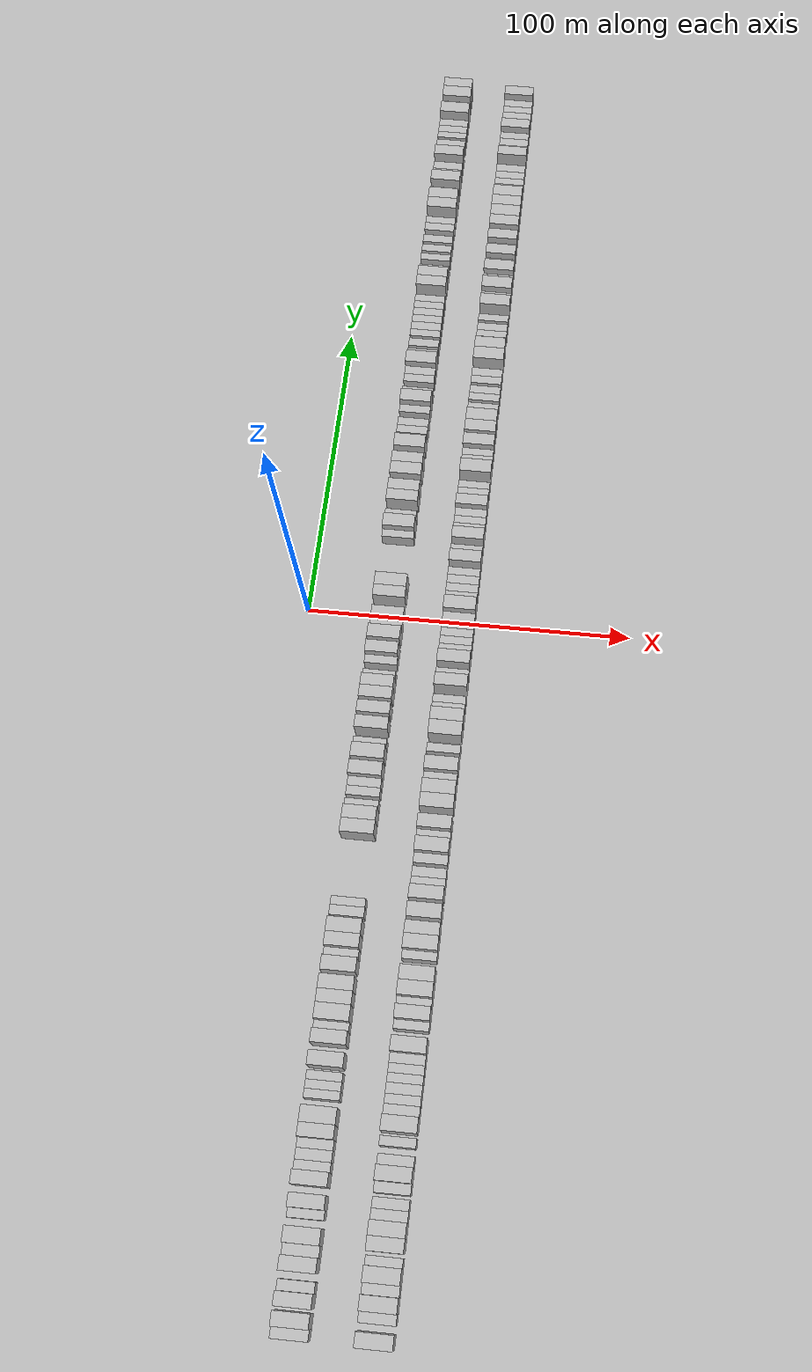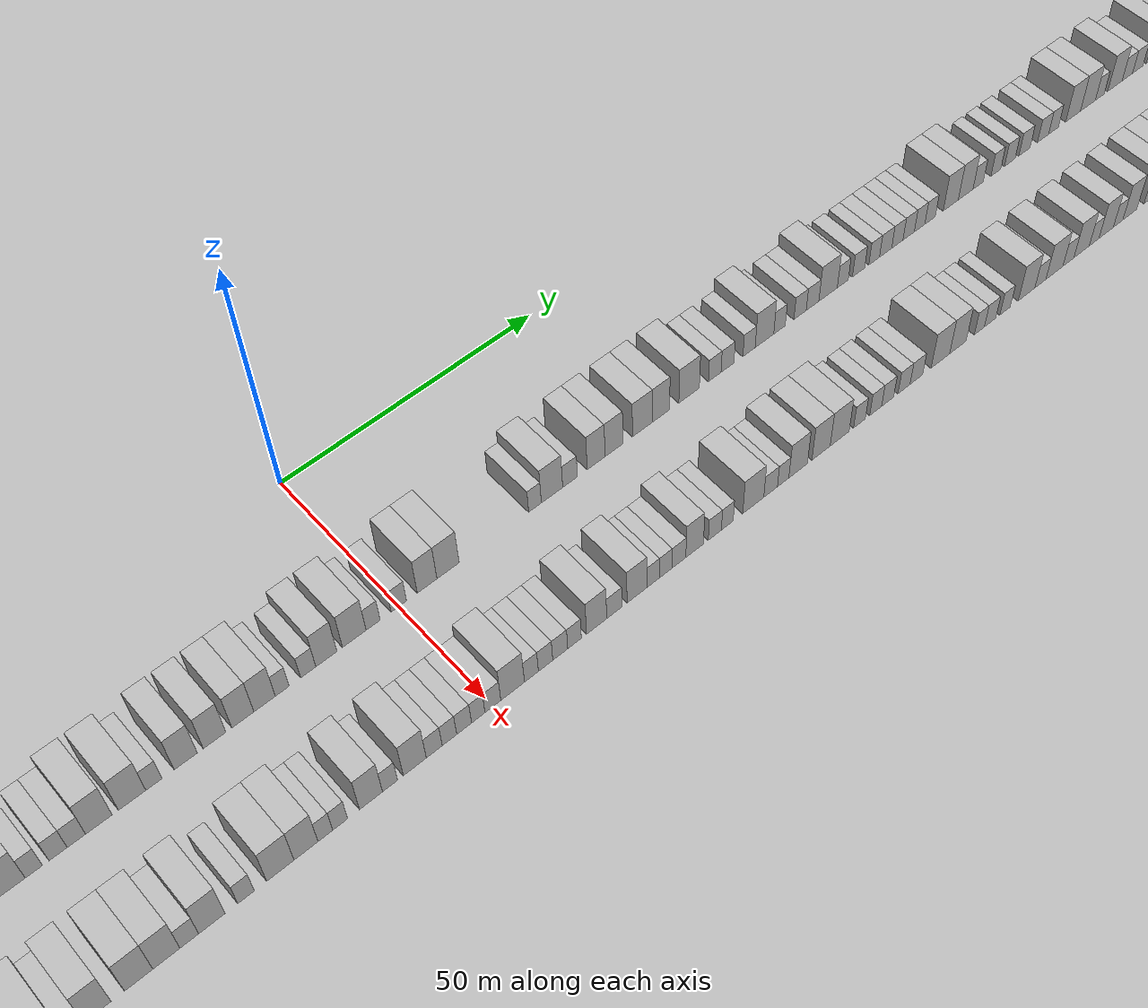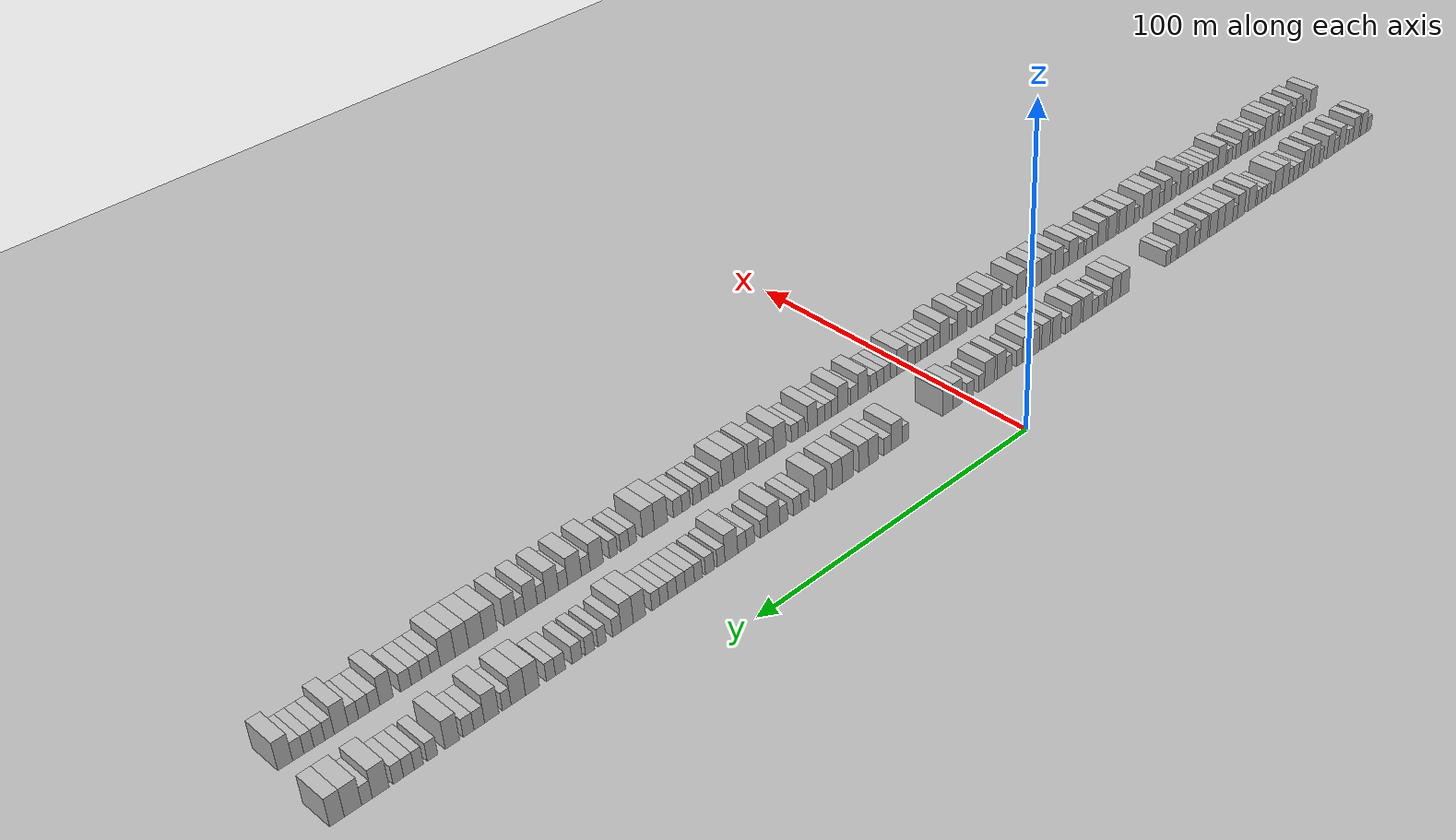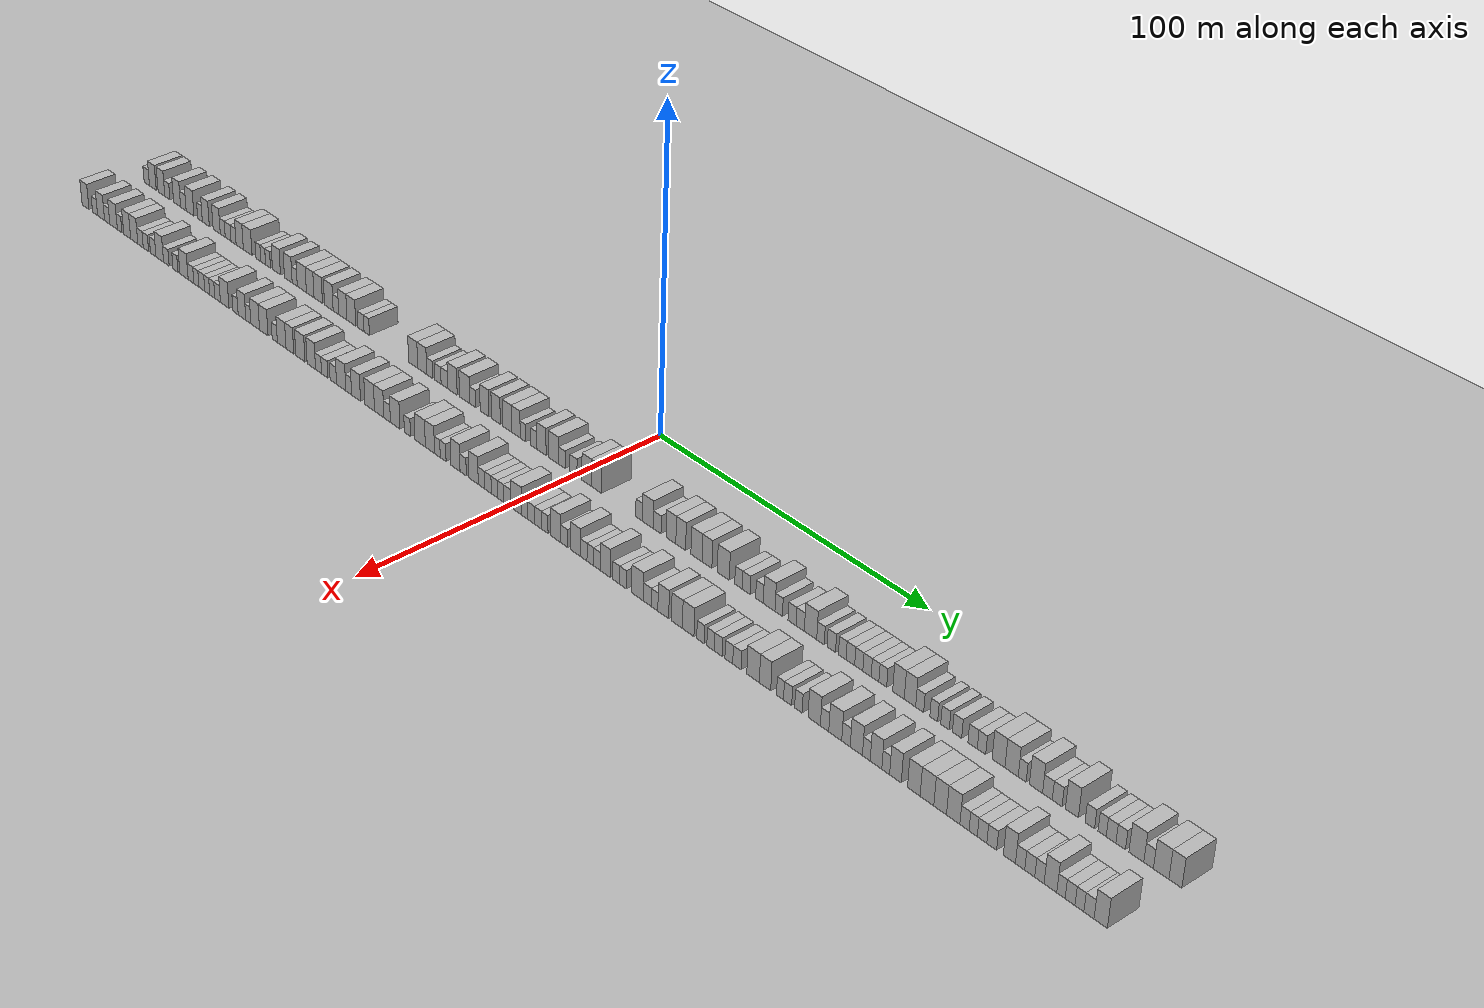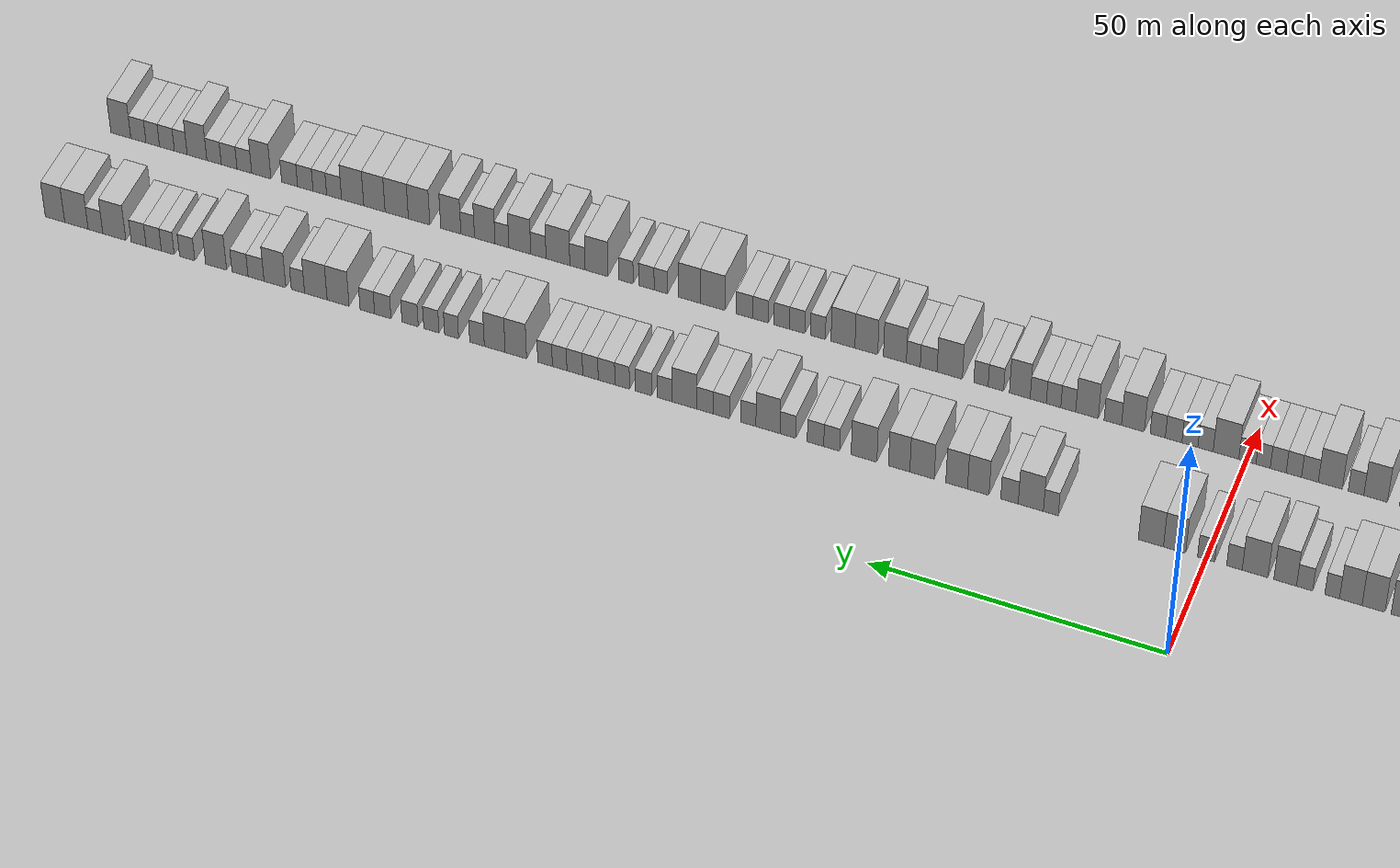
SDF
<?xml version="1.0" encoding="utf-8"?>

<sdf version="1.6">

   <world name="default">

      <gui fullscreen="0">

         <camera name="user_camera">

            <pose>-15 0 4.57585 0 0 0</pose>

            <view_controller>orbit</view_controller>

         </camera>

      </gui>

      <scene>

         <sky>

           <clouds>

             <speed>12</speed>

           </clouds>

         </sky>

         <ambient>0.4 0.4 0.4 1</ambient>

         <background>0.7 0.7 0.7 1</background>

         <shadows>1</shadows>

      </scene>

      <gravity>0 0 -9.8066</gravity>

      <magnetic_field>6e-06 2.3e-05 -4.2e-05</magnetic_field>

      <physics default="0" name="default_physics" type="ode">

         <ode>

            <solver>

               <type>quick</type>

               <iters>10</iters>

               <sor>1.0</sor>

               <use_dynamic_moi_rescaling>0</use_dynamic_moi_rescaling>

            </solver>

            <constraints>

               <cfm>0</cfm>

               <erp>0.2</erp>

               <contact_max_correcting_vel>100</contact_max_correcting_vel>

               <contact_surface_layer>0.001</contact_surface_layer>

            </constraints>

         </ode>

         <max_step_size>0.004</max_step_size>

         <real_time_factor>1</real_time_factor>

         <real_time_update_rate>250</real_time_update_rate>

      </physics>

      <light name="sun" type="directional">

         <cast_shadows>1</cast_shadows>

         <pose>0 0 10 0 0 0</pose>

         <diffuse>0.8 0.8 0.8 1</diffuse>

         <specular>0.2 0.2 0.2 1</specular>

         <attenuation>

            <range>1000</range>

            <constant>0.9</constant>

            <linear>0.01</linear>

            <quadratic>0.001</quadratic>

         </attenuation>

         <direction>-0.5 0.1 -0.9</direction>

      </light>

      <include>

         <name>ground_plane_1</name>

         <uri>model://HANNAS_ground_plane</uri>

         <pose>0 0 0  0 0 0</pose>

      </include>

      <include>

         <name>ground_plane_2</name>

         <uri>model://HANNAS_ground_plane</uri>

         <pose>100 0 0  0 0 0</pose>

      </include>

      <model name="building_1">

         <static>1</static>

         <pose frame="">25.0000 -202.5292 0 0.000000 0.000000 0.000000</pose>

         <link name="link">

            <pose frame="">0 0 3.00 0 0 0</pose>

            <collision name="collision">

               <geometry>

                  <box>

                     <size>10.0000 2.9416 6.0000</size>

                  </box>

               </geometry>

               <max_contacts>10</max_contacts>

               <surface>

                  <contact>

                     <ode/>

                  </contact>

                  <bounce/>

                  <friction>

                     <torsional>

                        <ode/>

                     </torsional>

                     <ode/>

                  </friction>

               </surface>

            </collision>

            <visual name="visual">

               <cast_shadows>0</cast_shadows>

               <geometry>

                  <box>

                     <size>10.0000 2.9416 6.0000</size>

                  </box>

               </geometry>

               <material>

                  <script>

                     <uri>model://HANNAS_wall/materials/scripts</uri>

                     <uri>model://HANNAS_wall/materials/textures</uri>

                     <name>vrc/HANNAS_wall</name>

                  </script>

               </material>

            </visual>

            <self_collide>0</self_collide>

            <enable_wind>0</enable_wind>

            <kinematic>0</kinematic>

         </link>

      </model>

      <model name="building_2">

         <static>1</static>

         <pose frame="">25.0000 -199.1781 0 0.000000 0.000000 0.000000</pose>

         <link name="link">

            <pose frame="">0 0 4.50 0 0 0</pose>

            <collision name="collision">

               <geometry>

                  <box>

                     <size>10.0000 3.7606 9.0000</size>

                  </box>

               </geometry>

               <max_contacts>10</max_contacts>

               <surface>

                  <contact>

                     <ode/>

                  </contact>

                  <bounce/>

                  <friction>

                     <torsional>

                        <ode/>

                     </torsional>

                     <ode/>

                  </friction>

               </surface>

            </collision>

            <visual name="visual">

               <cast_shadows>0</cast_shadows>

               <geometry>

                  <box>

                     <size>10.0000 3.7606 9.0000</size>

                  </box>

               </geometry>

               <material>

                  <script>

                     <uri>model://HANNAS_wall/materials/scripts</uri>

                     <uri>model://HANNAS_wall/materials/textures</uri>

                     <name>vrc/HANNAS_wall</name>

                  </script>

               </material>

            </visual>

            <self_collide>0</self_collide>

            <enable_wind>0</enable_wind>

            <kinematic>0</kinematic>

         </link>

      </model>

      <model name="building_3">

         <static>1</static>

         <pose frame="">25.0000 -194.4770 0 0.000000 0.000000 0.000000</pose>

         <link name="link">

            <pose frame="">0 0 4.50 0 0 0</pose>

            <collision name="collision">

               <geometry>

                  <box>

                     <size>10.0000 3.6417 9.0000</size>

                  </box>

               </geometry>

               <max_contacts>10</max_contacts>

               <surface>

                  <contact>

                     <ode/>

                  </contact>

                  <bounce/>

                  <friction>

                     <torsional>

                        <ode/>

                     </torsional>

                     <ode/>

                  </friction>

               </surface>

            </collision>

            <visual name="visual">

               <cast_shadows>0</cast_shadows>

               <geometry>

                  <box>

                     <size>10.0000 3.6417 9.0000</size>

                  </box>

               </geometry>

               <material>

                  <script>

                     <uri>model://HANNAS_wall/materials/scripts</uri>

                     <uri>model://HANNAS_wall/materials/textures</uri>

                     <name>vrc/HANNAS_wall</name>

                  </script>

               </material>

            </visual>

            <self_collide>0</self_collide>

            <enable_wind>0</enable_wind>

            <kinematic>0</kinematic>

         </link>

      </model>

      <model name="building_4">

         <static>1</static>

         <pose frame="">25.0000 -191.2516 0 0.000000 0.000000 0.000000</pose>

         <link name="link">

            <pose frame="">0 0 3.00 0 0 0</pose>

            <collision name="collision">

               <geometry>

                  <box>

                     <size>10.0000 2.8091 6.0000</size>

                  </box>

               </geometry>

               <max_contacts>10</max_contacts>

               <surface>

                  <contact>

                     <ode/>

                  </contact>

                  <bounce/>

                  <friction>

                     <torsional>

                        <ode/>

                     </torsional>

                     <ode/>

                  </friction>

               </surface>

            </collision>

            <visual name="visual">

               <cast_shadows>0</cast_shadows>

               <geometry>

                  <box>

                     <size>10.0000 2.8091 6.0000</size>

                  </box>

               </geometry>

               <material>

                  <script>

                     <uri>model://HANNAS_wall/materials/scripts</uri>

                     <uri>model://HANNAS_wall/materials/textures</uri>

                     <name>vrc/HANNAS_wall</name>

                  </script>

               </material>

            </visual>

            <self_collide>0</self_collide>

            <enable_wind>0</enable_wind>

            <kinematic>0</kinematic>

         </link>

      </model>

      <model name="building_5">

         <static>1</static>

         <pose frame="">25.0000 -185.9650 0 0.000000 0.000000 0.000000</pose>

         <link name="link">

            <pose frame="">0 0 4.50 0 0 0</pose>

            <collision name="collision">

               <geometry>

                  <box>

                     <size>10.0000 3.7642 9.0000</size>

                  </box>

               </geometry>

               <max_contacts>10</max_contacts>

               <surface>

                  <contact>

                     <ode/>

                  </contact>

                  <bounce/>

                  <friction>

                     <torsional>

                        <ode/>

                     </torsional>

                     <ode/>

                  </friction>

               </surface>

            </collision>

            <visual name="visual">

               <cast_shadows>0</cast_shadows>

               <geometry>

                  <box>

                     <size>10.0000 3.7642 9.0000</size>

                  </box>

               </geometry>

               <material>

                  <script>

                     <uri>model://HANNAS_wall/materials/scripts</uri>

                     <uri>model://HANNAS_wall/materials/textures</uri>

                     <name>vrc/HANNAS_wall</name>

                  </script>

               </material>

            </visual>

            <self_collide>0</self_collide>

            <enable_wind>0</enable_wind>

            <kinematic>0</kinematic>

         </link>

      </model>

      <model name="building_6">

         <static>1</static>

         <pose frame="">25.0000 -182.6085 0 0.000000 0.000000 0.000000</pose>

         <link name="link">

            <pose frame="">0 0 3.00 0 0 0</pose>

            <collision name="collision">

               <geometry>

                  <box>

                     <size>10.0000 2.9489 6.0000</size>

                  </box>

               </geometry>

               <max_contacts>10</max_contacts>

               <surface>

                  <contact>

                     <ode/>

                  </contact>

                  <bounce/>

                  <friction>

                     <torsional>

                        <ode/>

                     </torsional>

                     <ode/>

                  </friction>

               </surface>

            </collision>

            <visual name="visual">

               <cast_shadows>0</cast_shadows>

               <geometry>

                  <box>

                     <size>10.0000 2.9489 6.0000</size>

                  </box>

               </geometry>

               <material>

                  <script>

                     <uri>model://HANNAS_wall/materials/scripts</uri>

                     <uri>model://HANNAS_wall/materials/textures</uri>

                     <name>vrc/HANNAS_wall</name>

                  </script>

               </material>

            </visual>

            <self_collide>0</self_collide>

            <enable_wind>0</enable_wind>

            <kinematic>0</kinematic>

         </link>

      </model>

      <model name="building_7">

         <static>1</static>

         <pose frame="">25.0000 -179.0327 0 0.000000 0.000000 0.000000</pose>

         <link name="link">

            <pose frame="">0 0 4.50 0 0 0</pose>

            <collision name="collision">

               <geometry>

                  <box>

                     <size>10.0000 4.2026 9.0000</size>

                  </box>

               </geometry>

               <max_contacts>10</max_contacts>

               <surface>

                  <contact>

                     <ode/>

                  </contact>

                  <bounce/>

                  <friction>

                     <torsional>

                        <ode/>

                     </torsional>

                     <ode/>

                  </friction>

               </surface>

            </collision>

            <visual name="visual">

               <cast_shadows>0</cast_shadows>

               <geometry>

                  <box>

                     <size>10.0000 4.2026 9.0000</size>

                  </box>

               </geometry>

               <material>

                  <script>

                     <uri>model://HANNAS_wall/materials/scripts</uri>

                     <uri>model://HANNAS_wall/materials/textures</uri>

                     <name>vrc/HANNAS_wall</name>

                  </script>

               </material>

            </visual>

            <self_collide>0</self_collide>

            <enable_wind>0</enable_wind>

            <kinematic>0</kinematic>

         </link>

      </model>

      <model name="building_8">

         <static>1</static>

         <pose frame="">25.0000 -173.6945 0 0.000000 0.000000 0.000000</pose>

         <link name="link">

            <pose frame="">0 0 3.00 0 0 0</pose>

            <collision name="collision">

               <geometry>

                  <box>

                     <size>10.0000 2.4739 6.0000</size>

                  </box>

               </geometry>

               <max_contacts>10</max_contacts>

               <surface>

                  <contact>

                     <ode/>

                  </contact>

                  <bounce/>

                  <friction>

                     <torsional>

                        <ode/>

                     </torsional>

                     <ode/>

                  </friction>

               </surface>

            </collision>

            <visual name="visual">

               <cast_shadows>0</cast_shadows>

               <geometry>

                  <box>

                     <size>10.0000 2.4739 6.0000</size>

                  </box>

               </geometry>

               <material>

                  <script>

                     <uri>model://HANNAS_wall/materials/scripts</uri>

                     <uri>model://HANNAS_wall/materials/textures</uri>

                     <name>vrc/HANNAS_wall</name>

                  </script>

               </material>

            </visual>

            <self_collide>0</self_collide>

            <enable_wind>0</enable_wind>

            <kinematic>0</kinematic>

         </link>

      </model>

      <model name="building_9">

         <static>1</static>

         <pose frame="">25.0000 -170.6190 0 0.000000 0.000000 0.000000</pose>

         <link name="link">

            <pose frame="">0 0 4.50 0 0 0</pose>

            <collision name="collision">

               <geometry>

                  <box>

                     <size>10.0000 3.6771 9.0000</size>

                  </box>

               </geometry>

               <max_contacts>10</max_contacts>

               <surface>

                  <contact>

                     <ode/>

                  </contact>

                  <bounce/>

                  <friction>

                     <torsional>

                        <ode/>

                     </torsional>

                     <ode/>

                  </friction>

               </surface>

            </collision>

            <visual name="visual">

               <cast_shadows>0</cast_shadows>

               <geometry>

                  <box>

                     <size>10.0000 3.6771 9.0000</size>

                  </box>

               </geometry>

               <material>

                  <script>

                     <uri>model://HANNAS_wall/materials/scripts</uri>

                     <uri>model://HANNAS_wall/materials/textures</uri>

                     <name>vrc/HANNAS_wall</name>

                  </script>

               </material>

            </visual>

            <self_collide>0</self_collide>

            <enable_wind>0</enable_wind>

            <kinematic>0</kinematic>

         </link>

      </model>

      <model name="building_10">

         <static>1</static>

         <pose frame="">25.0000 -164.9156 0 0.000000 0.000000 0.000000</pose>

         <link name="link">

            <pose frame="">0 0 4.50 0 0 0</pose>

            <collision name="collision">

               <geometry>

                  <box>

                     <size>10.0000 3.7297 9.0000</size>

                  </box>

               </geometry>

               <max_contacts>10</max_contacts>

               <surface>

                  <contact>

                     <ode/>

                  </contact>

                  <bounce/>

                  <friction>

                     <torsional>

                        <ode/>

                     </torsional>

                     <ode/>

                  </friction>

               </surface>

            </collision>

            <visual name="visual">

               <cast_shadows>0</cast_shadows>

               <geometry>

                  <box>

                     <size>10.0000 3.7297 9.0000</size>

                  </box>

               </geometry>

               <material>

                  <script>

                     <uri>model://HANNAS_wall/materials/scripts</uri>

                     <uri>model://HANNAS_wall/materials/textures</uri>

                     <name>vrc/HANNAS_wall</name>

                  </script>

               </material>

            </visual>

            <self_collide>0</self_collide>

            <enable_wind>0</enable_wind>

            <kinematic>0</kinematic>

         </link>

      </model>

      <model name="building_11">

         <static>1</static>

         <pose frame="">25.0000 -161.7470 0 0.000000 0.000000 0.000000</pose>

         <link name="link">

            <pose frame="">0 0 3.00 0 0 0</pose>

            <collision name="collision">

               <geometry>

                  <box>

                     <size>10.0000 2.6075 6.0000</size>

                  </box>

               </geometry>

               <max_contacts>10</max_contacts>

               <surface>

                  <contact>

                     <ode/>

                  </contact>

                  <bounce/>

                  <friction>

                     <torsional>

                        <ode/>

                     </torsional>

                     <ode/>

                  </friction>

               </surface>

            </collision>

            <visual name="visual">

               <cast_shadows>0</cast_shadows>

               <geometry>

                  <box>

                     <size>10.0000 2.6075 6.0000</size>

                  </box>

               </geometry>

               <material>

                  <script>

                     <uri>model://HANNAS_wall/materials/scripts</uri>

                     <uri>model://HANNAS_wall/materials/textures</uri>

                     <name>vrc/HANNAS_wall</name>

                  </script>

               </material>

            </visual>

            <self_collide>0</self_collide>

            <enable_wind>0</enable_wind>

            <kinematic>0</kinematic>

         </link>

      </model>

      <model name="building_12">

         <static>1</static>

         <pose frame="">25.0000 -158.9450 0 0.000000 0.000000 0.000000</pose>

         <link name="link">

            <pose frame="">0 0 3.00 0 0 0</pose>

            <collision name="collision">

               <geometry>

                  <box>

                     <size>10.0000 2.9965 6.0000</size>

                  </box>

               </geometry>

               <max_contacts>10</max_contacts>

               <surface>

                  <contact>

                     <ode/>

                  </contact>

                  <bounce/>

                  <friction>

                     <torsional>

                        <ode/>

                     </torsional>

                     <ode/>

                  </friction>

               </surface>

            </collision>

            <visual name="visual">

               <cast_shadows>0</cast_shadows>

               <geometry>

                  <box>

                     <size>10.0000 2.9965 6.0000</size>

                  </box>

               </geometry>

               <material>

                  <script>

                     <uri>model://HANNAS_wall/materials/scripts</uri>

                     <uri>model://HANNAS_wall/materials/textures</uri>

                     <name>vrc/HANNAS_wall</name>

                  </script>

               </material>

            </visual>

            <self_collide>0</self_collide>

            <enable_wind>0</enable_wind>

            <kinematic>0</kinematic>

         </link>

      </model>

      <model name="building_13">

         <static>1</static>

         <pose frame="">25.0000 -156.1276 0 0.000000 0.000000 0.000000</pose>

         <link name="link">

            <pose frame="">0 0 3.00 0 0 0</pose>

            <collision name="collision">

               <geometry>

                  <box>

                     <size>10.0000 2.6382 6.0000</size>

                  </box>

               </geometry>

               <max_contacts>10</max_contacts>

               <surface>

                  <contact>

                     <ode/>

                  </contact>

                  <bounce/>

                  <friction>

                     <torsional>

                        <ode/>

                     </torsional>

                     <ode/>

                  </friction>

               </surface>

            </collision>

            <visual name="visual">

               <cast_shadows>0</cast_shadows>

               <geometry>

                  <box>

                     <size>10.0000 2.6382 6.0000</size>

                  </box>

               </geometry>

               <material>

                  <script>

                     <uri>model://HANNAS_wall/materials/scripts</uri>

                     <uri>model://HANNAS_wall/materials/textures</uri>

                     <name>vrc/HANNAS_wall</name>

                  </script>

               </material>

            </visual>

            <self_collide>0</self_collide>

            <enable_wind>0</enable_wind>

            <kinematic>0</kinematic>

         </link>

      </model>

      <model name="building_14">

         <static>1</static>

         <pose frame="">25.0000 -152.9464 0 0.000000 0.000000 0.000000</pose>

         <link name="link">

            <pose frame="">0 0 4.50 0 0 0</pose>

            <collision name="collision">

               <geometry>

                  <box>

                     <size>10.0000 3.7243 9.0000</size>

                  </box>

               </geometry>

               <max_contacts>10</max_contacts>

               <surface>

                  <contact>

                     <ode/>

                  </contact>

                  <bounce/>

                  <friction>

                     <torsional>

                        <ode/>

                     </torsional>

                     <ode/>

                  </friction>

               </surface>

            </collision>

            <visual name="visual">

               <cast_shadows>0</cast_shadows>

               <geometry>

                  <box>

                     <size>10.0000 3.7243 9.0000</size>

                  </box>

               </geometry>

               <material>

                  <script>

                     <uri>model://HANNAS_wall/materials/scripts</uri>

                     <uri>model://HANNAS_wall/materials/textures</uri>

                     <name>vrc/HANNAS_wall</name>

                  </script>

               </material>

            </visual>

            <self_collide>0</self_collide>

            <enable_wind>0</enable_wind>

            <kinematic>0</kinematic>

         </link>

      </model>

      <model name="building_15">

         <static>1</static>

         <pose frame="">25.0000 -148.8476 0 0.000000 0.000000 0.000000</pose>

         <link name="link">

            <pose frame="">0 0 4.50 0 0 0</pose>

            <collision name="collision">

               <geometry>

                  <box>

                     <size>10.0000 4.4733 9.0000</size>

                  </box>

               </geometry>

               <max_contacts>10</max_contacts>

               <surface>

                  <contact>

                     <ode/>

                  </contact>

                  <bounce/>

                  <friction>

                     <torsional>

                        <ode/>

                     </torsional>

                     <ode/>

                  </friction>

               </surface>

            </collision>

            <visual name="visual">

               <cast_shadows>0</cast_shadows>

               <geometry>

                  <box>

                     <size>10.0000 4.4733 9.0000</size>

                  </box>

               </geometry>

               <material>

                  <script>

                     <uri>model://HANNAS_wall/materials/scripts</uri>

                     <uri>model://HANNAS_wall/materials/textures</uri>

                     <name>vrc/HANNAS_wall</name>

                  </script>

               </material>

            </visual>

            <self_collide>0</self_collide>

            <enable_wind>0</enable_wind>

            <kinematic>0</kinematic>

         </link>

      </model>

      <model name="building_16">

         <static>1</static>

         <pose frame="">25.0000 -143.3843 0 0.000000 0.000000 0.000000</pose>

         <link name="link">

            <pose frame="">0 0 3.00 0 0 0</pose>

            <collision name="collision">

               <geometry>

                  <box>

                     <size>10.0000 2.4534 6.0000</size>

                  </box>

               </geometry>

               <max_contacts>10</max_contacts>

               <surface>

                  <contact>

                     <ode/>

                  </contact>

                  <bounce/>

                  <friction>

                     <torsional>

                        <ode/>

                     </torsional>

                     <ode/>

                  </friction>

               </surface>

            </collision>

            <visual name="visual">

               <cast_shadows>0</cast_shadows>

               <geometry>

                  <box>

                     <size>10.0000 2.4534 6.0000</size>

                  </box>

               </geometry>

               <material>

                  <script>

                     <uri>model://HANNAS_wall/materials/scripts</uri>

                     <uri>model://HANNAS_wall/materials/textures</uri>

                     <name>vrc/HANNAS_wall</name>

                  </script>

               </material>

            </visual>

            <self_collide>0</self_collide>

            <enable_wind>0</enable_wind>

            <kinematic>0</kinematic>

         </link>

      </model>

      <model name="building_17">

         <static>1</static>

         <pose frame="">25.0000 -140.9417 0 0.000000 0.000000 0.000000</pose>

         <link name="link">

            <pose frame="">0 0 3.00 0 0 0</pose>

            <collision name="collision">

               <geometry>

                  <box>

                     <size>10.0000 2.4318 6.0000</size>

                  </box>

               </geometry>

               <max_contacts>10</max_contacts>

               <surface>

                  <contact>

                     <ode/>

                  </contact>

                  <bounce/>

                  <friction>

                     <torsional>

                        <ode/>

                     </torsional>

                     <ode/>

                  </friction>

               </surface>

            </collision>

            <visual name="visual">

               <cast_shadows>0</cast_shadows>

               <geometry>

                  <box>

                     <size>10.0000 2.4318 6.0000</size>

                  </box>

               </geometry>

               <material>

                  <script>

                     <uri>model://HANNAS_wall/materials/scripts</uri>

                     <uri>model://HANNAS_wall/materials/textures</uri>

                     <name>vrc/HANNAS_wall</name>

                  </script>

               </material>

            </visual>

            <self_collide>0</self_collide>

            <enable_wind>0</enable_wind>

            <kinematic>0</kinematic>

         </link>

      </model>

      <model name="building_18">

         <static>1</static>

         <pose frame="">25.0000 -138.5001 0 0.000000 0.000000 0.000000</pose>

         <link name="link">

            <pose frame="">0 0 3.00 0 0 0</pose>

            <collision name="collision">

               <geometry>

                  <box>

                     <size>10.0000 2.4512 6.0000</size>

                  </box>

               </geometry>

               <max_contacts>10</max_contacts>

               <surface>

                  <contact>

                     <ode/>

                  </contact>

                  <bounce/>

                  <friction>

                     <torsional>

                        <ode/>

                     </torsional>

                     <ode/>

                  </friction>

               </surface>

            </collision>

            <visual name="visual">

               <cast_shadows>0</cast_shadows>

               <geometry>

                  <box>

                     <size>10.0000 2.4512 6.0000</size>

                  </box>

               </geometry>

               <material>

                  <script>

                     <uri>model://HANNAS_wall/materials/scripts</uri>

                     <uri>model://HANNAS_wall/materials/textures</uri>

                     <name>vrc/HANNAS_wall</name>

                  </script>

               </material>

            </visual>

            <self_collide>0</self_collide>

            <enable_wind>0</enable_wind>

            <kinematic>0</kinematic>

         </link>

      </model>

      <model name="building_19">

         <static>1</static>

         <pose frame="">25.0000 -134.2684 0 0.000000 0.000000 0.000000</pose>

         <link name="link">

            <pose frame="">0 0 4.50 0 0 0</pose>

            <collision name="collision">

               <geometry>

                  <box>

                     <size>10.0000 4.0122 9.0000</size>

                  </box>

               </geometry>

               <max_contacts>10</max_contacts>

               <surface>

                  <contact>

                     <ode/>

                  </contact>

                  <bounce/>

                  <friction>

                     <torsional>

                        <ode/>

                     </torsional>

                     <ode/>

                  </friction>

               </surface>

            </collision>

            <visual name="visual">

               <cast_shadows>0</cast_shadows>

               <geometry>

                  <box>

                     <size>10.0000 4.0122 9.0000</size>

                  </box>

               </geometry>

               <material>

                  <script>

                     <uri>model://HANNAS_wall/materials/scripts</uri>

                     <uri>model://HANNAS_wall/materials/textures</uri>

                     <name>vrc/HANNAS_wall</name>

                  </script>

               </material>

            </visual>

            <self_collide>0</self_collide>

            <enable_wind>0</enable_wind>

            <kinematic>0</kinematic>

         </link>

      </model>

      <model name="building_20">

         <static>1</static>

         <pose frame="">25.0000 -128.3569 0 0.000000 0.000000 0.000000</pose>

         <link name="link">

            <pose frame="">0 0 4.50 0 0 0</pose>

            <collision name="collision">

               <geometry>

                  <box>

                     <size>10.0000 3.8109 9.0000</size>

                  </box>

               </geometry>

               <max_contacts>10</max_contacts>

               <surface>

                  <contact>

                     <ode/>

                  </contact>

                  <bounce/>

                  <friction>

                     <torsional>

                        <ode/>

                     </torsional>

                     <ode/>

                  </friction>

               </surface>

            </collision>

            <visual name="visual">

               <cast_shadows>0</cast_shadows>

               <geometry>

                  <box>

                     <size>10.0000 3.8109 9.0000</size>

                  </box>

               </geometry>

               <material>

                  <script>

                     <uri>model://HANNAS_wall/materials/scripts</uri>

                     <uri>model://HANNAS_wall/materials/textures</uri>

                     <name>vrc/HANNAS_wall</name>

                  </script>

               </material>

            </visual>

            <self_collide>0</self_collide>

            <enable_wind>0</enable_wind>

            <kinematic>0</kinematic>

         </link>

      </model>

      <model name="building_21">

         <static>1</static>

         <pose frame="">25.0000 -125.1883 0 0.000000 0.000000 0.000000</pose>

         <link name="link">

            <pose frame="">0 0 3.00 0 0 0</pose>

            <collision name="collision">

               <geometry>

                  <box>

                     <size>10.0000 2.5262 6.0000</size>

                  </box>

               </geometry>

               <max_contacts>10</max_contacts>

               <surface>

                  <contact>

                     <ode/>

                  </contact>

                  <bounce/>

                  <friction>

                     <torsional>

                        <ode/>

                     </torsional>

                     <ode/>

                  </friction>

               </surface>

            </collision>

            <visual name="visual">

               <cast_shadows>0</cast_shadows>

               <geometry>

                  <box>

                     <size>10.0000 2.5262 6.0000</size>

                  </box>

               </geometry>

               <material>

                  <script>

                     <uri>model://HANNAS_wall/materials/scripts</uri>

                     <uri>model://HANNAS_wall/materials/textures</uri>

                     <name>vrc/HANNAS_wall</name>

                  </script>

               </material>

            </visual>

            <self_collide>0</self_collide>

            <enable_wind>0</enable_wind>

            <kinematic>0</kinematic>

         </link>

      </model>

      <model name="building_22">

         <static>1</static>

         <pose frame="">25.0000 -121.6837 0 0.000000 0.000000 0.000000</pose>

         <link name="link">

            <pose frame="">0 0 4.50 0 0 0</pose>

            <collision name="collision">

               <geometry>

                  <box>

                     <size>10.0000 4.4832 9.0000</size>

                  </box>

               </geometry>

               <max_contacts>10</max_contacts>

               <surface>

                  <contact>

                     <ode/>

                  </contact>

                  <bounce/>

                  <friction>

                     <torsional>

                        <ode/>

                     </torsional>

                     <ode/>

                  </friction>

               </surface>

            </collision>

            <visual name="visual">

               <cast_shadows>0</cast_shadows>

               <geometry>

                  <box>

                     <size>10.0000 4.4832 9.0000</size>

                  </box>

               </geometry>

               <material>

                  <script>

                     <uri>model://HANNAS_wall/materials/scripts</uri>

                     <uri>model://HANNAS_wall/materials/textures</uri>

                     <name>vrc/HANNAS_wall</name>

                  </script>

               </material>

            </visual>

            <self_collide>0</self_collide>

            <enable_wind>0</enable_wind>

            <kinematic>0</kinematic>

         </link>

      </model>

      <model name="building_23">

         <static>1</static>

         <pose frame="">25.0000 -117.5654 0 0.000000 0.000000 0.000000</pose>

         <link name="link">

            <pose frame="">0 0 4.50 0 0 0</pose>

            <collision name="collision">

               <geometry>

                  <box>

                     <size>10.0000 3.7533 9.0000</size>

                  </box>

               </geometry>

               <max_contacts>10</max_contacts>

               <surface>

                  <contact>

                     <ode/>

                  </contact>

                  <bounce/>

                  <friction>

                     <torsional>

                        <ode/>

                     </torsional>

                     <ode/>

                  </friction>

               </surface>

            </collision>

            <visual name="visual">

               <cast_shadows>0</cast_shadows>

               <geometry>

                  <box>

                     <size>10.0000 3.7533 9.0000</size>

                  </box>

               </geometry>

               <material>

                  <script>

                     <uri>model://HANNAS_wall/materials/scripts</uri>

                     <uri>model://HANNAS_wall/materials/textures</uri>

                     <name>vrc/HANNAS_wall</name>

                  </script>

               </material>

            </visual>

            <self_collide>0</self_collide>

            <enable_wind>0</enable_wind>

            <kinematic>0</kinematic>

         </link>

      </model>

      <model name="building_24">

         <static>1</static>

         <pose frame="">25.0000 -113.6408 0 0.000000 0.000000 0.000000</pose>

         <link name="link">

            <pose frame="">0 0 4.50 0 0 0</pose>

            <collision name="collision">

               <geometry>

                  <box>

                     <size>10.0000 4.0959 9.0000</size>

                  </box>

               </geometry>

               <max_contacts>10</max_contacts>

               <surface>

                  <contact>

                     <ode/>

                  </contact>

                  <bounce/>

                  <friction>

                     <torsional>

                        <ode/>

                     </torsional>

                     <ode/>

                  </friction>

               </surface>

            </collision>

            <visual name="visual">

               <cast_shadows>0</cast_shadows>

               <geometry>

                  <box>

                     <size>10.0000 4.0959 9.0000</size>

                  </box>

               </geometry>

               <material>

                  <script>

                     <uri>model://HANNAS_wall/materials/scripts</uri>

                     <uri>model://HANNAS_wall/materials/textures</uri>

                     <name>vrc/HANNAS_wall</name>

                  </script>

               </material>

            </visual>

            <self_collide>0</self_collide>

            <enable_wind>0</enable_wind>

            <kinematic>0</kinematic>

         </link>

      </model>

      <model name="building_25">

         <static>1</static>

         <pose frame="">25.0000 -108.5217 0 0.000000 0.000000 0.000000</pose>

         <link name="link">

            <pose frame="">0 0 4.50 0 0 0</pose>

            <collision name="collision">

               <geometry>

                  <box>

                     <size>10.0000 4.1422 9.0000</size>

                  </box>

               </geometry>

               <max_contacts>10</max_contacts>

               <surface>

                  <contact>

                     <ode/>

                  </contact>

                  <bounce/>

                  <friction>

                     <torsional>

                        <ode/>

                     </torsional>

                     <ode/>

                  </friction>

               </surface>

            </collision>

            <visual name="visual">

               <cast_shadows>0</cast_shadows>

               <geometry>

                  <box>

                     <size>10.0000 4.1422 9.0000</size>

                  </box>

               </geometry>

               <material>

                  <script>

                     <uri>model://HANNAS_wall/materials/scripts</uri>

                     <uri>model://HANNAS_wall/materials/textures</uri>

                     <name>vrc/HANNAS_wall</name>

                  </script>

               </material>

            </visual>

            <self_collide>0</self_collide>

            <enable_wind>0</enable_wind>

            <kinematic>0</kinematic>

         </link>

      </model>

      <model name="building_26">

         <static>1</static>

         <pose frame="">25.0000 -105.1016 0 0.000000 0.000000 0.000000</pose>

         <link name="link">

            <pose frame="">0 0 3.00 0 0 0</pose>

            <collision name="collision">

               <geometry>

                  <box>

                     <size>10.0000 2.6979 6.0000</size>

                  </box>

               </geometry>

               <max_contacts>10</max_contacts>

               <surface>

                  <contact>

                     <ode/>

                  </contact>

                  <bounce/>

                  <friction>

                     <torsional>

                        <ode/>

                     </torsional>

                     <ode/>

                  </friction>

               </surface>

            </collision>

            <visual name="visual">

               <cast_shadows>0</cast_shadows>

               <geometry>

                  <box>

                     <size>10.0000 2.6979 6.0000</size>

                  </box>

               </geometry>

               <material>

                  <script>

                     <uri>model://HANNAS_wall/materials/scripts</uri>

                     <uri>model://HANNAS_wall/materials/textures</uri>

                     <name>vrc/HANNAS_wall</name>

                  </script>

               </material>

            </visual>

            <self_collide>0</self_collide>

            <enable_wind>0</enable_wind>

            <kinematic>0</kinematic>

         </link>

      </model>

      <model name="building_27">

         <static>1</static>

         <pose frame="">25.0000 -101.7893 0 0.000000 0.000000 0.000000</pose>

         <link name="link">

            <pose frame="">0 0 4.50 0 0 0</pose>

            <collision name="collision">

               <geometry>

                  <box>

                     <size>10.0000 3.9268 9.0000</size>

                  </box>

               </geometry>

               <max_contacts>10</max_contacts>

               <surface>

                  <contact>

                     <ode/>

                  </contact>

                  <bounce/>

                  <friction>

                     <torsional>

                        <ode/>

                     </torsional>

                     <ode/>

                  </friction>

               </surface>

            </collision>

            <visual name="visual">

               <cast_shadows>0</cast_shadows>

               <geometry>

                  <box>

                     <size>10.0000 3.9268 9.0000</size>

                  </box>

               </geometry>

               <material>

                  <script>

                     <uri>model://HANNAS_wall/materials/scripts</uri>

                     <uri>model://HANNAS_wall/materials/textures</uri>

                     <name>vrc/HANNAS_wall</name>

                  </script>

               </material>

            </visual>

            <self_collide>0</self_collide>

            <enable_wind>0</enable_wind>

            <kinematic>0</kinematic>

         </link>

      </model>

      <model name="building_28">

         <static>1</static>

         <pose frame="">25.0000 -97.7386 0 0.000000 0.000000 0.000000</pose>

         <link name="link">

            <pose frame="">0 0 4.50 0 0 0</pose>

            <collision name="collision">

               <geometry>

                  <box>

                     <size>10.0000 4.1745 9.0000</size>

                  </box>

               </geometry>

               <max_contacts>10</max_contacts>

               <surface>

                  <contact>

                     <ode/>

                  </contact>

                  <bounce/>

                  <friction>

                     <torsional>

                        <ode/>

                     </torsional>

                     <ode/>

                  </friction>

               </surface>

            </collision>

            <visual name="visual">

               <cast_shadows>0</cast_shadows>

               <geometry>

                  <box>

                     <size>10.0000 4.1745 9.0000</size>

                  </box>

               </geometry>

               <material>

                  <script>

                     <uri>model://HANNAS_wall/materials/scripts</uri>

                     <uri>model://HANNAS_wall/materials/textures</uri>

                     <name>vrc/HANNAS_wall</name>

                  </script>

               </material>

            </visual>

            <self_collide>0</self_collide>

            <enable_wind>0</enable_wind>

            <kinematic>0</kinematic>

         </link>

      </model>

      <model name="building_29">

         <static>1</static>

         <pose frame="">25.0000 -93.1996 0 0.000000 0.000000 0.000000</pose>

         <link name="link">

            <pose frame="">0 0 3.00 0 0 0</pose>

            <collision name="collision">

               <geometry>

                  <box>

                     <size>10.0000 2.9034 6.0000</size>

                  </box>

               </geometry>

               <max_contacts>10</max_contacts>

               <surface>

                  <contact>

                     <ode/>

                  </contact>

                  <bounce/>

                  <friction>

                     <torsional>

                        <ode/>

                     </torsional>

                     <ode/>

                  </friction>

               </surface>

            </collision>

            <visual name="visual">

               <cast_shadows>0</cast_shadows>

               <geometry>

                  <box>

                     <size>10.0000 2.9034 6.0000</size>

                  </box>

               </geometry>

               <material>

                  <script>

                     <uri>model://HANNAS_wall/materials/scripts</uri>

                     <uri>model://HANNAS_wall/materials/textures</uri>

                     <name>vrc/HANNAS_wall</name>

                  </script>

               </material>

            </visual>

            <self_collide>0</self_collide>

            <enable_wind>0</enable_wind>

            <kinematic>0</kinematic>

         </link>

      </model>

      <model name="building_30">

         <static>1</static>

         <pose frame="">25.0000 -90.4950 0 0.000000 0.000000 0.000000</pose>

         <link name="link">

            <pose frame="">0 0 3.00 0 0 0</pose>

            <collision name="collision">

               <geometry>

                  <box>

                     <size>10.0000 2.5059 6.0000</size>

                  </box>

               </geometry>

               <max_contacts>10</max_contacts>

               <surface>

                  <contact>

                     <ode/>

                  </contact>

                  <bounce/>

                  <friction>

                     <torsional>

                        <ode/>

                     </torsional>

                     <ode/>

                  </friction>

               </surface>

            </collision>

            <visual name="visual">

               <cast_shadows>0</cast_shadows>

               <geometry>

                  <box>

                     <size>10.0000 2.5059 6.0000</size>

                  </box>

               </geometry>

               <material>

                  <script>

                     <uri>model://HANNAS_wall/materials/scripts</uri>

                     <uri>model://HANNAS_wall/materials/textures</uri>

                     <name>vrc/HANNAS_wall</name>

                  </script>

               </material>

            </visual>

            <self_collide>0</self_collide>

            <enable_wind>0</enable_wind>

            <kinematic>0</kinematic>

         </link>

      </model>

      <model name="building_31">

         <static>1</static>

         <pose frame="">25.0000 -69.0618 0 0.000000 0.000000 0.000000</pose>

         <link name="link">

            <pose frame="">0 0 4.50 0 0 0</pose>

            <collision name="collision">

               <geometry>

                  <box>

                     <size>10.0000 4.1202 9.0000</size>

                  </box>

               </geometry>

               <max_contacts>10</max_contacts>

               <surface>

                  <contact>

                     <ode/>

                  </contact>

                  <bounce/>

                  <friction>

                     <torsional>

                        <ode/>

                     </torsional>

                     <ode/>

                  </friction>

               </surface>

            </collision>

            <visual name="visual">

               <cast_shadows>0</cast_shadows>

               <geometry>

                  <box>

                     <size>10.0000 4.1202 9.0000</size>

                  </box>

               </geometry>

               <material>

                  <script>

                     <uri>model://HANNAS_wall/materials/scripts</uri>

                     <uri>model://HANNAS_wall/materials/textures</uri>

                     <name>vrc/HANNAS_wall</name>

                  </script>

               </material>

            </visual>

            <self_collide>0</self_collide>

            <enable_wind>0</enable_wind>

            <kinematic>0</kinematic>

         </link>

      </model>

      <model name="building_32">

         <static>1</static>

         <pose frame="">25.0000 -64.9716 0 0.000000 0.000000 0.000000</pose>

         <link name="link">

            <pose frame="">0 0 4.50 0 0 0</pose>

            <collision name="collision">

               <geometry>

                  <box>

                     <size>10.0000 4.0602 9.0000</size>

                  </box>

               </geometry>

               <max_contacts>10</max_contacts>

               <surface>

                  <contact>

                     <ode/>

                  </contact>

                  <bounce/>

                  <friction>

                     <torsional>

                        <ode/>

                     </torsional>

                     <ode/>

                  </friction>

               </surface>

            </collision>

            <visual name="visual">

               <cast_shadows>0</cast_shadows>

               <geometry>

                  <box>

                     <size>10.0000 4.0602 9.0000</size>

                  </box>

               </geometry>

               <material>

                  <script>

                     <uri>model://HANNAS_wall/materials/scripts</uri>

                     <uri>model://HANNAS_wall/materials/textures</uri>

                     <name>vrc/HANNAS_wall</name>

                  </script>

               </material>

            </visual>

            <self_collide>0</self_collide>

            <enable_wind>0</enable_wind>

            <kinematic>0</kinematic>

         </link>

      </model>

      <model name="building_33">

         <static>1</static>

         <pose frame="">25.0000 -61.6120 0 0.000000 0.000000 0.000000</pose>

         <link name="link">

            <pose frame="">0 0 3.00 0 0 0</pose>

            <collision name="collision">

               <geometry>

                  <box>

                     <size>10.0000 2.6590 6.0000</size>

                  </box>

               </geometry>

               <max_contacts>10</max_contacts>

               <surface>

                  <contact>

                     <ode/>

                  </contact>

                  <bounce/>

                  <friction>

                     <torsional>

                        <ode/>

                     </torsional>

                     <ode/>

                  </friction>

               </surface>

            </collision>

            <visual name="visual">

               <cast_shadows>0</cast_shadows>

               <geometry>

                  <box>

                     <size>10.0000 2.6590 6.0000</size>

                  </box>

               </geometry>

               <material>

                  <script>

                     <uri>model://HANNAS_wall/materials/scripts</uri>

                     <uri>model://HANNAS_wall/materials/textures</uri>

                     <name>vrc/HANNAS_wall</name>

                  </script>

               </material>

            </visual>

            <self_collide>0</self_collide>

            <enable_wind>0</enable_wind>

            <kinematic>0</kinematic>

         </link>

      </model>

      <model name="building_34">

         <static>1</static>

         <pose frame="">25.0000 -57.8716 0 0.000000 0.000000 0.000000</pose>

         <link name="link">

            <pose frame="">0 0 3.00 0 0 0</pose>

            <collision name="collision">

               <geometry>

                  <box>

                     <size>10.0000 2.8217 6.0000</size>

                  </box>

               </geometry>

               <max_contacts>10</max_contacts>

               <surface>

                  <contact>

                     <ode/>

                  </contact>

                  <bounce/>

                  <friction>

                     <torsional>

                        <ode/>

                     </torsional>

                     <ode/>

                  </friction>

               </surface>

            </collision>

            <visual name="visual">

               <cast_shadows>0</cast_shadows>

               <geometry>

                  <box>

                     <size>10.0000 2.8217 6.0000</size>

                  </box>

               </geometry>

               <material>

                  <script>

                     <uri>model://HANNAS_wall/materials/scripts</uri>

                     <uri>model://HANNAS_wall/materials/textures</uri>

                     <name>vrc/HANNAS_wall</name>

                  </script>

               </material>

            </visual>

            <self_collide>0</self_collide>

            <enable_wind>0</enable_wind>

            <kinematic>0</kinematic>

         </link>

      </model>

      <model name="building_35">

         <static>1</static>

         <pose frame="">25.0000 -55.0200 0 0.000000 0.000000 0.000000</pose>

         <link name="link">

            <pose frame="">0 0 3.00 0 0 0</pose>

            <collision name="collision">

               <geometry>

                  <box>

                     <size>10.0000 2.8814 6.0000</size>

                  </box>

               </geometry>

               <max_contacts>10</max_contacts>

               <surface>

                  <contact>

                     <ode/>

                  </contact>

                  <bounce/>

                  <friction>

                     <torsional>

                        <ode/>

                     </torsional>

                     <ode/>

                  </friction>

               </surface>

            </collision>

            <visual name="visual">

               <cast_shadows>0</cast_shadows>

               <geometry>

                  <box>

                     <size>10.0000 2.8814 6.0000</size>

                  </box>

               </geometry>

               <material>

                  <script>

                     <uri>model://HANNAS_wall/materials/scripts</uri>

                     <uri>model://HANNAS_wall/materials/textures</uri>

                     <name>vrc/HANNAS_wall</name>

                  </script>

               </material>

            </visual>

            <self_collide>0</self_collide>

            <enable_wind>0</enable_wind>

            <kinematic>0</kinematic>

         </link>

      </model>

      <model name="building_36">

         <static>1</static>

         <pose frame="">25.0000 -51.4653 0 0.000000 0.000000 0.000000</pose>

         <link name="link">

            <pose frame="">0 0 4.50 0 0 0</pose>

            <collision name="collision">

               <geometry>

                  <box>

                     <size>10.0000 4.2280 9.0000</size>

                  </box>

               </geometry>

               <max_contacts>10</max_contacts>

               <surface>

                  <contact>

                     <ode/>

                  </contact>

                  <bounce/>

                  <friction>

                     <torsional>

                        <ode/>

                     </torsional>

                     <ode/>

                  </friction>

               </surface>

            </collision>

            <visual name="visual">

               <cast_shadows>0</cast_shadows>

               <geometry>

                  <box>

                     <size>10.0000 4.2280 9.0000</size>

                  </box>

               </geometry>

               <material>

                  <script>

                     <uri>model://HANNAS_wall/materials/scripts</uri>

                     <uri>model://HANNAS_wall/materials/textures</uri>

                     <name>vrc/HANNAS_wall</name>

                  </script>

               </material>

            </visual>

            <self_collide>0</self_collide>

            <enable_wind>0</enable_wind>

            <kinematic>0</kinematic>

         </link>

      </model>

      <model name="building_37">

         <static>1</static>

         <pose frame="">25.0000 -46.1372 0 0.000000 0.000000 0.000000</pose>

         <link name="link">

            <pose frame="">0 0 4.50 0 0 0</pose>

            <collision name="collision">

               <geometry>

                  <box>

                     <size>10.0000 4.4281 9.0000</size>

                  </box>

               </geometry>

               <max_contacts>10</max_contacts>

               <surface>

                  <contact>

                     <ode/>

                  </contact>

                  <bounce/>

                  <friction>

                     <torsional>

                        <ode/>

                     </torsional>

                     <ode/>

                  </friction>

               </surface>

            </collision>

            <visual name="visual">

               <cast_shadows>0</cast_shadows>

               <geometry>

                  <box>

                     <size>10.0000 4.4281 9.0000</size>

                  </box>

               </geometry>

               <material>

                  <script>

                     <uri>model://HANNAS_wall/materials/scripts</uri>

                     <uri>model://HANNAS_wall/materials/textures</uri>

                     <name>vrc/HANNAS_wall</name>

                  </script>

               </material>

            </visual>

            <self_collide>0</self_collide>

            <enable_wind>0</enable_wind>

            <kinematic>0</kinematic>

         </link>

      </model>

      <model name="building_38">

         <static>1</static>

         <pose frame="">25.0000 -42.6079 0 0.000000 0.000000 0.000000</pose>

         <link name="link">

            <pose frame="">0 0 3.00 0 0 0</pose>

            <collision name="collision">

               <geometry>

                  <box>

                     <size>10.0000 2.6304 6.0000</size>

                  </box>

               </geometry>

               <max_contacts>10</max_contacts>

               <surface>

                  <contact>

                     <ode/>

                  </contact>

                  <bounce/>

                  <friction>

                     <torsional>

                        <ode/>

                     </torsional>

                     <ode/>

                  </friction>

               </surface>

            </collision>

            <visual name="visual">

               <cast_shadows>0</cast_shadows>

               <geometry>

                  <box>

                     <size>10.0000 2.6304 6.0000</size>

                  </box>

               </geometry>

               <material>

                  <script>

                     <uri>model://HANNAS_wall/materials/scripts</uri>

                     <uri>model://HANNAS_wall/materials/textures</uri>

                     <name>vrc/HANNAS_wall</name>

                  </script>

               </material>

            </visual>

            <self_collide>0</self_collide>

            <enable_wind>0</enable_wind>

            <kinematic>0</kinematic>

         </link>

      </model>

      <model name="building_39">

         <static>1</static>

         <pose frame="">25.0000 -37.3734 0 0.000000 0.000000 0.000000</pose>

         <link name="link">

            <pose frame="">0 0 4.50 0 0 0</pose>

            <collision name="collision">

               <geometry>

                  <box>

                     <size>10.0000 3.8386 9.0000</size>

                  </box>

               </geometry>

               <max_contacts>10</max_contacts>

               <surface>

                  <contact>

                     <ode/>

                  </contact>

                  <bounce/>

                  <friction>

                     <torsional>

                        <ode/>

                     </torsional>

                     <ode/>

                  </friction>

               </surface>

            </collision>

            <visual name="visual">

               <cast_shadows>0</cast_shadows>

               <geometry>

                  <box>

                     <size>10.0000 3.8386 9.0000</size>

                  </box>

               </geometry>

               <material>

                  <script>

                     <uri>model://HANNAS_wall/materials/scripts</uri>

                     <uri>model://HANNAS_wall/materials/textures</uri>

                     <name>vrc/HANNAS_wall</name>

                  </script>

               </material>

            </visual>

            <self_collide>0</self_collide>

            <enable_wind>0</enable_wind>

            <kinematic>0</kinematic>

         </link>

      </model>

      <model name="building_40">

         <static>1</static>

         <pose frame="">25.0000 -32.5507 0 0.000000 0.000000 0.000000</pose>

         <link name="link">

            <pose frame="">0 0 4.50 0 0 0</pose>

            <collision name="collision">

               <geometry>

                  <box>

                     <size>10.0000 3.8069 9.0000</size>

                  </box>

               </geometry>

               <max_contacts>10</max_contacts>

               <surface>

                  <contact>

                     <ode/>

                  </contact>

                  <bounce/>

                  <friction>

                     <torsional>

                        <ode/>

                     </torsional>

                     <ode/>

                  </friction>

               </surface>

            </collision>

            <visual name="visual">

               <cast_shadows>0</cast_shadows>

               <geometry>

                  <box>

                     <size>10.0000 3.8069 9.0000</size>

                  </box>

               </geometry>

               <material>

                  <script>

                     <uri>model://HANNAS_wall/materials/scripts</uri>

                     <uri>model://HANNAS_wall/materials/textures</uri>

                     <name>vrc/HANNAS_wall</name>

                  </script>

               </material>

            </visual>

            <self_collide>0</self_collide>

            <enable_wind>0</enable_wind>

            <kinematic>0</kinematic>

         </link>

      </model>

      <model name="building_41">

         <static>1</static>

         <pose frame="">25.0000 -27.7635 0 0.000000 0.000000 0.000000</pose>

         <link name="link">

            <pose frame="">0 0 4.50 0 0 0</pose>

            <collision name="collision">

               <geometry>

                  <box>

                     <size>10.0000 3.7676 9.0000</size>

                  </box>

               </geometry>

               <max_contacts>10</max_contacts>

               <surface>

                  <contact>

                     <ode/>

                  </contact>

                  <bounce/>

                  <friction>

                     <torsional>

                        <ode/>

                     </torsional>

                     <ode/>

                  </friction>

               </surface>

            </collision>

            <visual name="visual">

               <cast_shadows>0</cast_shadows>

               <geometry>

                  <box>

                     <size>10.0000 3.7676 9.0000</size>

                  </box>

               </geometry>

               <material>

                  <script>

                     <uri>model://HANNAS_wall/materials/scripts</uri>

                     <uri>model://HANNAS_wall/materials/textures</uri>

                     <name>vrc/HANNAS_wall</name>

                  </script>

               </material>

            </visual>

            <self_collide>0</self_collide>

            <enable_wind>0</enable_wind>

            <kinematic>0</kinematic>

         </link>

      </model>

      <model name="building_42">

         <static>1</static>

         <pose frame="">25.0000 -24.0283 0 0.000000 0.000000 0.000000</pose>

         <link name="link">

            <pose frame="">0 0 4.50 0 0 0</pose>

            <collision name="collision">

               <geometry>

                  <box>

                     <size>10.0000 3.7028 9.0000</size>

                  </box>

               </geometry>

               <max_contacts>10</max_contacts>

               <surface>

                  <contact>

                     <ode/>

                  </contact>

                  <bounce/>

                  <friction>

                     <torsional>

                        <ode/>

                     </torsional>

                     <ode/>

                  </friction>

               </surface>

            </collision>

            <visual name="visual">

               <cast_shadows>0</cast_shadows>

               <geometry>

                  <box>

                     <size>10.0000 3.7028 9.0000</size>

                  </box>

               </geometry>

               <material>

                  <script>

                     <uri>model://HANNAS_wall/materials/scripts</uri>

                     <uri>model://HANNAS_wall/materials/textures</uri>

                     <name>vrc/HANNAS_wall</name>

                  </script>

               </material>

            </visual>

            <self_collide>0</self_collide>

            <enable_wind>0</enable_wind>

            <kinematic>0</kinematic>

         </link>

      </model>

      <model name="building_43">

         <static>1</static>

         <pose frame="">25.0000 -20.9685 0 0.000000 0.000000 0.000000</pose>

         <link name="link">

            <pose frame="">0 0 3.00 0 0 0</pose>

            <collision name="collision">

               <geometry>

                  <box>

                     <size>10.0000 2.4167 6.0000</size>

                  </box>

               </geometry>

               <max_contacts>10</max_contacts>

               <surface>

                  <contact>

                     <ode/>

                  </contact>

                  <bounce/>

                  <friction>

                     <torsional>

                        <ode/>

                     </torsional>

                     <ode/>

                  </friction>

               </surface>

            </collision>

            <visual name="visual">

               <cast_shadows>0</cast_shadows>

               <geometry>

                  <box>

                     <size>10.0000 2.4167 6.0000</size>

                  </box>

               </geometry>

               <material>

                  <script>

                     <uri>model://HANNAS_wall/materials/scripts</uri>

                     <uri>model://HANNAS_wall/materials/textures</uri>

                     <name>vrc/HANNAS_wall</name>

                  </script>

               </material>

            </visual>

            <self_collide>0</self_collide>

            <enable_wind>0</enable_wind>

            <kinematic>0</kinematic>

         </link>

      </model>

      <model name="building_44">

         <static>1</static>

         <pose frame="">25.0000 -16.4239 0 0.000000 0.000000 0.000000</pose>

         <link name="link">

            <pose frame="">0 0 3.00 0 0 0</pose>

            <collision name="collision">

               <geometry>

                  <box>

                     <size>10.0000 2.6726 6.0000</size>

                  </box>

               </geometry>

               <max_contacts>10</max_contacts>

               <surface>

                  <contact>

                     <ode/>

                  </contact>

                  <bounce/>

                  <friction>

                     <torsional>

                        <ode/>

                     </torsional>

                     <ode/>

                  </friction>

               </surface>

            </collision>

            <visual name="visual">

               <cast_shadows>0</cast_shadows>

               <geometry>

                  <box>

                     <size>10.0000 2.6726 6.0000</size>

                  </box>

               </geometry>

               <material>

                  <script>

                     <uri>model://HANNAS_wall/materials/scripts</uri>

                     <uri>model://HANNAS_wall/materials/textures</uri>

                     <name>vrc/HANNAS_wall</name>

                  </script>

               </material>

            </visual>

            <self_collide>0</self_collide>

            <enable_wind>0</enable_wind>

            <kinematic>0</kinematic>

         </link>

      </model>

      <model name="building_45">

         <static>1</static>

         <pose frame="">25.0000 -13.2102 0 0.000000 0.000000 0.000000</pose>

         <link name="link">

            <pose frame="">0 0 4.50 0 0 0</pose>

            <collision name="collision">

               <geometry>

                  <box>

                     <size>10.0000 3.7548 9.0000</size>

                  </box>

               </geometry>

               <max_contacts>10</max_contacts>

               <surface>

                  <contact>

                     <ode/>

                  </contact>

                  <bounce/>

                  <friction>

                     <torsional>

                        <ode/>

                     </torsional>

                     <ode/>

                  </friction>

               </surface>

            </collision>

            <visual name="visual">

               <cast_shadows>0</cast_shadows>

               <geometry>

                  <box>

                     <size>10.0000 3.7548 9.0000</size>

                  </box>

               </geometry>

               <material>

                  <script>

                     <uri>model://HANNAS_wall/materials/scripts</uri>

                     <uri>model://HANNAS_wall/materials/textures</uri>

                     <name>vrc/HANNAS_wall</name>

                  </script>

               </material>

            </visual>

            <self_collide>0</self_collide>

            <enable_wind>0</enable_wind>

            <kinematic>0</kinematic>

         </link>

      </model>

      <model name="building_46">

         <static>1</static>

         <pose frame="">25.0000 -8.2017 0 0.000000 0.000000 0.000000</pose>

         <link name="link">

            <pose frame="">0 0 4.50 0 0 0</pose>

            <collision name="collision">

               <geometry>

                  <box>

                     <size>10.0000 4.2623 9.0000</size>

                  </box>

               </geometry>

               <max_contacts>10</max_contacts>

               <surface>

                  <contact>

                     <ode/>

                  </contact>

                  <bounce/>

                  <friction>

                     <torsional>

                        <ode/>

                     </torsional>

                     <ode/>

                  </friction>

               </surface>

            </collision>

            <visual name="visual">

               <cast_shadows>0</cast_shadows>

               <geometry>

                  <box>

                     <size>10.0000 4.2623 9.0000</size>

                  </box>

               </geometry>

               <material>

                  <script>

                     <uri>model://HANNAS_wall/materials/scripts</uri>

                     <uri>model://HANNAS_wall/materials/textures</uri>

                     <name>vrc/HANNAS_wall</name>

                  </script>

               </material>

            </visual>

            <self_collide>0</self_collide>

            <enable_wind>0</enable_wind>

            <kinematic>0</kinematic>

         </link>

      </model>

      <model name="building_47">

         <static>1</static>

         <pose frame="">25.0000 -4.7786 0 0.000000 0.000000 0.000000</pose>

         <link name="link">

            <pose frame="">0 0 3.00 0 0 0</pose>

            <collision name="collision">

               <geometry>

                  <box>

                     <size>10.0000 2.5840 6.0000</size>

                  </box>

               </geometry>

               <max_contacts>10</max_contacts>

               <surface>

                  <contact>

                     <ode/>

                  </contact>

                  <bounce/>

                  <friction>

                     <torsional>

                        <ode/>

                     </torsional>

                     <ode/>

                  </friction>

               </surface>

            </collision>

            <visual name="visual">

               <cast_shadows>0</cast_shadows>

               <geometry>

                  <box>

                     <size>10.0000 2.5840 6.0000</size>

                  </box>

               </geometry>

               <material>

                  <script>

                     <uri>model://HANNAS_wall/materials/scripts</uri>

                     <uri>model://HANNAS_wall/materials/textures</uri>

                     <name>vrc/HANNAS_wall</name>

                  </script>

               </material>

            </visual>

            <self_collide>0</self_collide>

            <enable_wind>0</enable_wind>

            <kinematic>0</kinematic>

         </link>

      </model>

      <model name="building_48">

         <static>1</static>

         <pose frame="">25.0000 -0.0581 0 0.000000 0.000000 0.000000</pose>

         <link name="link">

            <pose frame="">0 0 3.00 0 0 0</pose>

            <collision name="collision">

               <geometry>

                  <box>

                     <size>10.0000 2.8570 6.0000</size>

                  </box>

               </geometry>

               <max_contacts>10</max_contacts>

               <surface>

                  <contact>

                     <ode/>

                  </contact>

                  <bounce/>

                  <friction>

                     <torsional>

                        <ode/>

                     </torsional>

                     <ode/>

                  </friction>

               </surface>

            </collision>

            <visual name="visual">

               <cast_shadows>0</cast_shadows>

               <geometry>

                  <box>

                     <size>10.0000 2.8570 6.0000</size>

                  </box>

               </geometry>

               <material>

                  <script>

                     <uri>model://HANNAS_wall/materials/scripts</uri>

                     <uri>model://HANNAS_wall/materials/textures</uri>

                     <name>vrc/HANNAS_wall</name>

                  </script>

               </material>

            </visual>

            <self_collide>0</self_collide>

            <enable_wind>0</enable_wind>

            <kinematic>0</kinematic>

         </link>

      </model>

      <model name="building_49">

         <static>1</static>

         <pose frame="">25.0000 5.2194 0 0.000000 0.000000 0.000000</pose>

         <link name="link">

            <pose frame="">0 0 4.50 0 0 0</pose>

            <collision name="collision">

               <geometry>

                  <box>

                     <size>10.0000 3.6980 9.0000</size>

                  </box>

               </geometry>

               <max_contacts>10</max_contacts>

               <surface>

                  <contact>

                     <ode/>

                  </contact>

                  <bounce/>

                  <friction>

                     <torsional>

                        <ode/>

                     </torsional>

                     <ode/>

                  </friction>

               </surface>

            </collision>

            <visual name="visual">

               <cast_shadows>0</cast_shadows>

               <geometry>

                  <box>

                     <size>10.0000 3.6980 9.0000</size>

                  </box>

               </geometry>

               <material>

                  <script>

                     <uri>model://HANNAS_wall/materials/scripts</uri>

                     <uri>model://HANNAS_wall/materials/textures</uri>

                     <name>vrc/HANNAS_wall</name>

                  </script>

               </material>

            </visual>

            <self_collide>0</self_collide>

            <enable_wind>0</enable_wind>

            <kinematic>0</kinematic>

         </link>

      </model>

      <model name="building_50">

         <static>1</static>

         <pose frame="">25.0000 9.1772 0 0.000000 0.000000 0.000000</pose>

         <link name="link">

            <pose frame="">0 0 4.50 0 0 0</pose>

            <collision name="collision">

               <geometry>

                  <box>

                     <size>10.0000 4.2176 9.0000</size>

                  </box>

               </geometry>

               <max_contacts>10</max_contacts>

               <surface>

                  <contact>

                     <ode/>

                  </contact>

                  <bounce/>

                  <friction>

                     <torsional>

                        <ode/>

                     </torsional>

                     <ode/>

                  </friction>

               </surface>

            </collision>

            <visual name="visual">

               <cast_shadows>0</cast_shadows>

               <geometry>

                  <box>

                     <size>10.0000 4.2176 9.0000</size>

                  </box>

               </geometry>

               <material>

                  <script>

                     <uri>model://HANNAS_wall/materials/scripts</uri>

                     <uri>model://HANNAS_wall/materials/textures</uri>

                     <name>vrc/HANNAS_wall</name>

                  </script>

               </material>

            </visual>

            <self_collide>0</self_collide>

            <enable_wind>0</enable_wind>

            <kinematic>0</kinematic>

         </link>

      </model>

      <model name="building_51">

         <static>1</static>

         <pose frame="">25.0000 26.0716 0 0.000000 0.000000 0.000000</pose>

         <link name="link">

            <pose frame="">0 0 3.00 0 0 0</pose>

            <collision name="collision">

               <geometry>

                  <box>

                     <size>10.0000 2.5238 6.0000</size>

                  </box>

               </geometry>

               <max_contacts>10</max_contacts>

               <surface>

                  <contact>

                     <ode/>

                  </contact>

                  <bounce/>

                  <friction>

                     <torsional>

                        <ode/>

                     </torsional>

                     <ode/>

                  </friction>

               </surface>

            </collision>

            <visual name="visual">

               <cast_shadows>0</cast_shadows>

               <geometry>

                  <box>

                     <size>10.0000 2.5238 6.0000</size>

                  </box>

               </geometry>

               <material>

                  <script>

                     <uri>model://HANNAS_wall/materials/scripts</uri>

                     <uri>model://HANNAS_wall/materials/textures</uri>

                     <name>vrc/HANNAS_wall</name>

                  </script>

               </material>

            </visual>

            <self_collide>0</self_collide>

            <enable_wind>0</enable_wind>

            <kinematic>0</kinematic>

         </link>

      </model>

      <model name="building_52">

         <static>1</static>

         <pose frame="">25.0000 29.4768 0 0.000000 0.000000 0.000000</pose>

         <link name="link">

            <pose frame="">0 0 4.50 0 0 0</pose>

            <collision name="collision">

               <geometry>

                  <box>

                     <size>10.0000 4.2866 9.0000</size>

                  </box>

               </geometry>

               <max_contacts>10</max_contacts>

               <surface>

                  <contact>

                     <ode/>

                  </contact>

                  <bounce/>

                  <friction>

                     <torsional>

                        <ode/>

                     </torsional>

                     <ode/>

                  </friction>

               </surface>

            </collision>

            <visual name="visual">

               <cast_shadows>0</cast_shadows>

               <geometry>

                  <box>

                     <size>10.0000 4.2866 9.0000</size>

                  </box>

               </geometry>

               <material>

                  <script>

                     <uri>model://HANNAS_wall/materials/scripts</uri>

                     <uri>model://HANNAS_wall/materials/textures</uri>

                     <name>vrc/HANNAS_wall</name>

                  </script>

               </material>

            </visual>

            <self_collide>0</self_collide>

            <enable_wind>0</enable_wind>

            <kinematic>0</kinematic>

         </link>

      </model>

      <model name="building_53">

         <static>1</static>

         <pose frame="">25.0000 33.1085 0 0.000000 0.000000 0.000000</pose>

         <link name="link">

            <pose frame="">0 0 3.00 0 0 0</pose>

            <collision name="collision">

               <geometry>

                  <box>

                     <size>10.0000 2.9769 6.0000</size>

                  </box>

               </geometry>

               <max_contacts>10</max_contacts>

               <surface>

                  <contact>

                     <ode/>

                  </contact>

                  <bounce/>

                  <friction>

                     <torsional>

                        <ode/>

                     </torsional>

                     <ode/>

                  </friction>

               </surface>

            </collision>

            <visual name="visual">

               <cast_shadows>0</cast_shadows>

               <geometry>

                  <box>

                     <size>10.0000 2.9769 6.0000</size>

                  </box>

               </geometry>

               <material>

                  <script>

                     <uri>model://HANNAS_wall/materials/scripts</uri>

                     <uri>model://HANNAS_wall/materials/textures</uri>

                     <name>vrc/HANNAS_wall</name>

                  </script>

               </material>

            </visual>

            <self_collide>0</self_collide>

            <enable_wind>0</enable_wind>

            <kinematic>0</kinematic>

         </link>

      </model>

      <model name="building_54">

         <static>1</static>

         <pose frame="">25.0000 38.4390 0 0.000000 0.000000 0.000000</pose>

         <link name="link">

            <pose frame="">0 0 4.50 0 0 0</pose>

            <collision name="collision">

               <geometry>

                  <box>

                     <size>10.0000 3.6842 9.0000</size>

                  </box>

               </geometry>

               <max_contacts>10</max_contacts>

               <surface>

                  <contact>

                     <ode/>

                  </contact>

                  <bounce/>

                  <friction>

                     <torsional>

                        <ode/>

                     </torsional>

                     <ode/>

                  </friction>

               </surface>

            </collision>

            <visual name="visual">

               <cast_shadows>0</cast_shadows>

               <geometry>

                  <box>

                     <size>10.0000 3.6842 9.0000</size>

                  </box>

               </geometry>

               <material>

                  <script>

                     <uri>model://HANNAS_wall/materials/scripts</uri>

                     <uri>model://HANNAS_wall/materials/textures</uri>

                     <name>vrc/HANNAS_wall</name>

                  </script>

               </material>

            </visual>

            <self_collide>0</self_collide>

            <enable_wind>0</enable_wind>

            <kinematic>0</kinematic>

         </link>

      </model>

      <model name="building_55">

         <static>1</static>

         <pose frame="">25.0000 42.1352 0 0.000000 0.000000 0.000000</pose>

         <link name="link">

            <pose frame="">0 0 4.50 0 0 0</pose>

            <collision name="collision">

               <geometry>

                  <box>

                     <size>10.0000 3.7081 9.0000</size>

                  </box>

               </geometry>

               <max_contacts>10</max_contacts>

               <surface>

                  <contact>

                     <ode/>

                  </contact>

                  <bounce/>

                  <friction>

                     <torsional>

                        <ode/>

                     </torsional>

                     <ode/>

                  </friction>

               </surface>

            </collision>

            <visual name="visual">

               <cast_shadows>0</cast_shadows>

               <geometry>

                  <box>

                     <size>10.0000 3.7081 9.0000</size>

                  </box>

               </geometry>

               <material>

                  <script>

                     <uri>model://HANNAS_wall/materials/scripts</uri>

                     <uri>model://HANNAS_wall/materials/textures</uri>

                     <name>vrc/HANNAS_wall</name>

                  </script>

               </material>

            </visual>

            <self_collide>0</self_collide>

            <enable_wind>0</enable_wind>

            <kinematic>0</kinematic>

         </link>

      </model>

      <model name="building_56">

         <static>1</static>

         <pose frame="">25.0000 48.0854 0 0.000000 0.000000 0.000000</pose>

         <link name="link">

            <pose frame="">0 0 4.50 0 0 0</pose>

            <collision name="collision">

               <geometry>

                  <box>

                     <size>10.0000 4.1924 9.0000</size>

                  </box>

               </geometry>

               <max_contacts>10</max_contacts>

               <surface>

                  <contact>

                     <ode/>

                  </contact>

                  <bounce/>

                  <friction>

                     <torsional>

                        <ode/>

                     </torsional>

                     <ode/>

                  </friction>

               </surface>

            </collision>

            <visual name="visual">

               <cast_shadows>0</cast_shadows>

               <geometry>

                  <box>

                     <size>10.0000 4.1924 9.0000</size>

                  </box>

               </geometry>

               <material>

                  <script>

                     <uri>model://HANNAS_wall/materials/scripts</uri>

                     <uri>model://HANNAS_wall/materials/textures</uri>

                     <name>vrc/HANNAS_wall</name>

                  </script>

               </material>

            </visual>

            <self_collide>0</self_collide>

            <enable_wind>0</enable_wind>

            <kinematic>0</kinematic>

         </link>

      </model>

      <model name="building_57">

         <static>1</static>

         <pose frame="">25.0000 52.0209 0 0.000000 0.000000 0.000000</pose>

         <link name="link">

            <pose frame="">0 0 4.50 0 0 0</pose>

            <collision name="collision">

               <geometry>

                  <box>

                     <size>10.0000 3.6785 9.0000</size>

                  </box>

               </geometry>

               <max_contacts>10</max_contacts>

               <surface>

                  <contact>

                     <ode/>

                  </contact>

                  <bounce/>

                  <friction>

                     <torsional>

                        <ode/>

                     </torsional>

                     <ode/>

                  </friction>

               </surface>

            </collision>

            <visual name="visual">

               <cast_shadows>0</cast_shadows>

               <geometry>

                  <box>

                     <size>10.0000 3.6785 9.0000</size>

                  </box>

               </geometry>

               <material>

                  <script>

                     <uri>model://HANNAS_wall/materials/scripts</uri>

                     <uri>model://HANNAS_wall/materials/textures</uri>

                     <name>vrc/HANNAS_wall</name>

                  </script>

               </material>

            </visual>

            <self_collide>0</self_collide>

            <enable_wind>0</enable_wind>

            <kinematic>0</kinematic>

         </link>

      </model>

      <model name="building_58">

         <static>1</static>

         <pose frame="">25.0000 58.0877 0 0.000000 0.000000 0.000000</pose>

         <link name="link">

            <pose frame="">0 0 4.50 0 0 0</pose>

            <collision name="collision">

               <geometry>

                  <box>

                     <size>10.0000 4.4550 9.0000</size>

                  </box>

               </geometry>

               <max_contacts>10</max_contacts>

               <surface>

                  <contact>

                     <ode/>

                  </contact>

                  <bounce/>

                  <friction>

                     <torsional>

                        <ode/>

                     </torsional>

                     <ode/>

                  </friction>

               </surface>

            </collision>

            <visual name="visual">

               <cast_shadows>0</cast_shadows>

               <geometry>

                  <box>

                     <size>10.0000 4.4550 9.0000</size>

                  </box>

               </geometry>

               <material>

                  <script>

                     <uri>model://HANNAS_wall/materials/scripts</uri>

                     <uri>model://HANNAS_wall/materials/textures</uri>

                     <name>vrc/HANNAS_wall</name>

                  </script>

               </material>

            </visual>

            <self_collide>0</self_collide>

            <enable_wind>0</enable_wind>

            <kinematic>0</kinematic>

         </link>

      </model>

      <model name="building_59">

         <static>1</static>

         <pose frame="">25.0000 63.6962 0 0.000000 0.000000 0.000000</pose>

         <link name="link">

            <pose frame="">0 0 3.00 0 0 0</pose>

            <collision name="collision">

               <geometry>

                  <box>

                     <size>10.0000 2.7621 6.0000</size>

                  </box>

               </geometry>

               <max_contacts>10</max_contacts>

               <surface>

                  <contact>

                     <ode/>

                  </contact>

                  <bounce/>

                  <friction>

                     <torsional>

                        <ode/>

                     </torsional>

                     <ode/>

                  </friction>

               </surface>

            </collision>

            <visual name="visual">

               <cast_shadows>0</cast_shadows>

               <geometry>

                  <box>

                     <size>10.0000 2.7621 6.0000</size>

                  </box>

               </geometry>

               <material>

                  <script>

                     <uri>model://HANNAS_wall/materials/scripts</uri>

                     <uri>model://HANNAS_wall/materials/textures</uri>

                     <name>vrc/HANNAS_wall</name>

                  </script>

               </material>

            </visual>

            <self_collide>0</self_collide>

            <enable_wind>0</enable_wind>

            <kinematic>0</kinematic>

         </link>

      </model>

      <model name="building_60">

         <static>1</static>

         <pose frame="">25.0000 66.5094 0 0.000000 0.000000 0.000000</pose>

         <link name="link">

            <pose frame="">0 0 3.00 0 0 0</pose>

            <collision name="collision">

               <geometry>

                  <box>

                     <size>10.0000 2.8641 6.0000</size>

                  </box>

               </geometry>

               <max_contacts>10</max_contacts>

               <surface>

                  <contact>

                     <ode/>

                  </contact>

                  <bounce/>

                  <friction>

                     <torsional>

                        <ode/>

                     </torsional>

                     <ode/>

                  </friction>

               </surface>

            </collision>

            <visual name="visual">

               <cast_shadows>0</cast_shadows>

               <geometry>

                  <box>

                     <size>10.0000 2.8641 6.0000</size>

                  </box>

               </geometry>

               <material>

                  <script>

                     <uri>model://HANNAS_wall/materials/scripts</uri>

                     <uri>model://HANNAS_wall/materials/textures</uri>

                     <name>vrc/HANNAS_wall</name>

                  </script>

               </material>

            </visual>

            <self_collide>0</self_collide>

            <enable_wind>0</enable_wind>

            <kinematic>0</kinematic>

         </link>

      </model>

      <model name="building_61">

         <static>1</static>

         <pose frame="">25.0000 71.3160 0 0.000000 0.000000 0.000000</pose>

         <link name="link">

            <pose frame="">0 0 3.00 0 0 0</pose>

            <collision name="collision">

               <geometry>

                  <box>

                     <size>10.0000 2.7490 6.0000</size>

                  </box>

               </geometry>

               <max_contacts>10</max_contacts>

               <surface>

                  <contact>

                     <ode/>

                  </contact>

                  <bounce/>

                  <friction>

                     <torsional>

                        <ode/>

                     </torsional>

                     <ode/>

                  </friction>

               </surface>

            </collision>

            <visual name="visual">

               <cast_shadows>0</cast_shadows>

               <geometry>

                  <box>

                     <size>10.0000 2.7490 6.0000</size>

                  </box>

               </geometry>

               <material>

                  <script>

                     <uri>model://HANNAS_wall/materials/scripts</uri>

                     <uri>model://HANNAS_wall/materials/textures</uri>

                     <name>vrc/HANNAS_wall</name>

                  </script>

               </material>

            </visual>

            <self_collide>0</self_collide>

            <enable_wind>0</enable_wind>

            <kinematic>0</kinematic>

         </link>

      </model>

      <model name="building_62">

         <static>1</static>

         <pose frame="">25.0000 74.7978 0 0.000000 0.000000 0.000000</pose>

         <link name="link">

            <pose frame="">0 0 4.50 0 0 0</pose>

            <collision name="collision">

               <geometry>

                  <box>

                     <size>10.0000 4.2146 9.0000</size>

                  </box>

               </geometry>

               <max_contacts>10</max_contacts>

               <surface>

                  <contact>

                     <ode/>

                  </contact>

                  <bounce/>

                  <friction>

                     <torsional>

                        <ode/>

                     </torsional>

                     <ode/>

                  </friction>

               </surface>

            </collision>

            <visual name="visual">

               <cast_shadows>0</cast_shadows>

               <geometry>

                  <box>

                     <size>10.0000 4.2146 9.0000</size>

                  </box>

               </geometry>

               <material>

                  <script>

                     <uri>model://HANNAS_wall/materials/scripts</uri>

                     <uri>model://HANNAS_wall/materials/textures</uri>

                     <name>vrc/HANNAS_wall</name>

                  </script>

               </material>

            </visual>

            <self_collide>0</self_collide>

            <enable_wind>0</enable_wind>

            <kinematic>0</kinematic>

         </link>

      </model>

      <model name="building_63">

         <static>1</static>

         <pose frame="">25.0000 78.2187 0 0.000000 0.000000 0.000000</pose>

         <link name="link">

            <pose frame="">0 0 3.00 0 0 0</pose>

            <collision name="collision">

               <geometry>

                  <box>

                     <size>10.0000 2.6273 6.0000</size>

                  </box>

               </geometry>

               <max_contacts>10</max_contacts>

               <surface>

                  <contact>

                     <ode/>

                  </contact>

                  <bounce/>

                  <friction>

                     <torsional>

                        <ode/>

                     </torsional>

                     <ode/>

                  </friction>

               </surface>

            </collision>

            <visual name="visual">

               <cast_shadows>0</cast_shadows>

               <geometry>

                  <box>

                     <size>10.0000 2.6273 6.0000</size>

                  </box>

               </geometry>

               <material>

                  <script>

                     <uri>model://HANNAS_wall/materials/scripts</uri>

                     <uri>model://HANNAS_wall/materials/textures</uri>

                     <name>vrc/HANNAS_wall</name>

                  </script>

               </material>

            </visual>

            <self_collide>0</self_collide>

            <enable_wind>0</enable_wind>

            <kinematic>0</kinematic>

         </link>

      </model>

      <model name="building_64">

         <static>1</static>

         <pose frame="">25.0000 82.9542 0 0.000000 0.000000 0.000000</pose>

         <link name="link">

            <pose frame="">0 0 3.00 0 0 0</pose>

            <collision name="collision">

               <geometry>

                  <box>

                     <size>10.0000 2.8437 6.0000</size>

                  </box>

               </geometry>

               <max_contacts>10</max_contacts>

               <surface>

                  <contact>

                     <ode/>

                  </contact>

                  <bounce/>

                  <friction>

                     <torsional>

                        <ode/>

                     </torsional>

                     <ode/>

                  </friction>

               </surface>

            </collision>

            <visual name="visual">

               <cast_shadows>0</cast_shadows>

               <geometry>

                  <box>

                     <size>10.0000 2.8437 6.0000</size>

                  </box>

               </geometry>

               <material>

                  <script>

                     <uri>model://HANNAS_wall/materials/scripts</uri>

                     <uri>model://HANNAS_wall/materials/textures</uri>

                     <name>vrc/HANNAS_wall</name>

                  </script>

               </material>

            </visual>

            <self_collide>0</self_collide>

            <enable_wind>0</enable_wind>

            <kinematic>0</kinematic>

         </link>

      </model>

      <model name="building_65">

         <static>1</static>

         <pose frame="">25.0000 85.8451 0 0.000000 0.000000 0.000000</pose>

         <link name="link">

            <pose frame="">0 0 3.00 0 0 0</pose>

            <collision name="collision">

               <geometry>

                  <box>

                     <size>10.0000 2.9380 6.0000</size>

                  </box>

               </geometry>

               <max_contacts>10</max_contacts>

               <surface>

                  <contact>

                     <ode/>

                  </contact>

                  <bounce/>

                  <friction>

                     <torsional>

                        <ode/>

                     </torsional>

                     <ode/>

                  </friction>

               </surface>

            </collision>

            <visual name="visual">

               <cast_shadows>0</cast_shadows>

               <geometry>

                  <box>

                     <size>10.0000 2.9380 6.0000</size>

                  </box>

               </geometry>

               <material>

                  <script>

                     <uri>model://HANNAS_wall/materials/scripts</uri>

                     <uri>model://HANNAS_wall/materials/textures</uri>

                     <name>vrc/HANNAS_wall</name>

                  </script>

               </material>

            </visual>

            <self_collide>0</self_collide>

            <enable_wind>0</enable_wind>

            <kinematic>0</kinematic>

         </link>

      </model>

      <model name="building_66">

         <static>1</static>

         <pose frame="">25.0000 89.4803 0 0.000000 0.000000 0.000000</pose>

         <link name="link">

            <pose frame="">0 0 4.50 0 0 0</pose>

            <collision name="collision">

               <geometry>

                  <box>

                     <size>10.0000 4.3324 9.0000</size>

                  </box>

               </geometry>

               <max_contacts>10</max_contacts>

               <surface>

                  <contact>

                     <ode/>

                  </contact>

                  <bounce/>

                  <friction>

                     <torsional>

                        <ode/>

                     </torsional>

                     <ode/>

                  </friction>

               </surface>

            </collision>

            <visual name="visual">

               <cast_shadows>0</cast_shadows>

               <geometry>

                  <box>

                     <size>10.0000 4.3324 9.0000</size>

                  </box>

               </geometry>

               <material>

                  <script>

                     <uri>model://HANNAS_wall/materials/scripts</uri>

                     <uri>model://HANNAS_wall/materials/textures</uri>

                     <name>vrc/HANNAS_wall</name>

                  </script>

               </material>

            </visual>

            <self_collide>0</self_collide>

            <enable_wind>0</enable_wind>

            <kinematic>0</kinematic>

         </link>

      </model>

      <model name="building_67">

         <static>1</static>

         <pose frame="">25.0000 92.9520 0 0.000000 0.000000 0.000000</pose>

         <link name="link">

            <pose frame="">0 0 3.00 0 0 0</pose>

            <collision name="collision">

               <geometry>

                  <box>

                     <size>10.0000 2.6109 6.0000</size>

                  </box>

               </geometry>

               <max_contacts>10</max_contacts>

               <surface>

                  <contact>

                     <ode/>

                  </contact>

                  <bounce/>

                  <friction>

                     <torsional>

                        <ode/>

                     </torsional>

                     <ode/>

                  </friction>

               </surface>

            </collision>

            <visual name="visual">

               <cast_shadows>0</cast_shadows>

               <geometry>

                  <box>

                     <size>10.0000 2.6109 6.0000</size>

                  </box>

               </geometry>

               <material>

                  <script>

                     <uri>model://HANNAS_wall/materials/scripts</uri>

                     <uri>model://HANNAS_wall/materials/textures</uri>

                     <name>vrc/HANNAS_wall</name>

                  </script>

               </material>

            </visual>

            <self_collide>0</self_collide>

            <enable_wind>0</enable_wind>

            <kinematic>0</kinematic>

         </link>

      </model>

      <model name="building_68">

         <static>1</static>

         <pose frame="">25.0000 96.7186 0 0.000000 0.000000 0.000000</pose>

         <link name="link">

            <pose frame="">0 0 3.00 0 0 0</pose>

            <collision name="collision">

               <geometry>

                  <box>

                     <size>10.0000 2.9223 6.0000</size>

                  </box>

               </geometry>

               <max_contacts>10</max_contacts>

               <surface>

                  <contact>

                     <ode/>

                  </contact>

                  <bounce/>

                  <friction>

                     <torsional>

                        <ode/>

                     </torsional>

                     <ode/>

                  </friction>

               </surface>

            </collision>

            <visual name="visual">

               <cast_shadows>0</cast_shadows>

               <geometry>

                  <box>

                     <size>10.0000 2.9223 6.0000</size>

                  </box>

               </geometry>

               <material>

                  <script>

                     <uri>model://HANNAS_wall/materials/scripts</uri>

                     <uri>model://HANNAS_wall/materials/textures</uri>

                     <name>vrc/HANNAS_wall</name>

                  </script>

               </material>

            </visual>

            <self_collide>0</self_collide>

            <enable_wind>0</enable_wind>

            <kinematic>0</kinematic>

         </link>

      </model>

      <model name="building_69">

         <static>1</static>

         <pose frame="">25.0000 100.4769 0 0.000000 0.000000 0.000000</pose>

         <link name="link">

            <pose frame="">0 0 3.00 0 0 0</pose>

            <collision name="collision">

               <geometry>

                  <box>

                     <size>10.0000 2.5943 6.0000</size>

                  </box>

               </geometry>

               <max_contacts>10</max_contacts>

               <surface>

                  <contact>

                     <ode/>

                  </contact>

                  <bounce/>

                  <friction>

                     <torsional>

                        <ode/>

                     </torsional>

                     <ode/>

                  </friction>

               </surface>

            </collision>

            <visual name="visual">

               <cast_shadows>0</cast_shadows>

               <geometry>

                  <box>

                     <size>10.0000 2.5943 6.0000</size>

                  </box>

               </geometry>

               <material>

                  <script>

                     <uri>model://HANNAS_wall/materials/scripts</uri>

                     <uri>model://HANNAS_wall/materials/textures</uri>

                     <name>vrc/HANNAS_wall</name>

                  </script>

               </material>

            </visual>

            <self_collide>0</self_collide>

            <enable_wind>0</enable_wind>

            <kinematic>0</kinematic>

         </link>

      </model>

      <model name="building_70">

         <static>1</static>

         <pose frame="">25.0000 103.2587 0 0.000000 0.000000 0.000000</pose>

         <link name="link">

            <pose frame="">0 0 3.00 0 0 0</pose>

            <collision name="collision">

               <geometry>

                  <box>

                     <size>10.0000 2.9692 6.0000</size>

                  </box>

               </geometry>

               <max_contacts>10</max_contacts>

               <surface>

                  <contact>

                     <ode/>

                  </contact>

                  <bounce/>

                  <friction>

                     <torsional>

                        <ode/>

                     </torsional>

                     <ode/>

                  </friction>

               </surface>

            </collision>

            <visual name="visual">

               <cast_shadows>0</cast_shadows>

               <geometry>

                  <box>

                     <size>10.0000 2.9692 6.0000</size>

                  </box>

               </geometry>

               <material>

                  <script>

                     <uri>model://HANNAS_wall/materials/scripts</uri>

                     <uri>model://HANNAS_wall/materials/textures</uri>

                     <name>vrc/HANNAS_wall</name>

                  </script>

               </material>

            </visual>

            <self_collide>0</self_collide>

            <enable_wind>0</enable_wind>

            <kinematic>0</kinematic>

         </link>

      </model>

      <model name="building_71">

         <static>1</static>

         <pose frame="">25.0000 106.1296 0 0.000000 0.000000 0.000000</pose>

         <link name="link">

            <pose frame="">0 0 3.00 0 0 0</pose>

            <collision name="collision">

               <geometry>

                  <box>

                     <size>10.0000 2.7726 6.0000</size>

                  </box>

               </geometry>

               <max_contacts>10</max_contacts>

               <surface>

                  <contact>

                     <ode/>

                  </contact>

                  <bounce/>

                  <friction>

                     <torsional>

                        <ode/>

                     </torsional>

                     <ode/>

                  </friction>

               </surface>

            </collision>

            <visual name="visual">

               <cast_shadows>0</cast_shadows>

               <geometry>

                  <box>

                     <size>10.0000 2.7726 6.0000</size>

                  </box>

               </geometry>

               <material>

                  <script>

                     <uri>model://HANNAS_wall/materials/scripts</uri>

                     <uri>model://HANNAS_wall/materials/textures</uri>

                     <name>vrc/HANNAS_wall</name>

                  </script>

               </material>

            </visual>

            <self_collide>0</self_collide>

            <enable_wind>0</enable_wind>

            <kinematic>0</kinematic>

         </link>

      </model>

      <model name="building_72">

         <static>1</static>

         <pose frame="">25.0000 108.9170 0 0.000000 0.000000 0.000000</pose>

         <link name="link">

            <pose frame="">0 0 3.00 0 0 0</pose>

            <collision name="collision">

               <geometry>

                  <box>

                     <size>10.0000 2.8023 6.0000</size>

                  </box>

               </geometry>

               <max_contacts>10</max_contacts>

               <surface>

                  <contact>

                     <ode/>

                  </contact>

                  <bounce/>

                  <friction>

                     <torsional>

                        <ode/>

                     </torsional>

                     <ode/>

                  </friction>

               </surface>

            </collision>

            <visual name="visual">

               <cast_shadows>0</cast_shadows>

               <geometry>

                  <box>

                     <size>10.0000 2.8023 6.0000</size>

                  </box>

               </geometry>

               <material>

                  <script>

                     <uri>model://HANNAS_wall/materials/scripts</uri>

                     <uri>model://HANNAS_wall/materials/textures</uri>

                     <name>vrc/HANNAS_wall</name>

                  </script>

               </material>

            </visual>

            <self_collide>0</self_collide>

            <enable_wind>0</enable_wind>

            <kinematic>0</kinematic>

         </link>

      </model>

      <model name="building_73">

         <static>1</static>

         <pose frame="">25.0000 111.6233 0 0.000000 0.000000 0.000000</pose>

         <link name="link">

            <pose frame="">0 0 3.00 0 0 0</pose>

            <collision name="collision">

               <geometry>

                  <box>

                     <size>10.0000 2.6103 6.0000</size>

                  </box>

               </geometry>

               <max_contacts>10</max_contacts>

               <surface>

                  <contact>

                     <ode/>

                  </contact>

                  <bounce/>

                  <friction>

                     <torsional>

                        <ode/>

                     </torsional>

                     <ode/>

                  </friction>

               </surface>

            </collision>

            <visual name="visual">

               <cast_shadows>0</cast_shadows>

               <geometry>

                  <box>

                     <size>10.0000 2.6103 6.0000</size>

                  </box>

               </geometry>

               <material>

                  <script>

                     <uri>model://HANNAS_wall/materials/scripts</uri>

                     <uri>model://HANNAS_wall/materials/textures</uri>

                     <name>vrc/HANNAS_wall</name>

                  </script>

               </material>

            </visual>

            <self_collide>0</self_collide>

            <enable_wind>0</enable_wind>

            <kinematic>0</kinematic>

         </link>

      </model>

      <model name="building_74">

         <static>1</static>

         <pose frame="">25.0000 114.2363 0 0.000000 0.000000 0.000000</pose>

         <link name="link">

            <pose frame="">0 0 3.00 0 0 0</pose>

            <collision name="collision">

               <geometry>

                  <box>

                     <size>10.0000 2.6158 6.0000</size>

                  </box>

               </geometry>

               <max_contacts>10</max_contacts>

               <surface>

                  <contact>

                     <ode/>

                  </contact>

                  <bounce/>

                  <friction>

                     <torsional>

                        <ode/>

                     </torsional>

                     <ode/>

                  </friction>

               </surface>

            </collision>

            <visual name="visual">

               <cast_shadows>0</cast_shadows>

               <geometry>

                  <box>

                     <size>10.0000 2.6158 6.0000</size>

                  </box>

               </geometry>

               <material>

                  <script>

                     <uri>model://HANNAS_wall/materials/scripts</uri>

                     <uri>model://HANNAS_wall/materials/textures</uri>

                     <name>vrc/HANNAS_wall</name>

                  </script>

               </material>

            </visual>

            <self_collide>0</self_collide>

            <enable_wind>0</enable_wind>

            <kinematic>0</kinematic>

         </link>

      </model>

      <model name="building_75">

         <static>1</static>

         <pose frame="">25.0000 119.4671 0 0.000000 0.000000 0.000000</pose>

         <link name="link">

            <pose frame="">0 0 4.50 0 0 0</pose>

            <collision name="collision">

               <geometry>

                  <box>

                     <size>10.0000 3.8458 9.0000</size>

                  </box>

               </geometry>

               <max_contacts>10</max_contacts>

               <surface>

                  <contact>

                     <ode/>

                  </contact>

                  <bounce/>

                  <friction>

                     <torsional>

                        <ode/>

                     </torsional>

                     <ode/>

                  </friction>

               </surface>

            </collision>

            <visual name="visual">

               <cast_shadows>0</cast_shadows>

               <geometry>

                  <box>

                     <size>10.0000 3.8458 9.0000</size>

                  </box>

               </geometry>

               <material>

                  <script>

                     <uri>model://HANNAS_wall/materials/scripts</uri>

                     <uri>model://HANNAS_wall/materials/textures</uri>

                     <name>vrc/HANNAS_wall</name>

                  </script>

               </material>

            </visual>

            <self_collide>0</self_collide>

            <enable_wind>0</enable_wind>

            <kinematic>0</kinematic>

         </link>

      </model>

      <model name="building_76">

         <static>1</static>

         <pose frame="">25.0000 123.2648 0 0.000000 0.000000 0.000000</pose>

         <link name="link">

            <pose frame="">0 0 4.50 0 0 0</pose>

            <collision name="collision">

               <geometry>

                  <box>

                     <size>10.0000 3.7495 9.0000</size>

                  </box>

               </geometry>

               <max_contacts>10</max_contacts>

               <surface>

                  <contact>

                     <ode/>

                  </contact>

                  <bounce/>

                  <friction>

                     <torsional>

                        <ode/>

                     </torsional>

                     <ode/>

                  </friction>

               </surface>

            </collision>

            <visual name="visual">

               <cast_shadows>0</cast_shadows>

               <geometry>

                  <box>

                     <size>10.0000 3.7495 9.0000</size>

                  </box>

               </geometry>

               <material>

                  <script>

                     <uri>model://HANNAS_wall/materials/scripts</uri>

                     <uri>model://HANNAS_wall/materials/textures</uri>

                     <name>vrc/HANNAS_wall</name>

                  </script>

               </material>

            </visual>

            <self_collide>0</self_collide>

            <enable_wind>0</enable_wind>

            <kinematic>0</kinematic>

         </link>

      </model>

      <model name="building_77">

         <static>1</static>

         <pose frame="">25.0000 126.4600 0 0.000000 0.000000 0.000000</pose>

         <link name="link">

            <pose frame="">0 0 3.00 0 0 0</pose>

            <collision name="collision">

               <geometry>

                  <box>

                     <size>10.0000 2.6410 6.0000</size>

                  </box>

               </geometry>

               <max_contacts>10</max_contacts>

               <surface>

                  <contact>

                     <ode/>

                  </contact>

                  <bounce/>

                  <friction>

                     <torsional>

                        <ode/>

                     </torsional>

                     <ode/>

                  </friction>

               </surface>

            </collision>

            <visual name="visual">

               <cast_shadows>0</cast_shadows>

               <geometry>

                  <box>

                     <size>10.0000 2.6410 6.0000</size>

                  </box>

               </geometry>

               <material>

                  <script>

                     <uri>model://HANNAS_wall/materials/scripts</uri>

                     <uri>model://HANNAS_wall/materials/textures</uri>

                     <name>vrc/HANNAS_wall</name>

                  </script>

               </material>

            </visual>

            <self_collide>0</self_collide>

            <enable_wind>0</enable_wind>

            <kinematic>0</kinematic>

         </link>

      </model>

      <model name="building_78">

         <static>1</static>

         <pose frame="">25.0000 131.0496 0 0.000000 0.000000 0.000000</pose>

         <link name="link">

            <pose frame="">0 0 3.00 0 0 0</pose>

            <collision name="collision">

               <geometry>

                  <box>

                     <size>10.0000 2.5381 6.0000</size>

                  </box>

               </geometry>

               <max_contacts>10</max_contacts>

               <surface>

                  <contact>

                     <ode/>

                  </contact>

                  <bounce/>

                  <friction>

                     <torsional>

                        <ode/>

                     </torsional>

                     <ode/>

                  </friction>

               </surface>

            </collision>

            <visual name="visual">

               <cast_shadows>0</cast_shadows>

               <geometry>

                  <box>

                     <size>10.0000 2.5381 6.0000</size>

                  </box>

               </geometry>

               <material>

                  <script>

                     <uri>model://HANNAS_wall/materials/scripts</uri>

                     <uri>model://HANNAS_wall/materials/textures</uri>

                     <name>vrc/HANNAS_wall</name>

                  </script>

               </material>

            </visual>

            <self_collide>0</self_collide>

            <enable_wind>0</enable_wind>

            <kinematic>0</kinematic>

         </link>

      </model>

      <model name="building_79">

         <static>1</static>

         <pose frame="">25.0000 134.7054 0 0.000000 0.000000 0.000000</pose>

         <link name="link">

            <pose frame="">0 0 3.00 0 0 0</pose>

            <collision name="collision">

               <geometry>

                  <box>

                     <size>10.0000 2.7735 6.0000</size>

                  </box>

               </geometry>

               <max_contacts>10</max_contacts>

               <surface>

                  <contact>

                     <ode/>

                  </contact>

                  <bounce/>

                  <friction>

                     <torsional>

                        <ode/>

                     </torsional>

                     <ode/>

                  </friction>

               </surface>

            </collision>

            <visual name="visual">

               <cast_shadows>0</cast_shadows>

               <geometry>

                  <box>

                     <size>10.0000 2.7735 6.0000</size>

                  </box>

               </geometry>

               <material>

                  <script>

                     <uri>model://HANNAS_wall/materials/scripts</uri>

                     <uri>model://HANNAS_wall/materials/textures</uri>

                     <name>vrc/HANNAS_wall</name>

                  </script>

               </material>

            </visual>

            <self_collide>0</self_collide>

            <enable_wind>0</enable_wind>

            <kinematic>0</kinematic>

         </link>

      </model>

      <model name="building_80">

         <static>1</static>

         <pose frame="">25.0000 138.5735 0 0.000000 0.000000 0.000000</pose>

         <link name="link">

            <pose frame="">0 0 3.00 0 0 0</pose>

            <collision name="collision">

               <geometry>

                  <box>

                     <size>10.0000 2.9628 6.0000</size>

                  </box>

               </geometry>

               <max_contacts>10</max_contacts>

               <surface>

                  <contact>

                     <ode/>

                  </contact>

                  <bounce/>

                  <friction>

                     <torsional>

                        <ode/>

                     </torsional>

                     <ode/>

                  </friction>

               </surface>

            </collision>

            <visual name="visual">

               <cast_shadows>0</cast_shadows>

               <geometry>

                  <box>

                     <size>10.0000 2.9628 6.0000</size>

                  </box>

               </geometry>

               <material>

                  <script>

                     <uri>model://HANNAS_wall/materials/scripts</uri>

                     <uri>model://HANNAS_wall/materials/textures</uri>

                     <name>vrc/HANNAS_wall</name>

                  </script>

               </material>

            </visual>

            <self_collide>0</self_collide>

            <enable_wind>0</enable_wind>

            <kinematic>0</kinematic>

         </link>

      </model>

      <model name="building_81">

         <static>1</static>

         <pose frame="">25.0000 143.5433 0 0.000000 0.000000 0.000000</pose>

         <link name="link">

            <pose frame="">0 0 3.00 0 0 0</pose>

            <collision name="collision">

               <geometry>

                  <box>

                     <size>10.0000 2.9768 6.0000</size>

                  </box>

               </geometry>

               <max_contacts>10</max_contacts>

               <surface>

                  <contact>

                     <ode/>

                  </contact>

                  <bounce/>

                  <friction>

                     <torsional>

                        <ode/>

                     </torsional>

                     <ode/>

                  </friction>

               </surface>

            </collision>

            <visual name="visual">

               <cast_shadows>0</cast_shadows>

               <geometry>

                  <box>

                     <size>10.0000 2.9768 6.0000</size>

                  </box>

               </geometry>

               <material>

                  <script>

                     <uri>model://HANNAS_wall/materials/scripts</uri>

                     <uri>model://HANNAS_wall/materials/textures</uri>

                     <name>vrc/HANNAS_wall</name>

                  </script>

               </material>

            </visual>

            <self_collide>0</self_collide>

            <enable_wind>0</enable_wind>

            <kinematic>0</kinematic>

         </link>

      </model>

      <model name="building_82">

         <static>1</static>

         <pose frame="">25.0000 146.3601 0 0.000000 0.000000 0.000000</pose>

         <link name="link">

            <pose frame="">0 0 3.00 0 0 0</pose>

            <collision name="collision">

               <geometry>

                  <box>

                     <size>10.0000 2.6568 6.0000</size>

                  </box>

               </geometry>

               <max_contacts>10</max_contacts>

               <surface>

                  <contact>

                     <ode/>

                  </contact>

                  <bounce/>

                  <friction>

                     <torsional>

                        <ode/>

                     </torsional>

                     <ode/>

                  </friction>

               </surface>

            </collision>

            <visual name="visual">

               <cast_shadows>0</cast_shadows>

               <geometry>

                  <box>

                     <size>10.0000 2.6568 6.0000</size>

                  </box>

               </geometry>

               <material>

                  <script>

                     <uri>model://HANNAS_wall/materials/scripts</uri>

                     <uri>model://HANNAS_wall/materials/textures</uri>

                     <name>vrc/HANNAS_wall</name>

                  </script>

               </material>

            </visual>

            <self_collide>0</self_collide>

            <enable_wind>0</enable_wind>

            <kinematic>0</kinematic>

         </link>

      </model>

      <model name="building_83">

         <static>1</static>

         <pose frame="">25.0000 151.7048 0 0.000000 0.000000 0.000000</pose>

         <link name="link">

            <pose frame="">0 0 4.50 0 0 0</pose>

            <collision name="collision">

               <geometry>

                  <box>

                     <size>10.0000 4.0326 9.0000</size>

                  </box>

               </geometry>

               <max_contacts>10</max_contacts>

               <surface>

                  <contact>

                     <ode/>

                  </contact>

                  <bounce/>

                  <friction>

                     <torsional>

                        <ode/>

                     </torsional>

                     <ode/>

                  </friction>

               </surface>

            </collision>

            <visual name="visual">

               <cast_shadows>0</cast_shadows>

               <geometry>

                  <box>

                     <size>10.0000 4.0326 9.0000</size>

                  </box>

               </geometry>

               <material>

                  <script>

                     <uri>model://HANNAS_wall/materials/scripts</uri>

                     <uri>model://HANNAS_wall/materials/textures</uri>

                     <name>vrc/HANNAS_wall</name>

                  </script>

               </material>

            </visual>

            <self_collide>0</self_collide>

            <enable_wind>0</enable_wind>

            <kinematic>0</kinematic>

         </link>

      </model>

      <model name="building_84">

         <static>1</static>

         <pose frame="">25.0000 155.7863 0 0.000000 0.000000 0.000000</pose>

         <link name="link">

            <pose frame="">0 0 4.50 0 0 0</pose>

            <collision name="collision">

               <geometry>

                  <box>

                     <size>10.0000 4.1305 9.0000</size>

                  </box>

               </geometry>

               <max_contacts>10</max_contacts>

               <surface>

                  <contact>

                     <ode/>

                  </contact>

                  <bounce/>

                  <friction>

                     <torsional>

                        <ode/>

                     </torsional>

                     <ode/>

                  </friction>

               </surface>

            </collision>

            <visual name="visual">

               <cast_shadows>0</cast_shadows>

               <geometry>

                  <box>

                     <size>10.0000 4.1305 9.0000</size>

                  </box>

               </geometry>

               <material>

                  <script>

                     <uri>model://HANNAS_wall/materials/scripts</uri>

                     <uri>model://HANNAS_wall/materials/textures</uri>

                     <name>vrc/HANNAS_wall</name>

                  </script>

               </material>

            </visual>

            <self_collide>0</self_collide>

            <enable_wind>0</enable_wind>

            <kinematic>0</kinematic>

         </link>

      </model>

      <model name="building_85">

         <static>1</static>

         <pose frame="">25.0000 159.0756 0 0.000000 0.000000 0.000000</pose>

         <link name="link">

            <pose frame="">0 0 3.00 0 0 0</pose>

            <collision name="collision">

               <geometry>

                  <box>

                     <size>10.0000 2.4480 6.0000</size>

                  </box>

               </geometry>

               <max_contacts>10</max_contacts>

               <surface>

                  <contact>

                     <ode/>

                  </contact>

                  <bounce/>

                  <friction>

                     <torsional>

                        <ode/>

                     </torsional>

                     <ode/>

                  </friction>

               </surface>

            </collision>

            <visual name="visual">

               <cast_shadows>0</cast_shadows>

               <geometry>

                  <box>

                     <size>10.0000 2.4480 6.0000</size>

                  </box>

               </geometry>

               <material>

                  <script>

                     <uri>model://HANNAS_wall/materials/scripts</uri>

                     <uri>model://HANNAS_wall/materials/textures</uri>

                     <name>vrc/HANNAS_wall</name>

                  </script>

               </material>

            </visual>

            <self_collide>0</self_collide>

            <enable_wind>0</enable_wind>

            <kinematic>0</kinematic>

         </link>

      </model>

      <model name="building_86">

         <static>1</static>

         <pose frame="">25.0000 163.3128 0 0.000000 0.000000 0.000000</pose>

         <link name="link">

            <pose frame="">0 0 4.50 0 0 0</pose>

            <collision name="collision">

               <geometry>

                  <box>

                     <size>10.0000 4.0264 9.0000</size>

                  </box>

               </geometry>

               <max_contacts>10</max_contacts>

               <surface>

                  <contact>

                     <ode/>

                  </contact>

                  <bounce/>

                  <friction>

                     <torsional>

                        <ode/>

                     </torsional>

                     <ode/>

                  </friction>

               </surface>

            </collision>

            <visual name="visual">

               <cast_shadows>0</cast_shadows>

               <geometry>

                  <box>

                     <size>10.0000 4.0264 9.0000</size>

                  </box>

               </geometry>

               <material>

                  <script>

                     <uri>model://HANNAS_wall/materials/scripts</uri>

                     <uri>model://HANNAS_wall/materials/textures</uri>

                     <name>vrc/HANNAS_wall</name>

                  </script>

               </material>

            </visual>

            <self_collide>0</self_collide>

            <enable_wind>0</enable_wind>

            <kinematic>0</kinematic>

         </link>

      </model>

      <model name="building_87">

         <static>1</static>

         <pose frame="">25.0000 166.8085 0 0.000000 0.000000 0.000000</pose>

         <link name="link">

            <pose frame="">0 0 3.00 0 0 0</pose>

            <collision name="collision">

               <geometry>

                  <box>

                     <size>10.0000 2.9652 6.0000</size>

                  </box>

               </geometry>

               <max_contacts>10</max_contacts>

               <surface>

                  <contact>

                     <ode/>

                  </contact>

                  <bounce/>

                  <friction>

                     <torsional>

                        <ode/>

                     </torsional>

                     <ode/>

                  </friction>

               </surface>

            </collision>

            <visual name="visual">

               <cast_shadows>0</cast_shadows>

               <geometry>

                  <box>

                     <size>10.0000 2.9652 6.0000</size>

                  </box>

               </geometry>

               <material>

                  <script>

                     <uri>model://HANNAS_wall/materials/scripts</uri>

                     <uri>model://HANNAS_wall/materials/textures</uri>

                     <name>vrc/HANNAS_wall</name>

                  </script>

               </material>

            </visual>

            <self_collide>0</self_collide>

            <enable_wind>0</enable_wind>

            <kinematic>0</kinematic>

         </link>

      </model>

      <model name="building_88">

         <static>1</static>

         <pose frame="">25.0000 169.7756 0 0.000000 0.000000 0.000000</pose>

         <link name="link">

            <pose frame="">0 0 3.00 0 0 0</pose>

            <collision name="collision">

               <geometry>

                  <box>

                     <size>10.0000 2.9689 6.0000</size>

                  </box>

               </geometry>

               <max_contacts>10</max_contacts>

               <surface>

                  <contact>

                     <ode/>

                  </contact>

                  <bounce/>

                  <friction>

                     <torsional>

                        <ode/>

                     </torsional>

                     <ode/>

                  </friction>

               </surface>

            </collision>

            <visual name="visual">

               <cast_shadows>0</cast_shadows>

               <geometry>

                  <box>

                     <size>10.0000 2.9689 6.0000</size>

                  </box>

               </geometry>

               <material>

                  <script>

                     <uri>model://HANNAS_wall/materials/scripts</uri>

                     <uri>model://HANNAS_wall/materials/textures</uri>

                     <name>vrc/HANNAS_wall</name>

                  </script>

               </material>

            </visual>

            <self_collide>0</self_collide>

            <enable_wind>0</enable_wind>

            <kinematic>0</kinematic>

         </link>

      </model>

      <model name="building_89">

         <static>1</static>

         <pose frame="">25.0000 174.2043 0 0.000000 0.000000 0.000000</pose>

         <link name="link">

            <pose frame="">0 0 4.50 0 0 0</pose>

            <collision name="collision">

               <geometry>

                  <box>

                     <size>10.0000 3.8884 9.0000</size>

                  </box>

               </geometry>

               <max_contacts>10</max_contacts>

               <surface>

                  <contact>

                     <ode/>

                  </contact>

                  <bounce/>

                  <friction>

                     <torsional>

                        <ode/>

                     </torsional>

                     <ode/>

                  </friction>

               </surface>

            </collision>

            <visual name="visual">

               <cast_shadows>0</cast_shadows>

               <geometry>

                  <box>

                     <size>10.0000 3.8884 9.0000</size>

                  </box>

               </geometry>

               <material>

                  <script>

                     <uri>model://HANNAS_wall/materials/scripts</uri>

                     <uri>model://HANNAS_wall/materials/textures</uri>

                     <name>vrc/HANNAS_wall</name>

                  </script>

               </material>

            </visual>

            <self_collide>0</self_collide>

            <enable_wind>0</enable_wind>

            <kinematic>0</kinematic>

         </link>

      </model>

      <model name="building_90">

         <static>1</static>

         <pose frame="">25.0000 179.5667 0 0.000000 0.000000 0.000000</pose>

         <link name="link">

            <pose frame="">0 0 3.00 0 0 0</pose>

            <collision name="collision">

               <geometry>

                  <box>

                     <size>10.0000 2.8364 6.0000</size>

                  </box>

               </geometry>

               <max_contacts>10</max_contacts>

               <surface>

                  <contact>

                     <ode/>

                  </contact>

                  <bounce/>

                  <friction>

                     <torsional>

                        <ode/>

                     </torsional>

                     <ode/>

                  </friction>

               </surface>

            </collision>

            <visual name="visual">

               <cast_shadows>0</cast_shadows>

               <geometry>

                  <box>

                     <size>10.0000 2.8364 6.0000</size>

                  </box>

               </geometry>

               <material>

                  <script>

                     <uri>model://HANNAS_wall/materials/scripts</uri>

                     <uri>model://HANNAS_wall/materials/textures</uri>

                     <name>vrc/HANNAS_wall</name>

                  </script>

               </material>

            </visual>

            <self_collide>0</self_collide>

            <enable_wind>0</enable_wind>

            <kinematic>0</kinematic>

         </link>

      </model>

      <model name="building_91">

         <static>1</static>

         <pose frame="">25.0000 183.1936 0 0.000000 0.000000 0.000000</pose>

         <link name="link">

            <pose frame="">0 0 3.00 0 0 0</pose>

            <collision name="collision">

               <geometry>

                  <box>

                     <size>10.0000 2.4175 6.0000</size>

                  </box>

               </geometry>

               <max_contacts>10</max_contacts>

               <surface>

                  <contact>

                     <ode/>

                  </contact>

                  <bounce/>

                  <friction>

                     <torsional>

                        <ode/>

                     </torsional>

                     <ode/>

                  </friction>

               </surface>

            </collision>

            <visual name="visual">

               <cast_shadows>0</cast_shadows>

               <geometry>

                  <box>

                     <size>10.0000 2.4175 6.0000</size>

                  </box>

               </geometry>

               <material>

                  <script>

                     <uri>model://HANNAS_wall/materials/scripts</uri>

                     <uri>model://HANNAS_wall/materials/textures</uri>

                     <name>vrc/HANNAS_wall</name>

                  </script>

               </material>

            </visual>

            <self_collide>0</self_collide>

            <enable_wind>0</enable_wind>

            <kinematic>0</kinematic>

         </link>

      </model>

      <model name="building_92">

         <static>1</static>

         <pose frame="">25.0000 185.8196 0 0.000000 0.000000 0.000000</pose>

         <link name="link">

            <pose frame="">0 0 3.00 0 0 0</pose>

            <collision name="collision">

               <geometry>

                  <box>

                     <size>10.0000 2.8343 6.0000</size>

                  </box>

               </geometry>

               <max_contacts>10</max_contacts>

               <surface>

                  <contact>

                     <ode/>

                  </contact>

                  <bounce/>

                  <friction>

                     <torsional>

                        <ode/>

                     </torsional>

                     <ode/>

                  </friction>

               </surface>

            </collision>

            <visual name="visual">

               <cast_shadows>0</cast_shadows>

               <geometry>

                  <box>

                     <size>10.0000 2.8343 6.0000</size>

                  </box>

               </geometry>

               <material>

                  <script>

                     <uri>model://HANNAS_wall/materials/scripts</uri>

                     <uri>model://HANNAS_wall/materials/textures</uri>

                     <name>vrc/HANNAS_wall</name>

                  </script>

               </material>

            </visual>

            <self_collide>0</self_collide>

            <enable_wind>0</enable_wind>

            <kinematic>0</kinematic>

         </link>

      </model>

      <model name="building_93">

         <static>1</static>

         <pose frame="">25.0000 188.6347 0 0.000000 0.000000 0.000000</pose>

         <link name="link">

            <pose frame="">0 0 3.00 0 0 0</pose>

            <collision name="collision">

               <geometry>

                  <box>

                     <size>10.0000 2.7960 6.0000</size>

                  </box>

               </geometry>

               <max_contacts>10</max_contacts>

               <surface>

                  <contact>

                     <ode/>

                  </contact>

                  <bounce/>

                  <friction>

                     <torsional>

                        <ode/>

                     </torsional>

                     <ode/>

                  </friction>

               </surface>

            </collision>

            <visual name="visual">

               <cast_shadows>0</cast_shadows>

               <geometry>

                  <box>

                     <size>10.0000 2.7960 6.0000</size>

                  </box>

               </geometry>

               <material>

                  <script>

                     <uri>model://HANNAS_wall/materials/scripts</uri>

                     <uri>model://HANNAS_wall/materials/textures</uri>

                     <name>vrc/HANNAS_wall</name>

                  </script>

               </material>

            </visual>

            <self_collide>0</self_collide>

            <enable_wind>0</enable_wind>

            <kinematic>0</kinematic>

         </link>

      </model>

      <model name="building_94">

         <static>1</static>

         <pose frame="">25.0000 193.1961 0 0.000000 0.000000 0.000000</pose>

         <link name="link">

            <pose frame="">0 0 4.50 0 0 0</pose>

            <collision name="collision">

               <geometry>

                  <box>

                     <size>10.0000 4.3268 9.0000</size>

                  </box>

               </geometry>

               <max_contacts>10</max_contacts>

               <surface>

                  <contact>

                     <ode/>

                  </contact>

                  <bounce/>

                  <friction>

                     <torsional>

                        <ode/>

                     </torsional>

                     <ode/>

                  </friction>

               </surface>

            </collision>

            <visual name="visual">

               <cast_shadows>0</cast_shadows>

               <geometry>

                  <box>

                     <size>10.0000 4.3268 9.0000</size>

                  </box>

               </geometry>

               <material>

                  <script>

                     <uri>model://HANNAS_wall/materials/scripts</uri>

                     <uri>model://HANNAS_wall/materials/textures</uri>

                     <name>vrc/HANNAS_wall</name>

                  </script>

               </material>

            </visual>

            <self_collide>0</self_collide>

            <enable_wind>0</enable_wind>

            <kinematic>0</kinematic>

         </link>

      </model>

      <model name="building_95">

         <static>1</static>

         <pose frame="">25.0000 196.7369 0 0.000000 0.000000 0.000000</pose>

         <link name="link">

            <pose frame="">0 0 3.00 0 0 0</pose>

            <collision name="collision">

               <geometry>

                  <box>

                     <size>10.0000 2.7548 6.0000</size>

                  </box>

               </geometry>

               <max_contacts>10</max_contacts>

               <surface>

                  <contact>

                     <ode/>

                  </contact>

                  <bounce/>

                  <friction>

                     <torsional>

                        <ode/>

                     </torsional>

                     <ode/>

                  </friction>

               </surface>

            </collision>

            <visual name="visual">

               <cast_shadows>0</cast_shadows>

               <geometry>

                  <box>

                     <size>10.0000 2.7548 6.0000</size>

                  </box>

               </geometry>

               <material>

                  <script>

                     <uri>model://HANNAS_wall/materials/scripts</uri>

                     <uri>model://HANNAS_wall/materials/textures</uri>

                     <name>vrc/HANNAS_wall</name>

                  </script>

               </material>

            </visual>

            <self_collide>0</self_collide>

            <enable_wind>0</enable_wind>

            <kinematic>0</kinematic>

         </link>

      </model>

      <model name="building_96">

         <static>1</static>

         <pose frame="">25.0000 200.3166 0 0.000000 0.000000 0.000000</pose>

         <link name="link">

            <pose frame="">0 0 4.50 0 0 0</pose>

            <collision name="collision">

               <geometry>

                  <box>

                     <size>10.0000 4.4045 9.0000</size>

                  </box>

               </geometry>

               <max_contacts>10</max_contacts>

               <surface>

                  <contact>

                     <ode/>

                  </contact>

                  <bounce/>

                  <friction>

                     <torsional>

                        <ode/>

                     </torsional>

                     <ode/>

                  </friction>

               </surface>

            </collision>

            <visual name="visual">

               <cast_shadows>0</cast_shadows>

               <geometry>

                  <box>

                     <size>10.0000 4.4045 9.0000</size>

                  </box>

               </geometry>

               <material>

                  <script>

                     <uri>model://HANNAS_wall/materials/scripts</uri>

                     <uri>model://HANNAS_wall/materials/textures</uri>

                     <name>vrc/HANNAS_wall</name>

                  </script>

               </material>

            </visual>

            <self_collide>0</self_collide>

            <enable_wind>0</enable_wind>

            <kinematic>0</kinematic>

         </link>

      </model>

      <model name="building_97">

         <static>1</static>

         <pose frame="">25.0000 204.3567 0 0.000000 0.000000 0.000000</pose>

         <link name="link">

            <pose frame="">0 0 4.50 0 0 0</pose>

            <collision name="collision">

               <geometry>

                  <box>

                     <size>10.0000 3.6758 9.0000</size>

                  </box>

               </geometry>

               <max_contacts>10</max_contacts>

               <surface>

                  <contact>

                     <ode/>

                  </contact>

                  <bounce/>

                  <friction>

                     <torsional>

                        <ode/>

                     </torsional>

                     <ode/>

                  </friction>

               </surface>

            </collision>

            <visual name="visual">

               <cast_shadows>0</cast_shadows>

               <geometry>

                  <box>

                     <size>10.0000 3.6758 9.0000</size>

                  </box>

               </geometry>

               <material>

                  <script>

                     <uri>model://HANNAS_wall/materials/scripts</uri>

                     <uri>model://HANNAS_wall/materials/textures</uri>

                     <name>vrc/HANNAS_wall</name>

                  </script>

               </material>

            </visual>

            <self_collide>0</self_collide>

            <enable_wind>0</enable_wind>

            <kinematic>0</kinematic>

         </link>

      </model>

      <model name="building_98">

         <static>1</static>

         <pose frame="">47.0000 -202.0837 0 0.000000 0.000000 0.000000</pose>

         <link name="link">

            <pose frame="">0 0 4.50 0 0 0</pose>

            <collision name="collision">

               <geometry>

                  <box>

                     <size>10.0000 3.8326 9.0000</size>

                  </box>

               </geometry>

               <max_contacts>10</max_contacts>

               <surface>

                  <contact>

                     <ode/>

                  </contact>

                  <bounce/>

                  <friction>

                     <torsional>

                        <ode/>

                     </torsional>

                     <ode/>

                  </friction>

               </surface>

            </collision>

            <visual name="visual">

               <cast_shadows>0</cast_shadows>

               <geometry>

                  <box>

                     <size>10.0000 3.8326 9.0000</size>

                  </box>

               </geometry>

               <material>

                  <script>

                     <uri>model://HANNAS_wall/materials/scripts</uri>

                     <uri>model://HANNAS_wall/materials/textures</uri>

                     <name>vrc/HANNAS_wall</name>

                  </script>

               </material>

            </visual>

            <self_collide>0</self_collide>

            <enable_wind>0</enable_wind>

            <kinematic>0</kinematic>

         </link>

      </model>

      <model name="building_99">

         <static>1</static>

         <pose frame="">47.0000 -196.7751 0 0.000000 0.000000 0.000000</pose>

         <link name="link">

            <pose frame="">0 0 3.00 0 0 0</pose>

            <collision name="collision">

               <geometry>

                  <box>

                     <size>10.0000 2.7846 6.0000</size>

                  </box>

               </geometry>

               <max_contacts>10</max_contacts>

               <surface>

                  <contact>

                     <ode/>

                  </contact>

                  <bounce/>

                  <friction>

                     <torsional>

                        <ode/>

                     </torsional>

                     <ode/>

                  </friction>

               </surface>

            </collision>

            <visual name="visual">

               <cast_shadows>0</cast_shadows>

               <geometry>

                  <box>

                     <size>10.0000 2.7846 6.0000</size>

                  </box>

               </geometry>

               <material>

                  <script>

                     <uri>model://HANNAS_wall/materials/scripts</uri>

                     <uri>model://HANNAS_wall/materials/textures</uri>

                     <name>vrc/HANNAS_wall</name>

                  </script>

               </material>

            </visual>

            <self_collide>0</self_collide>

            <enable_wind>0</enable_wind>

            <kinematic>0</kinematic>

         </link>

      </model>

      <model name="building_100">

         <static>1</static>

         <pose frame="">47.0000 -193.4323 0 0.000000 0.000000 0.000000</pose>

         <link name="link">

            <pose frame="">0 0 4.50 0 0 0</pose>

            <collision name="collision">

               <geometry>

                  <box>

                     <size>10.0000 3.9011 9.0000</size>

                  </box>

               </geometry>

               <max_contacts>10</max_contacts>

               <surface>

                  <contact>

                     <ode/>

                  </contact>

                  <bounce/>

                  <friction>

                     <torsional>

                        <ode/>

                     </torsional>

                     <ode/>

                  </friction>

               </surface>

            </collision>

            <visual name="visual">

               <cast_shadows>0</cast_shadows>

               <geometry>

                  <box>

                     <size>10.0000 3.9011 9.0000</size>

                  </box>

               </geometry>

               <material>

                  <script>

                     <uri>model://HANNAS_wall/materials/scripts</uri>

                     <uri>model://HANNAS_wall/materials/textures</uri>

                     <name>vrc/HANNAS_wall</name>

                  </script>

               </material>

            </visual>

            <self_collide>0</self_collide>

            <enable_wind>0</enable_wind>

            <kinematic>0</kinematic>

         </link>

      </model>

      <model name="building_101">

         <static>1</static>

         <pose frame="">47.0000 -190.0564 0 0.000000 0.000000 0.000000</pose>

         <link name="link">

            <pose frame="">0 0 3.00 0 0 0</pose>

            <collision name="collision">

               <geometry>

                  <box>

                     <size>10.0000 2.8508 6.0000</size>

                  </box>

               </geometry>

               <max_contacts>10</max_contacts>

               <surface>

                  <contact>

                     <ode/>

                  </contact>

                  <bounce/>

                  <friction>

                     <torsional>

                        <ode/>

                     </torsional>

                     <ode/>

                  </friction>

               </surface>

            </collision>

            <visual name="visual">

               <cast_shadows>0</cast_shadows>

               <geometry>

                  <box>

                     <size>10.0000 2.8508 6.0000</size>

                  </box>

               </geometry>

               <material>

                  <script>

                     <uri>model://HANNAS_wall/materials/scripts</uri>

                     <uri>model://HANNAS_wall/materials/textures</uri>

                     <name>vrc/HANNAS_wall</name>

                  </script>

               </material>

            </visual>

            <self_collide>0</self_collide>

            <enable_wind>0</enable_wind>

            <kinematic>0</kinematic>

         </link>

      </model>

      <model name="building_102">

         <static>1</static>

         <pose frame="">47.0000 -186.5695 0 0.000000 0.000000 0.000000</pose>

         <link name="link">

            <pose frame="">0 0 4.50 0 0 0</pose>

            <collision name="collision">

               <geometry>

                  <box>

                     <size>10.0000 4.1230 9.0000</size>

                  </box>

               </geometry>

               <max_contacts>10</max_contacts>

               <surface>

                  <contact>

                     <ode/>

                  </contact>

                  <bounce/>

                  <friction>

                     <torsional>

                        <ode/>

                     </torsional>

                     <ode/>

                  </friction>

               </surface>

            </collision>

            <visual name="visual">

               <cast_shadows>0</cast_shadows>

               <geometry>

                  <box>

                     <size>10.0000 4.1230 9.0000</size>

                  </box>

               </geometry>

               <material>

                  <script>

                     <uri>model://HANNAS_wall/materials/scripts</uri>

                     <uri>model://HANNAS_wall/materials/textures</uri>

                     <name>vrc/HANNAS_wall</name>

                  </script>

               </material>

            </visual>

            <self_collide>0</self_collide>

            <enable_wind>0</enable_wind>

            <kinematic>0</kinematic>

         </link>

      </model>

      <model name="building_103">

         <static>1</static>

         <pose frame="">47.0000 -183.2694 0 0.000000 0.000000 0.000000</pose>

         <link name="link">

            <pose frame="">0 0 3.00 0 0 0</pose>

            <collision name="collision">

               <geometry>

                  <box>

                     <size>10.0000 2.4772 6.0000</size>

                  </box>

               </geometry>

               <max_contacts>10</max_contacts>

               <surface>

                  <contact>

                     <ode/>

                  </contact>

                  <bounce/>

                  <friction>

                     <torsional>

                        <ode/>

                     </torsional>

                     <ode/>

                  </friction>

               </surface>

            </collision>

            <visual name="visual">

               <cast_shadows>0</cast_shadows>

               <geometry>

                  <box>

                     <size>10.0000 2.4772 6.0000</size>

                  </box>

               </geometry>

               <material>

                  <script>

                     <uri>model://HANNAS_wall/materials/scripts</uri>

                     <uri>model://HANNAS_wall/materials/textures</uri>

                     <name>vrc/HANNAS_wall</name>

                  </script>

               </material>

            </visual>

            <self_collide>0</self_collide>

            <enable_wind>0</enable_wind>

            <kinematic>0</kinematic>

         </link>

      </model>

      <model name="building_104">

         <static>1</static>

         <pose frame="">47.0000 -179.1613 0 0.000000 0.000000 0.000000</pose>

         <link name="link">

            <pose frame="">0 0 4.50 0 0 0</pose>

            <collision name="collision">

               <geometry>

                  <box>

                     <size>10.0000 3.7390 9.0000</size>

                  </box>

               </geometry>

               <max_contacts>10</max_contacts>

               <surface>

                  <contact>

                     <ode/>

                  </contact>

                  <bounce/>

                  <friction>

                     <torsional>

                        <ode/>

                     </torsional>

                     <ode/>

                  </friction>

               </surface>

            </collision>

            <visual name="visual">

               <cast_shadows>0</cast_shadows>

               <geometry>

                  <box>

                     <size>10.0000 3.7390 9.0000</size>

                  </box>

               </geometry>

               <material>

                  <script>

                     <uri>model://HANNAS_wall/materials/scripts</uri>

                     <uri>model://HANNAS_wall/materials/textures</uri>

                     <name>vrc/HANNAS_wall</name>

                  </script>

               </material>

            </visual>

            <self_collide>0</self_collide>

            <enable_wind>0</enable_wind>

            <kinematic>0</kinematic>

         </link>

      </model>

      <model name="building_105">

         <static>1</static>

         <pose frame="">47.0000 -175.3586 0 0.000000 0.000000 0.000000</pose>

         <link name="link">

            <pose frame="">0 0 4.50 0 0 0</pose>

            <collision name="collision">

               <geometry>

                  <box>

                     <size>10.0000 3.8662 9.0000</size>

                  </box>

               </geometry>

               <max_contacts>10</max_contacts>

               <surface>

                  <contact>

                     <ode/>

                  </contact>

                  <bounce/>

                  <friction>

                     <torsional>

                        <ode/>

                     </torsional>

                     <ode/>

                  </friction>

               </surface>

            </collision>

            <visual name="visual">

               <cast_shadows>0</cast_shadows>

               <geometry>

                  <box>

                     <size>10.0000 3.8662 9.0000</size>

                  </box>

               </geometry>

               <material>

                  <script>

                     <uri>model://HANNAS_wall/materials/scripts</uri>

                     <uri>model://HANNAS_wall/materials/textures</uri>

                     <name>vrc/HANNAS_wall</name>

                  </script>

               </material>

            </visual>

            <self_collide>0</self_collide>

            <enable_wind>0</enable_wind>

            <kinematic>0</kinematic>

         </link>

      </model>

      <model name="building_106">

         <static>1</static>

         <pose frame="">47.0000 -171.9884 0 0.000000 0.000000 0.000000</pose>

         <link name="link">

            <pose frame="">0 0 3.00 0 0 0</pose>

            <collision name="collision">

               <geometry>

                  <box>

                     <size>10.0000 2.8744 6.0000</size>

                  </box>

               </geometry>

               <max_contacts>10</max_contacts>

               <surface>

                  <contact>

                     <ode/>

                  </contact>

                  <bounce/>

                  <friction>

                     <torsional>

                        <ode/>

                     </torsional>

                     <ode/>

                  </friction>

               </surface>

            </collision>

            <visual name="visual">

               <cast_shadows>0</cast_shadows>

               <geometry>

                  <box>

                     <size>10.0000 2.8744 6.0000</size>

                  </box>

               </geometry>

               <material>

                  <script>

                     <uri>model://HANNAS_wall/materials/scripts</uri>

                     <uri>model://HANNAS_wall/materials/textures</uri>

                     <name>vrc/HANNAS_wall</name>

                  </script>

               </material>

            </visual>

            <self_collide>0</self_collide>

            <enable_wind>0</enable_wind>

            <kinematic>0</kinematic>

         </link>

      </model>

      <model name="building_107">

         <static>1</static>

         <pose frame="">47.0000 -169.1160 0 0.000000 0.000000 0.000000</pose>

         <link name="link">

            <pose frame="">0 0 3.00 0 0 0</pose>

            <collision name="collision">

               <geometry>

                  <box>

                     <size>10.0000 2.8704 6.0000</size>

                  </box>

               </geometry>

               <max_contacts>10</max_contacts>

               <surface>

                  <contact>

                     <ode/>

                  </contact>

                  <bounce/>

                  <friction>

                     <torsional>

                        <ode/>

                     </torsional>

                     <ode/>

                  </friction>

               </surface>

            </collision>

            <visual name="visual">

               <cast_shadows>0</cast_shadows>

               <geometry>

                  <box>

                     <size>10.0000 2.8704 6.0000</size>

                  </box>

               </geometry>

               <material>

                  <script>

                     <uri>model://HANNAS_wall/materials/scripts</uri>

                     <uri>model://HANNAS_wall/materials/textures</uri>

                     <name>vrc/HANNAS_wall</name>

                  </script>

               </material>

            </visual>

            <self_collide>0</self_collide>

            <enable_wind>0</enable_wind>

            <kinematic>0</kinematic>

         </link>

      </model>

      <model name="building_108">

         <static>1</static>

         <pose frame="">47.0000 -165.2294 0 0.000000 0.000000 0.000000</pose>

         <link name="link">

            <pose frame="">0 0 3.00 0 0 0</pose>

            <collision name="collision">

               <geometry>

                  <box>

                     <size>10.0000 2.9028 6.0000</size>

                  </box>

               </geometry>

               <max_contacts>10</max_contacts>

               <surface>

                  <contact>

                     <ode/>

                  </contact>

                  <bounce/>

                  <friction>

                     <torsional>

                        <ode/>

                     </torsional>

                     <ode/>

                  </friction>

               </surface>

            </collision>

            <visual name="visual">

               <cast_shadows>0</cast_shadows>

               <geometry>

                  <box>

                     <size>10.0000 2.9028 6.0000</size>

                  </box>

               </geometry>

               <material>

                  <script>

                     <uri>model://HANNAS_wall/materials/scripts</uri>

                     <uri>model://HANNAS_wall/materials/textures</uri>

                     <name>vrc/HANNAS_wall</name>

                  </script>

               </material>

            </visual>

            <self_collide>0</self_collide>

            <enable_wind>0</enable_wind>

            <kinematic>0</kinematic>

         </link>

      </model>

      <model name="building_109">

         <static>1</static>

         <pose frame="">47.0000 -161.7672 0 0.000000 0.000000 0.000000</pose>

         <link name="link">

            <pose frame="">0 0 4.50 0 0 0</pose>

            <collision name="collision">

               <geometry>

                  <box>

                     <size>10.0000 4.0215 9.0000</size>

                  </box>

               </geometry>

               <max_contacts>10</max_contacts>

               <surface>

                  <contact>

                     <ode/>

                  </contact>

                  <bounce/>

                  <friction>

                     <torsional>

                        <ode/>

                     </torsional>

                     <ode/>

                  </friction>

               </surface>

            </collision>

            <visual name="visual">

               <cast_shadows>0</cast_shadows>

               <geometry>

                  <box>

                     <size>10.0000 4.0215 9.0000</size>

                  </box>

               </geometry>

               <material>

                  <script>

                     <uri>model://HANNAS_wall/materials/scripts</uri>

                     <uri>model://HANNAS_wall/materials/textures</uri>

                     <name>vrc/HANNAS_wall</name>

                  </script>

               </material>

            </visual>

            <self_collide>0</self_collide>

            <enable_wind>0</enable_wind>

            <kinematic>0</kinematic>

         </link>

      </model>

      <model name="building_110">

         <static>1</static>

         <pose frame="">47.0000 -158.2946 0 0.000000 0.000000 0.000000</pose>

         <link name="link">

            <pose frame="">0 0 3.00 0 0 0</pose>

            <collision name="collision">

               <geometry>

                  <box>

                     <size>10.0000 2.9236 6.0000</size>

                  </box>

               </geometry>

               <max_contacts>10</max_contacts>

               <surface>

                  <contact>

                     <ode/>

                  </contact>

                  <bounce/>

                  <friction>

                     <torsional>

                        <ode/>

                     </torsional>

                     <ode/>

                  </friction>

               </surface>

            </collision>

            <visual name="visual">

               <cast_shadows>0</cast_shadows>

               <geometry>

                  <box>

                     <size>10.0000 2.9236 6.0000</size>

                  </box>

               </geometry>

               <material>

                  <script>

                     <uri>model://HANNAS_wall/materials/scripts</uri>

                     <uri>model://HANNAS_wall/materials/textures</uri>

                     <name>vrc/HANNAS_wall</name>

                  </script>

               </material>

            </visual>

            <self_collide>0</self_collide>

            <enable_wind>0</enable_wind>

            <kinematic>0</kinematic>

         </link>

      </model>

      <model name="building_111">

         <static>1</static>

         <pose frame="">47.0000 -153.5315 0 0.000000 0.000000 0.000000</pose>

         <link name="link">

            <pose frame="">0 0 3.00 0 0 0</pose>

            <collision name="collision">

               <geometry>

                  <box>

                     <size>10.0000 2.6027 6.0000</size>

                  </box>

               </geometry>

               <max_contacts>10</max_contacts>

               <surface>

                  <contact>

                     <ode/>

                  </contact>

                  <bounce/>

                  <friction>

                     <torsional>

                        <ode/>

                     </torsional>

                     <ode/>

                  </friction>

               </surface>

            </collision>

            <visual name="visual">

               <cast_shadows>0</cast_shadows>

               <geometry>

                  <box>

                     <size>10.0000 2.6027 6.0000</size>

                  </box>

               </geometry>

               <material>

                  <script>

                     <uri>model://HANNAS_wall/materials/scripts</uri>

                     <uri>model://HANNAS_wall/materials/textures</uri>

                     <name>vrc/HANNAS_wall</name>

                  </script>

               </material>

            </visual>

            <self_collide>0</self_collide>

            <enable_wind>0</enable_wind>

            <kinematic>0</kinematic>

         </link>

      </model>

      <model name="building_112">

         <static>1</static>

         <pose frame="">47.0000 -149.0976 0 0.000000 0.000000 0.000000</pose>

         <link name="link">

            <pose frame="">0 0 4.50 0 0 0</pose>

            <collision name="collision">

               <geometry>

                  <box>

                     <size>10.0000 4.2650 9.0000</size>

                  </box>

               </geometry>

               <max_contacts>10</max_contacts>

               <surface>

                  <contact>

                     <ode/>

                  </contact>

                  <bounce/>

                  <friction>

                     <torsional>

                        <ode/>

                     </torsional>

                     <ode/>

                  </friction>

               </surface>

            </collision>

            <visual name="visual">

               <cast_shadows>0</cast_shadows>

               <geometry>

                  <box>

                     <size>10.0000 4.2650 9.0000</size>

                  </box>

               </geometry>

               <material>

                  <script>

                     <uri>model://HANNAS_wall/materials/scripts</uri>

                     <uri>model://HANNAS_wall/materials/textures</uri>

                     <name>vrc/HANNAS_wall</name>

                  </script>

               </material>

            </visual>

            <self_collide>0</self_collide>

            <enable_wind>0</enable_wind>

            <kinematic>0</kinematic>

         </link>

      </model>

      <model name="building_113">

         <static>1</static>

         <pose frame="">47.0000 -145.4870 0 0.000000 0.000000 0.000000</pose>

         <link name="link">

            <pose frame="">0 0 3.00 0 0 0</pose>

            <collision name="collision">

               <geometry>

                  <box>

                     <size>10.0000 2.9563 6.0000</size>

                  </box>

               </geometry>

               <max_contacts>10</max_contacts>

               <surface>

                  <contact>

                     <ode/>

                  </contact>

                  <bounce/>

                  <friction>

                     <torsional>

                        <ode/>

                     </torsional>

                     <ode/>

                  </friction>

               </surface>

            </collision>

            <visual name="visual">

               <cast_shadows>0</cast_shadows>

               <geometry>

                  <box>

                     <size>10.0000 2.9563 6.0000</size>

                  </box>

               </geometry>

               <material>

                  <script>

                     <uri>model://HANNAS_wall/materials/scripts</uri>

                     <uri>model://HANNAS_wall/materials/textures</uri>

                     <name>vrc/HANNAS_wall</name>

                  </script>

               </material>

            </visual>

            <self_collide>0</self_collide>

            <enable_wind>0</enable_wind>

            <kinematic>0</kinematic>

         </link>

      </model>

      <model name="building_114">

         <static>1</static>

         <pose frame="">47.0000 -142.6968 0 0.000000 0.000000 0.000000</pose>

         <link name="link">

            <pose frame="">0 0 3.00 0 0 0</pose>

            <collision name="collision">

               <geometry>

                  <box>

                     <size>10.0000 2.6241 6.0000</size>

                  </box>

               </geometry>

               <max_contacts>10</max_contacts>

               <surface>

                  <contact>

                     <ode/>

                  </contact>

                  <bounce/>

                  <friction>

                     <torsional>

                        <ode/>

                     </torsional>

                     <ode/>

                  </friction>

               </surface>

            </collision>

            <visual name="visual">

               <cast_shadows>0</cast_shadows>

               <geometry>

                  <box>

                     <size>10.0000 2.6241 6.0000</size>

                  </box>

               </geometry>

               <material>

                  <script>

                     <uri>model://HANNAS_wall/materials/scripts</uri>

                     <uri>model://HANNAS_wall/materials/textures</uri>

                     <name>vrc/HANNAS_wall</name>

                  </script>

               </material>

            </visual>

            <self_collide>0</self_collide>

            <enable_wind>0</enable_wind>

            <kinematic>0</kinematic>

         </link>

      </model>

      <model name="building_115">

         <static>1</static>

         <pose frame="">47.0000 -139.9035 0 0.000000 0.000000 0.000000</pose>

         <link name="link">

            <pose frame="">0 0 3.00 0 0 0</pose>

            <collision name="collision">

               <geometry>

                  <box>

                     <size>10.0000 2.9624 6.0000</size>

                  </box>

               </geometry>

               <max_contacts>10</max_contacts>

               <surface>

                  <contact>

                     <ode/>

                  </contact>

                  <bounce/>

                  <friction>

                     <torsional>

                        <ode/>

                     </torsional>

                     <ode/>

                  </friction>

               </surface>

            </collision>

            <visual name="visual">

               <cast_shadows>0</cast_shadows>

               <geometry>

                  <box>

                     <size>10.0000 2.9624 6.0000</size>

                  </box>

               </geometry>

               <material>

                  <script>

                     <uri>model://HANNAS_wall/materials/scripts</uri>

                     <uri>model://HANNAS_wall/materials/textures</uri>

                     <name>vrc/HANNAS_wall</name>

                  </script>

               </material>

            </visual>

            <self_collide>0</self_collide>

            <enable_wind>0</enable_wind>

            <kinematic>0</kinematic>

         </link>

      </model>

      <model name="building_116">

         <static>1</static>

         <pose frame="">47.0000 -137.1556 0 0.000000 0.000000 0.000000</pose>

         <link name="link">

            <pose frame="">0 0 3.00 0 0 0</pose>

            <collision name="collision">

               <geometry>

                  <box>

                     <size>10.0000 2.5333 6.0000</size>

                  </box>

               </geometry>

               <max_contacts>10</max_contacts>

               <surface>

                  <contact>

                     <ode/>

                  </contact>

                  <bounce/>

                  <friction>

                     <torsional>

                        <ode/>

                     </torsional>

                     <ode/>

                  </friction>

               </surface>

            </collision>

            <visual name="visual">

               <cast_shadows>0</cast_shadows>

               <geometry>

                  <box>

                     <size>10.0000 2.5333 6.0000</size>

                  </box>

               </geometry>

               <material>

                  <script>

                     <uri>model://HANNAS_wall/materials/scripts</uri>

                     <uri>model://HANNAS_wall/materials/textures</uri>

                     <name>vrc/HANNAS_wall</name>

                  </script>

               </material>

            </visual>

            <self_collide>0</self_collide>

            <enable_wind>0</enable_wind>

            <kinematic>0</kinematic>

         </link>

      </model>

      <model name="building_117">

         <static>1</static>

         <pose frame="">47.0000 -134.6008 0 0.000000 0.000000 0.000000</pose>

         <link name="link">

            <pose frame="">0 0 3.00 0 0 0</pose>

            <collision name="collision">

               <geometry>

                  <box>

                     <size>10.0000 2.5762 6.0000</size>

                  </box>

               </geometry>

               <max_contacts>10</max_contacts>

               <surface>

                  <contact>

                     <ode/>

                  </contact>

                  <bounce/>

                  <friction>

                     <torsional>

                        <ode/>

                     </torsional>

                     <ode/>

                  </friction>

               </surface>

            </collision>

            <visual name="visual">

               <cast_shadows>0</cast_shadows>

               <geometry>

                  <box>

                     <size>10.0000 2.5762 6.0000</size>

                  </box>

               </geometry>

               <material>

                  <script>

                     <uri>model://HANNAS_wall/materials/scripts</uri>

                     <uri>model://HANNAS_wall/materials/textures</uri>

                     <name>vrc/HANNAS_wall</name>

                  </script>

               </material>

            </visual>

            <self_collide>0</self_collide>

            <enable_wind>0</enable_wind>

            <kinematic>0</kinematic>

         </link>

      </model>

      <model name="building_118">

         <static>1</static>

         <pose frame="">47.0000 -131.9092 0 0.000000 0.000000 0.000000</pose>

         <link name="link">

            <pose frame="">0 0 3.00 0 0 0</pose>

            <collision name="collision">

               <geometry>

                  <box>

                     <size>10.0000 2.8072 6.0000</size>

                  </box>

               </geometry>

               <max_contacts>10</max_contacts>

               <surface>

                  <contact>

                     <ode/>

                  </contact>

                  <bounce/>

                  <friction>

                     <torsional>

                        <ode/>

                     </torsional>

                     <ode/>

                  </friction>

               </surface>

            </collision>

            <visual name="visual">

               <cast_shadows>0</cast_shadows>

               <geometry>

                  <box>

                     <size>10.0000 2.8072 6.0000</size>

                  </box>

               </geometry>

               <material>

                  <script>

                     <uri>model://HANNAS_wall/materials/scripts</uri>

                     <uri>model://HANNAS_wall/materials/textures</uri>

                     <name>vrc/HANNAS_wall</name>

                  </script>

               </material>

            </visual>

            <self_collide>0</self_collide>

            <enable_wind>0</enable_wind>

            <kinematic>0</kinematic>

         </link>

      </model>

      <model name="building_119">

         <static>1</static>

         <pose frame="">47.0000 -128.3597 0 0.000000 0.000000 0.000000</pose>

         <link name="link">

            <pose frame="">0 0 4.50 0 0 0</pose>

            <collision name="collision">

               <geometry>

                  <box>

                     <size>10.0000 4.2918 9.0000</size>

                  </box>

               </geometry>

               <max_contacts>10</max_contacts>

               <surface>

                  <contact>

                     <ode/>

                  </contact>

                  <bounce/>

                  <friction>

                     <torsional>

                        <ode/>

                     </torsional>

                     <ode/>

                  </friction>

               </surface>

            </collision>

            <visual name="visual">

               <cast_shadows>0</cast_shadows>

               <geometry>

                  <box>

                     <size>10.0000 4.2918 9.0000</size>

                  </box>

               </geometry>

               <material>

                  <script>

                     <uri>model://HANNAS_wall/materials/scripts</uri>

                     <uri>model://HANNAS_wall/materials/textures</uri>

                     <name>vrc/HANNAS_wall</name>

                  </script>

               </material>

            </visual>

            <self_collide>0</self_collide>

            <enable_wind>0</enable_wind>

            <kinematic>0</kinematic>

         </link>

      </model>

      <model name="building_120">

         <static>1</static>

         <pose frame="">47.0000 -122.9304 0 0.000000 0.000000 0.000000</pose>

         <link name="link">

            <pose frame="">0 0 3.00 0 0 0</pose>

            <collision name="collision">

               <geometry>

                  <box>

                     <size>10.0000 2.5667 6.0000</size>

                  </box>

               </geometry>

               <max_contacts>10</max_contacts>

               <surface>

                  <contact>

                     <ode/>

                  </contact>

                  <bounce/>

                  <friction>

                     <torsional>

                        <ode/>

                     </torsional>

                     <ode/>

                  </friction>

               </surface>

            </collision>

            <visual name="visual">

               <cast_shadows>0</cast_shadows>

               <geometry>

                  <box>

                     <size>10.0000 2.5667 6.0000</size>

                  </box>

               </geometry>

               <material>

                  <script>

                     <uri>model://HANNAS_wall/materials/scripts</uri>

                     <uri>model://HANNAS_wall/materials/textures</uri>

                     <name>vrc/HANNAS_wall</name>

                  </script>

               </material>

            </visual>

            <self_collide>0</self_collide>

            <enable_wind>0</enable_wind>

            <kinematic>0</kinematic>

         </link>

      </model>

      <model name="building_121">

         <static>1</static>

         <pose frame="">47.0000 -119.7244 0 0.000000 0.000000 0.000000</pose>

         <link name="link">

            <pose frame="">0 0 4.50 0 0 0</pose>

            <collision name="collision">

               <geometry>

                  <box>

                     <size>10.0000 3.8454 9.0000</size>

                  </box>

               </geometry>

               <max_contacts>10</max_contacts>

               <surface>

                  <contact>

                     <ode/>

                  </contact>

                  <bounce/>

                  <friction>

                     <torsional>

                        <ode/>

                     </torsional>

                     <ode/>

                  </friction>

               </surface>

            </collision>

            <visual name="visual">

               <cast_shadows>0</cast_shadows>

               <geometry>

                  <box>

                     <size>10.0000 3.8454 9.0000</size>

                  </box>

               </geometry>

               <material>

                  <script>

                     <uri>model://HANNAS_wall/materials/scripts</uri>

                     <uri>model://HANNAS_wall/materials/textures</uri>

                     <name>vrc/HANNAS_wall</name>

                  </script>

               </material>

            </visual>

            <self_collide>0</self_collide>

            <enable_wind>0</enable_wind>

            <kinematic>0</kinematic>

         </link>

      </model>

      <model name="building_122">

         <static>1</static>

         <pose frame="">47.0000 -116.5697 0 0.000000 0.000000 0.000000</pose>

         <link name="link">

            <pose frame="">0 0 3.00 0 0 0</pose>

            <collision name="collision">

               <geometry>

                  <box>

                     <size>10.0000 2.4639 6.0000</size>

                  </box>

               </geometry>

               <max_contacts>10</max_contacts>

               <surface>

                  <contact>

                     <ode/>

                  </contact>

                  <bounce/>

                  <friction>

                     <torsional>

                        <ode/>

                     </torsional>

                     <ode/>

                  </friction>

               </surface>

            </collision>

            <visual name="visual">

               <cast_shadows>0</cast_shadows>

               <geometry>

                  <box>

                     <size>10.0000 2.4639 6.0000</size>

                  </box>

               </geometry>

               <material>

                  <script>

                     <uri>model://HANNAS_wall/materials/scripts</uri>

                     <uri>model://HANNAS_wall/materials/textures</uri>

                     <name>vrc/HANNAS_wall</name>

                  </script>

               </material>

            </visual>

            <self_collide>0</self_collide>

            <enable_wind>0</enable_wind>

            <kinematic>0</kinematic>

         </link>

      </model>

      <model name="building_123">

         <static>1</static>

         <pose frame="">47.0000 -113.2220 0 0.000000 0.000000 0.000000</pose>

         <link name="link">

            <pose frame="">0 0 4.50 0 0 0</pose>

            <collision name="collision">

               <geometry>

                  <box>

                     <size>10.0000 4.2315 9.0000</size>

                  </box>

               </geometry>

               <max_contacts>10</max_contacts>

               <surface>

                  <contact>

                     <ode/>

                  </contact>

                  <bounce/>

                  <friction>

                     <torsional>

                        <ode/>

                     </torsional>

                     <ode/>

                  </friction>

               </surface>

            </collision>

            <visual name="visual">

               <cast_shadows>0</cast_shadows>

               <geometry>

                  <box>

                     <size>10.0000 4.2315 9.0000</size>

                  </box>

               </geometry>

               <material>

                  <script>

                     <uri>model://HANNAS_wall/materials/scripts</uri>

                     <uri>model://HANNAS_wall/materials/textures</uri>

                     <name>vrc/HANNAS_wall</name>

                  </script>

               </material>

            </visual>

            <self_collide>0</self_collide>

            <enable_wind>0</enable_wind>

            <kinematic>0</kinematic>

         </link>

      </model>

      <model name="building_124">

         <static>1</static>

         <pose frame="">47.0000 -109.0310 0 0.000000 0.000000 0.000000</pose>

         <link name="link">

            <pose frame="">0 0 4.50 0 0 0</pose>

            <collision name="collision">

               <geometry>

                  <box>

                     <size>10.0000 4.1504 9.0000</size>

                  </box>

               </geometry>

               <max_contacts>10</max_contacts>

               <surface>

                  <contact>

                     <ode/>

                  </contact>

                  <bounce/>

                  <friction>

                     <torsional>

                        <ode/>

                     </torsional>

                     <ode/>

                  </friction>

               </surface>

            </collision>

            <visual name="visual">

               <cast_shadows>0</cast_shadows>

               <geometry>

                  <box>

                     <size>10.0000 4.1504 9.0000</size>

                  </box>

               </geometry>

               <material>

                  <script>

                     <uri>model://HANNAS_wall/materials/scripts</uri>

                     <uri>model://HANNAS_wall/materials/textures</uri>

                     <name>vrc/HANNAS_wall</name>

                  </script>

               </material>

            </visual>

            <self_collide>0</self_collide>

            <enable_wind>0</enable_wind>

            <kinematic>0</kinematic>

         </link>

      </model>

      <model name="building_125">

         <static>1</static>

         <pose frame="">47.0000 -103.6965 0 0.000000 0.000000 0.000000</pose>

         <link name="link">

            <pose frame="">0 0 3.00 0 0 0</pose>

            <collision name="collision">

               <geometry>

                  <box>

                     <size>10.0000 2.5186 6.0000</size>

                  </box>

               </geometry>

               <max_contacts>10</max_contacts>

               <surface>

                  <contact>

                     <ode/>

                  </contact>

                  <bounce/>

                  <friction>

                     <torsional>

                        <ode/>

                     </torsional>

                     <ode/>

                  </friction>

               </surface>

            </collision>

            <visual name="visual">

               <cast_shadows>0</cast_shadows>

               <geometry>

                  <box>

                     <size>10.0000 2.5186 6.0000</size>

                  </box>

               </geometry>

               <material>

                  <script>

                     <uri>model://HANNAS_wall/materials/scripts</uri>

                     <uri>model://HANNAS_wall/materials/textures</uri>

                     <name>vrc/HANNAS_wall</name>

                  </script>

               </material>

            </visual>

            <self_collide>0</self_collide>

            <enable_wind>0</enable_wind>

            <kinematic>0</kinematic>

         </link>

      </model>

      <model name="building_126">

         <static>1</static>

         <pose frame="">47.0000 -100.3523 0 0.000000 0.000000 0.000000</pose>

         <link name="link">

            <pose frame="">0 0 4.50 0 0 0</pose>

            <collision name="collision">

               <geometry>

                  <box>

                     <size>10.0000 4.1700 9.0000</size>

                  </box>

               </geometry>

               <max_contacts>10</max_contacts>

               <surface>

                  <contact>

                     <ode/>

                  </contact>

                  <bounce/>

                  <friction>

                     <torsional>

                        <ode/>

                     </torsional>

                     <ode/>

                  </friction>

               </surface>

            </collision>

            <visual name="visual">

               <cast_shadows>0</cast_shadows>

               <geometry>

                  <box>

                     <size>10.0000 4.1700 9.0000</size>

                  </box>

               </geometry>

               <material>

                  <script>

                     <uri>model://HANNAS_wall/materials/scripts</uri>

                     <uri>model://HANNAS_wall/materials/textures</uri>

                     <name>vrc/HANNAS_wall</name>

                  </script>

               </material>

            </visual>

            <self_collide>0</self_collide>

            <enable_wind>0</enable_wind>

            <kinematic>0</kinematic>

         </link>

      </model>

      <model name="building_127">

         <static>1</static>

         <pose frame="">47.0000 -96.4172 0 0.000000 0.000000 0.000000</pose>

         <link name="link">

            <pose frame="">0 0 4.50 0 0 0</pose>

            <collision name="collision">

               <geometry>

                  <box>

                     <size>10.0000 3.7000 9.0000</size>

                  </box>

               </geometry>

               <max_contacts>10</max_contacts>

               <surface>

                  <contact>

                     <ode/>

                  </contact>

                  <bounce/>

                  <friction>

                     <torsional>

                        <ode/>

                     </torsional>

                     <ode/>

                  </friction>

               </surface>

            </collision>

            <visual name="visual">

               <cast_shadows>0</cast_shadows>

               <geometry>

                  <box>

                     <size>10.0000 3.7000 9.0000</size>

                  </box>

               </geometry>

               <material>

                  <script>

                     <uri>model://HANNAS_wall/materials/scripts</uri>

                     <uri>model://HANNAS_wall/materials/textures</uri>

                     <name>vrc/HANNAS_wall</name>

                  </script>

               </material>

            </visual>

            <self_collide>0</self_collide>

            <enable_wind>0</enable_wind>

            <kinematic>0</kinematic>

         </link>

      </model>

      <model name="building_128">

         <static>1</static>

         <pose frame="">47.0000 -91.3952 0 0.000000 0.000000 0.000000</pose>

         <link name="link">

            <pose frame="">0 0 4.50 0 0 0</pose>

            <collision name="collision">

               <geometry>

                  <box>

                     <size>10.0000 4.3441 9.0000</size>

                  </box>

               </geometry>

               <max_contacts>10</max_contacts>

               <surface>

                  <contact>

                     <ode/>

                  </contact>

                  <bounce/>

                  <friction>

                     <torsional>

                        <ode/>

                     </torsional>

                     <ode/>

                  </friction>

               </surface>

            </collision>

            <visual name="visual">

               <cast_shadows>0</cast_shadows>

               <geometry>

                  <box>

                     <size>10.0000 4.3441 9.0000</size>

                  </box>

               </geometry>

               <material>

                  <script>

                     <uri>model://HANNAS_wall/materials/scripts</uri>

                     <uri>model://HANNAS_wall/materials/textures</uri>

                     <name>vrc/HANNAS_wall</name>

                  </script>

               </material>

            </visual>

            <self_collide>0</self_collide>

            <enable_wind>0</enable_wind>

            <kinematic>0</kinematic>

         </link>

      </model>

      <model name="building_129">

         <static>1</static>

         <pose frame="">47.0000 -86.2376 0 0.000000 0.000000 0.000000</pose>

         <link name="link">

            <pose frame="">0 0 4.50 0 0 0</pose>

            <collision name="collision">

               <geometry>

                  <box>

                     <size>10.0000 3.9709 9.0000</size>

                  </box>

               </geometry>

               <max_contacts>10</max_contacts>

               <surface>

                  <contact>

                     <ode/>

                  </contact>

                  <bounce/>

                  <friction>

                     <torsional>

                        <ode/>

                     </torsional>

                     <ode/>

                  </friction>

               </surface>

            </collision>

            <visual name="visual">

               <cast_shadows>0</cast_shadows>

               <geometry>

                  <box>

                     <size>10.0000 3.9709 9.0000</size>

                  </box>

               </geometry>

               <material>

                  <script>

                     <uri>model://HANNAS_wall/materials/scripts</uri>

                     <uri>model://HANNAS_wall/materials/textures</uri>

                     <name>vrc/HANNAS_wall</name>

                  </script>

               </material>

            </visual>

            <self_collide>0</self_collide>

            <enable_wind>0</enable_wind>

            <kinematic>0</kinematic>

         </link>

      </model>

      <model name="building_130">

         <static>1</static>

         <pose frame="">47.0000 -82.8508 0 0.000000 0.000000 0.000000</pose>

         <link name="link">

            <pose frame="">0 0 3.00 0 0 0</pose>

            <collision name="collision">

               <geometry>

                  <box>

                     <size>10.0000 2.8027 6.0000</size>

                  </box>

               </geometry>

               <max_contacts>10</max_contacts>

               <surface>

                  <contact>

                     <ode/>

                  </contact>

                  <bounce/>

                  <friction>

                     <torsional>

                        <ode/>

                     </torsional>

                     <ode/>

                  </friction>

               </surface>

            </collision>

            <visual name="visual">

               <cast_shadows>0</cast_shadows>

               <geometry>

                  <box>

                     <size>10.0000 2.8027 6.0000</size>

                  </box>

               </geometry>

               <material>

                  <script>

                     <uri>model://HANNAS_wall/materials/scripts</uri>

                     <uri>model://HANNAS_wall/materials/textures</uri>

                     <name>vrc/HANNAS_wall</name>

                  </script>

               </material>

            </visual>

            <self_collide>0</self_collide>

            <enable_wind>0</enable_wind>

            <kinematic>0</kinematic>

         </link>

      </model>

      <model name="building_131">

         <static>1</static>

         <pose frame="">47.0000 -79.9627 0 0.000000 0.000000 0.000000</pose>

         <link name="link">

            <pose frame="">0 0 3.00 0 0 0</pose>

            <collision name="collision">

               <geometry>

                  <box>

                     <size>10.0000 2.9736 6.0000</size>

                  </box>

               </geometry>

               <max_contacts>10</max_contacts>

               <surface>

                  <contact>

                     <ode/>

                  </contact>

                  <bounce/>

                  <friction>

                     <torsional>

                        <ode/>

                     </torsional>

                     <ode/>

                  </friction>

               </surface>

            </collision>

            <visual name="visual">

               <cast_shadows>0</cast_shadows>

               <geometry>

                  <box>

                     <size>10.0000 2.9736 6.0000</size>

                  </box>

               </geometry>

               <material>

                  <script>

                     <uri>model://HANNAS_wall/materials/scripts</uri>

                     <uri>model://HANNAS_wall/materials/textures</uri>

                     <name>vrc/HANNAS_wall</name>

                  </script>

               </material>

            </visual>

            <self_collide>0</self_collide>

            <enable_wind>0</enable_wind>

            <kinematic>0</kinematic>

         </link>

      </model>

      <model name="building_132">

         <static>1</static>

         <pose frame="">47.0000 -75.9763 0 0.000000 0.000000 0.000000</pose>

         <link name="link">

            <pose frame="">0 0 3.00 0 0 0</pose>

            <collision name="collision">

               <geometry>

                  <box>

                     <size>10.0000 2.9993 6.0000</size>

                  </box>

               </geometry>

               <max_contacts>10</max_contacts>

               <surface>

                  <contact>

                     <ode/>

                  </contact>

                  <bounce/>

                  <friction>

                     <torsional>

                        <ode/>

                     </torsional>

                     <ode/>

                  </friction>

               </surface>

            </collision>

            <visual name="visual">

               <cast_shadows>0</cast_shadows>

               <geometry>

                  <box>

                     <size>10.0000 2.9993 6.0000</size>

                  </box>

               </geometry>

               <material>

                  <script>

                     <uri>model://HANNAS_wall/materials/scripts</uri>

                     <uri>model://HANNAS_wall/materials/textures</uri>

                     <name>vrc/HANNAS_wall</name>

                  </script>

               </material>

            </visual>

            <self_collide>0</self_collide>

            <enable_wind>0</enable_wind>

            <kinematic>0</kinematic>

         </link>

      </model>

      <model name="building_133">

         <static>1</static>

         <pose frame="">47.0000 -72.3382 0 0.000000 0.000000 0.000000</pose>

         <link name="link">

            <pose frame="">0 0 4.50 0 0 0</pose>

            <collision name="collision">

               <geometry>

                  <box>

                     <size>10.0000 4.2769 9.0000</size>

                  </box>

               </geometry>

               <max_contacts>10</max_contacts>

               <surface>

                  <contact>

                     <ode/>

                  </contact>

                  <bounce/>

                  <friction>

                     <torsional>

                        <ode/>

                     </torsional>

                     <ode/>

                  </friction>

               </surface>

            </collision>

            <visual name="visual">

               <cast_shadows>0</cast_shadows>

               <geometry>

                  <box>

                     <size>10.0000 4.2769 9.0000</size>

                  </box>

               </geometry>

               <material>

                  <script>

                     <uri>model://HANNAS_wall/materials/scripts</uri>

                     <uri>model://HANNAS_wall/materials/textures</uri>

                     <name>vrc/HANNAS_wall</name>

                  </script>

               </material>

            </visual>

            <self_collide>0</self_collide>

            <enable_wind>0</enable_wind>

            <kinematic>0</kinematic>

         </link>

      </model>

      <model name="building_134">

         <static>1</static>

         <pose frame="">47.0000 -68.8823 0 0.000000 0.000000 0.000000</pose>

         <link name="link">

            <pose frame="">0 0 3.00 0 0 0</pose>

            <collision name="collision">

               <geometry>

                  <box>

                     <size>10.0000 2.6349 6.0000</size>

                  </box>

               </geometry>

               <max_contacts>10</max_contacts>

               <surface>

                  <contact>

                     <ode/>

                  </contact>

                  <bounce/>

                  <friction>

                     <torsional>

                        <ode/>

                     </torsional>

                     <ode/>

                  </friction>

               </surface>

            </collision>

            <visual name="visual">

               <cast_shadows>0</cast_shadows>

               <geometry>

                  <box>

                     <size>10.0000 2.6349 6.0000</size>

                  </box>

               </geometry>

               <material>

                  <script>

                     <uri>model://HANNAS_wall/materials/scripts</uri>

                     <uri>model://HANNAS_wall/materials/textures</uri>

                     <name>vrc/HANNAS_wall</name>

                  </script>

               </material>

            </visual>

            <self_collide>0</self_collide>

            <enable_wind>0</enable_wind>

            <kinematic>0</kinematic>

         </link>

      </model>

      <model name="building_135">

         <static>1</static>

         <pose frame="">47.0000 -65.5305 0 0.000000 0.000000 0.000000</pose>

         <link name="link">

            <pose frame="">0 0 4.50 0 0 0</pose>

            <collision name="collision">

               <geometry>

                  <box>

                     <size>10.0000 4.0687 9.0000</size>

                  </box>

               </geometry>

               <max_contacts>10</max_contacts>

               <surface>

                  <contact>

                     <ode/>

                  </contact>

                  <bounce/>

                  <friction>

                     <torsional>

                        <ode/>

                     </torsional>

                     <ode/>

                  </friction>

               </surface>

            </collision>

            <visual name="visual">

               <cast_shadows>0</cast_shadows>

               <geometry>

                  <box>

                     <size>10.0000 4.0687 9.0000</size>

                  </box>

               </geometry>

               <material>

                  <script>

                     <uri>model://HANNAS_wall/materials/scripts</uri>

                     <uri>model://HANNAS_wall/materials/textures</uri>

                     <name>vrc/HANNAS_wall</name>

                  </script>

               </material>

            </visual>

            <self_collide>0</self_collide>

            <enable_wind>0</enable_wind>

            <kinematic>0</kinematic>

         </link>

      </model>

      <model name="building_136">

         <static>1</static>

         <pose frame="">47.0000 -59.3327 0 0.000000 0.000000 0.000000</pose>

         <link name="link">

            <pose frame="">0 0 4.50 0 0 0</pose>

            <collision name="collision">

               <geometry>

                  <box>

                     <size>10.0000 4.3268 9.0000</size>

                  </box>

               </geometry>

               <max_contacts>10</max_contacts>

               <surface>

                  <contact>

                     <ode/>

                  </contact>

                  <bounce/>

                  <friction>

                     <torsional>

                        <ode/>

                     </torsional>

                     <ode/>

                  </friction>

               </surface>

            </collision>

            <visual name="visual">

               <cast_shadows>0</cast_shadows>

               <geometry>

                  <box>

                     <size>10.0000 4.3268 9.0000</size>

                  </box>

               </geometry>

               <material>

                  <script>

                     <uri>model://HANNAS_wall/materials/scripts</uri>

                     <uri>model://HANNAS_wall/materials/textures</uri>

                     <name>vrc/HANNAS_wall</name>

                  </script>

               </material>

            </visual>

            <self_collide>0</self_collide>

            <enable_wind>0</enable_wind>

            <kinematic>0</kinematic>

         </link>

      </model>

      <model name="building_137">

         <static>1</static>

         <pose frame="">47.0000 -55.0745 0 0.000000 0.000000 0.000000</pose>

         <link name="link">

            <pose frame="">0 0 4.50 0 0 0</pose>

            <collision name="collision">

               <geometry>

                  <box>

                     <size>10.0000 4.1896 9.0000</size>

                  </box>

               </geometry>

               <max_contacts>10</max_contacts>

               <surface>

                  <contact>

                     <ode/>

                  </contact>

                  <bounce/>

                  <friction>

                     <torsional>

                        <ode/>

                     </torsional>

                     <ode/>

                  </friction>

               </surface>

            </collision>

            <visual name="visual">

               <cast_shadows>0</cast_shadows>

               <geometry>

                  <box>

                     <size>10.0000 4.1896 9.0000</size>

                  </box>

               </geometry>

               <material>

                  <script>

                     <uri>model://HANNAS_wall/materials/scripts</uri>

                     <uri>model://HANNAS_wall/materials/textures</uri>

                     <name>vrc/HANNAS_wall</name>

                  </script>

               </material>

            </visual>

            <self_collide>0</self_collide>

            <enable_wind>0</enable_wind>

            <kinematic>0</kinematic>

         </link>

      </model>

      <model name="building_138">

         <static>1</static>

         <pose frame="">47.0000 -51.5235 0 0.000000 0.000000 0.000000</pose>

         <link name="link">

            <pose frame="">0 0 3.00 0 0 0</pose>

            <collision name="collision">

               <geometry>

                  <box>

                     <size>10.0000 2.9125 6.0000</size>

                  </box>

               </geometry>

               <max_contacts>10</max_contacts>

               <surface>

                  <contact>

                     <ode/>

                  </contact>

                  <bounce/>

                  <friction>

                     <torsional>

                        <ode/>

                     </torsional>

                     <ode/>

                  </friction>

               </surface>

            </collision>

            <visual name="visual">

               <cast_shadows>0</cast_shadows>

               <geometry>

                  <box>

                     <size>10.0000 2.9125 6.0000</size>

                  </box>

               </geometry>

               <material>

                  <script>

                     <uri>model://HANNAS_wall/materials/scripts</uri>

                     <uri>model://HANNAS_wall/materials/textures</uri>

                     <name>vrc/HANNAS_wall</name>

                  </script>

               </material>

            </visual>

            <self_collide>0</self_collide>

            <enable_wind>0</enable_wind>

            <kinematic>0</kinematic>

         </link>

      </model>

      <model name="building_139">

         <static>1</static>

         <pose frame="">47.0000 -47.9685 0 0.000000 0.000000 0.000000</pose>

         <link name="link">

            <pose frame="">0 0 4.50 0 0 0</pose>

            <collision name="collision">

               <geometry>

                  <box>

                     <size>10.0000 4.1975 9.0000</size>

                  </box>

               </geometry>

               <max_contacts>10</max_contacts>

               <surface>

                  <contact>

                     <ode/>

                  </contact>

                  <bounce/>

                  <friction>

                     <torsional>

                        <ode/>

                     </torsional>

                     <ode/>

                  </friction>

               </surface>

            </collision>

            <visual name="visual">

               <cast_shadows>0</cast_shadows>

               <geometry>

                  <box>

                     <size>10.0000 4.1975 9.0000</size>

                  </box>

               </geometry>

               <material>

                  <script>

                     <uri>model://HANNAS_wall/materials/scripts</uri>

                     <uri>model://HANNAS_wall/materials/textures</uri>

                     <name>vrc/HANNAS_wall</name>

                  </script>

               </material>

            </visual>

            <self_collide>0</self_collide>

            <enable_wind>0</enable_wind>

            <kinematic>0</kinematic>

         </link>

      </model>

      <model name="building_140">

         <static>1</static>

         <pose frame="">47.0000 -42.5333 0 0.000000 0.000000 0.000000</pose>

         <link name="link">

            <pose frame="">0 0 3.00 0 0 0</pose>

            <collision name="collision">

               <geometry>

                  <box>

                     <size>10.0000 2.6729 6.0000</size>

                  </box>

               </geometry>

               <max_contacts>10</max_contacts>

               <surface>

                  <contact>

                     <ode/>

                  </contact>

                  <bounce/>

                  <friction>

                     <torsional>

                        <ode/>

                     </torsional>

                     <ode/>

                  </friction>

               </surface>

            </collision>

            <visual name="visual">

               <cast_shadows>0</cast_shadows>

               <geometry>

                  <box>

                     <size>10.0000 2.6729 6.0000</size>

                  </box>

               </geometry>

               <material>

                  <script>

                     <uri>model://HANNAS_wall/materials/scripts</uri>

                     <uri>model://HANNAS_wall/materials/textures</uri>

                     <name>vrc/HANNAS_wall</name>

                  </script>

               </material>

            </visual>

            <self_collide>0</self_collide>

            <enable_wind>0</enable_wind>

            <kinematic>0</kinematic>

         </link>

      </model>

      <model name="building_141">

         <static>1</static>

         <pose frame="">47.0000 -36.9574 0 0.000000 0.000000 0.000000</pose>

         <link name="link">

            <pose frame="">0 0 4.50 0 0 0</pose>

            <collision name="collision">

               <geometry>

                  <box>

                     <size>10.0000 4.4790 9.0000</size>

                  </box>

               </geometry>

               <max_contacts>10</max_contacts>

               <surface>

                  <contact>

                     <ode/>

                  </contact>

                  <bounce/>

                  <friction>

                     <torsional>

                        <ode/>

                     </torsional>

                     <ode/>

                  </friction>

               </surface>

            </collision>

            <visual name="visual">

               <cast_shadows>0</cast_shadows>

               <geometry>

                  <box>

                     <size>10.0000 4.4790 9.0000</size>

                  </box>

               </geometry>

               <material>

                  <script>

                     <uri>model://HANNAS_wall/materials/scripts</uri>

                     <uri>model://HANNAS_wall/materials/textures</uri>

                     <name>vrc/HANNAS_wall</name>

                  </script>

               </material>

            </visual>

            <self_collide>0</self_collide>

            <enable_wind>0</enable_wind>

            <kinematic>0</kinematic>

         </link>

      </model>

      <model name="building_142">

         <static>1</static>

         <pose frame="">47.0000 -32.7294 0 0.000000 0.000000 0.000000</pose>

         <link name="link">

            <pose frame="">0 0 4.50 0 0 0</pose>

            <collision name="collision">

               <geometry>

                  <box>

                     <size>10.0000 3.9768 9.0000</size>

                  </box>

               </geometry>

               <max_contacts>10</max_contacts>

               <surface>

                  <contact>

                     <ode/>

                  </contact>

                  <bounce/>

                  <friction>

                     <torsional>

                        <ode/>

                     </torsional>

                     <ode/>

                  </friction>

               </surface>

            </collision>

            <visual name="visual">

               <cast_shadows>0</cast_shadows>

               <geometry>

                  <box>

                     <size>10.0000 3.9768 9.0000</size>

                  </box>

               </geometry>

               <material>

                  <script>

                     <uri>model://HANNAS_wall/materials/scripts</uri>

                     <uri>model://HANNAS_wall/materials/textures</uri>

                     <name>vrc/HANNAS_wall</name>

                  </script>

               </material>

            </visual>

            <self_collide>0</self_collide>

            <enable_wind>0</enable_wind>

            <kinematic>0</kinematic>

         </link>

      </model>

      <model name="building_143">

         <static>1</static>

         <pose frame="">47.0000 -29.5074 0 0.000000 0.000000 0.000000</pose>

         <link name="link">

            <pose frame="">0 0 3.00 0 0 0</pose>

            <collision name="collision">

               <geometry>

                  <box>

                     <size>10.0000 2.4672 6.0000</size>

                  </box>

               </geometry>

               <max_contacts>10</max_contacts>

               <surface>

                  <contact>

                     <ode/>

                  </contact>

                  <bounce/>

                  <friction>

                     <torsional>

                        <ode/>

                     </torsional>

                     <ode/>

                  </friction>

               </surface>

            </collision>

            <visual name="visual">

               <cast_shadows>0</cast_shadows>

               <geometry>

                  <box>

                     <size>10.0000 2.4672 6.0000</size>

                  </box>

               </geometry>

               <material>

                  <script>

                     <uri>model://HANNAS_wall/materials/scripts</uri>

                     <uri>model://HANNAS_wall/materials/textures</uri>

                     <name>vrc/HANNAS_wall</name>

                  </script>

               </material>

            </visual>

            <self_collide>0</self_collide>

            <enable_wind>0</enable_wind>

            <kinematic>0</kinematic>

         </link>

      </model>

      <model name="building_144">

         <static>1</static>

         <pose frame="">47.0000 -27.0140 0 0.000000 0.000000 0.000000</pose>

         <link name="link">

            <pose frame="">0 0 3.00 0 0 0</pose>

            <collision name="collision">

               <geometry>

                  <box>

                     <size>10.0000 2.5196 6.0000</size>

                  </box>

               </geometry>

               <max_contacts>10</max_contacts>

               <surface>

                  <contact>

                     <ode/>

                  </contact>

                  <bounce/>

                  <friction>

                     <torsional>

                        <ode/>

                     </torsional>

                     <ode/>

                  </friction>

               </surface>

            </collision>

            <visual name="visual">

               <cast_shadows>0</cast_shadows>

               <geometry>

                  <box>

                     <size>10.0000 2.5196 6.0000</size>

                  </box>

               </geometry>

               <material>

                  <script>

                     <uri>model://HANNAS_wall/materials/scripts</uri>

                     <uri>model://HANNAS_wall/materials/textures</uri>

                     <name>vrc/HANNAS_wall</name>

                  </script>

               </material>

            </visual>

            <self_collide>0</self_collide>

            <enable_wind>0</enable_wind>

            <kinematic>0</kinematic>

         </link>

      </model>

      <model name="building_145">

         <static>1</static>

         <pose frame="">47.0000 -21.7798 0 0.000000 0.000000 0.000000</pose>

         <link name="link">

            <pose frame="">0 0 4.50 0 0 0</pose>

            <collision name="collision">

               <geometry>

                  <box>

                     <size>10.0000 3.9488 9.0000</size>

                  </box>

               </geometry>

               <max_contacts>10</max_contacts>

               <surface>

                  <contact>

                     <ode/>

                  </contact>

                  <bounce/>

                  <friction>

                     <torsional>

                        <ode/>

                     </torsional>

                     <ode/>

                  </friction>

               </surface>

            </collision>

            <visual name="visual">

               <cast_shadows>0</cast_shadows>

               <geometry>

                  <box>

                     <size>10.0000 3.9488 9.0000</size>

                  </box>

               </geometry>

               <material>

                  <script>

                     <uri>model://HANNAS_wall/materials/scripts</uri>

                     <uri>model://HANNAS_wall/materials/textures</uri>

                     <name>vrc/HANNAS_wall</name>

                  </script>

               </material>

            </visual>

            <self_collide>0</self_collide>

            <enable_wind>0</enable_wind>

            <kinematic>0</kinematic>

         </link>

      </model>

      <model name="building_146">

         <static>1</static>

         <pose frame="">47.0000 -18.4974 0 0.000000 0.000000 0.000000</pose>

         <link name="link">

            <pose frame="">0 0 3.00 0 0 0</pose>

            <collision name="collision">

               <geometry>

                  <box>

                     <size>10.0000 2.6161 6.0000</size>

                  </box>

               </geometry>

               <max_contacts>10</max_contacts>

               <surface>

                  <contact>

                     <ode/>

                  </contact>

                  <bounce/>

                  <friction>

                     <torsional>

                        <ode/>

                     </torsional>

                     <ode/>

                  </friction>

               </surface>

            </collision>

            <visual name="visual">

               <cast_shadows>0</cast_shadows>

               <geometry>

                  <box>

                     <size>10.0000 2.6161 6.0000</size>

                  </box>

               </geometry>

               <material>

                  <script>

                     <uri>model://HANNAS_wall/materials/scripts</uri>

                     <uri>model://HANNAS_wall/materials/textures</uri>

                     <name>vrc/HANNAS_wall</name>

                  </script>

               </material>

            </visual>

            <self_collide>0</self_collide>

            <enable_wind>0</enable_wind>

            <kinematic>0</kinematic>

         </link>

      </model>

      <model name="building_147">

         <static>1</static>

         <pose frame="">47.0000 -14.1734 0 0.000000 0.000000 0.000000</pose>

         <link name="link">

            <pose frame="">0 0 4.50 0 0 0</pose>

            <collision name="collision">

               <geometry>

                  <box>

                     <size>10.0000 4.0319 9.0000</size>

                  </box>

               </geometry>

               <max_contacts>10</max_contacts>

               <surface>

                  <contact>

                     <ode/>

                  </contact>

                  <bounce/>

                  <friction>

                     <torsional>

                        <ode/>

                     </torsional>

                     <ode/>

                  </friction>

               </surface>

            </collision>

            <visual name="visual">

               <cast_shadows>0</cast_shadows>

               <geometry>

                  <box>

                     <size>10.0000 4.0319 9.0000</size>

                  </box>

               </geometry>

               <material>

                  <script>

                     <uri>model://HANNAS_wall/materials/scripts</uri>

                     <uri>model://HANNAS_wall/materials/textures</uri>

                     <name>vrc/HANNAS_wall</name>

                  </script>

               </material>

            </visual>

            <self_collide>0</self_collide>

            <enable_wind>0</enable_wind>

            <kinematic>0</kinematic>

         </link>

      </model>

      <model name="building_148">

         <static>1</static>

         <pose frame="">47.0000 -10.7444 0 0.000000 0.000000 0.000000</pose>

         <link name="link">

            <pose frame="">0 0 3.00 0 0 0</pose>

            <collision name="collision">

               <geometry>

                  <box>

                     <size>10.0000 2.8260 6.0000</size>

                  </box>

               </geometry>

               <max_contacts>10</max_contacts>

               <surface>

                  <contact>

                     <ode/>

                  </contact>

                  <bounce/>

                  <friction>

                     <torsional>

                        <ode/>

                     </torsional>

                     <ode/>

                  </friction>

               </surface>

            </collision>

            <visual name="visual">

               <cast_shadows>0</cast_shadows>

               <geometry>

                  <box>

                     <size>10.0000 2.8260 6.0000</size>

                  </box>

               </geometry>

               <material>

                  <script>

                     <uri>model://HANNAS_wall/materials/scripts</uri>

                     <uri>model://HANNAS_wall/materials/textures</uri>

                     <name>vrc/HANNAS_wall</name>

                  </script>

               </material>

            </visual>

            <self_collide>0</self_collide>

            <enable_wind>0</enable_wind>

            <kinematic>0</kinematic>

         </link>

      </model>

      <model name="building_149">

         <static>1</static>

         <pose frame="">47.0000 -8.0336 0 0.000000 0.000000 0.000000</pose>

         <link name="link">

            <pose frame="">0 0 3.00 0 0 0</pose>

            <collision name="collision">

               <geometry>

                  <box>

                     <size>10.0000 2.5957 6.0000</size>

                  </box>

               </geometry>

               <max_contacts>10</max_contacts>

               <surface>

                  <contact>

                     <ode/>

                  </contact>

                  <bounce/>

                  <friction>

                     <torsional>

                        <ode/>

                     </torsional>

                     <ode/>

                  </friction>

               </surface>

            </collision>

            <visual name="visual">

               <cast_shadows>0</cast_shadows>

               <geometry>

                  <box>

                     <size>10.0000 2.5957 6.0000</size>

                  </box>

               </geometry>

               <material>

                  <script>

                     <uri>model://HANNAS_wall/materials/scripts</uri>

                     <uri>model://HANNAS_wall/materials/textures</uri>

                     <name>vrc/HANNAS_wall</name>

                  </script>

               </material>

            </visual>

            <self_collide>0</self_collide>

            <enable_wind>0</enable_wind>

            <kinematic>0</kinematic>

         </link>

      </model>

      <model name="building_150">

         <static>1</static>

         <pose frame="">47.0000 -5.3967 0 0.000000 0.000000 0.000000</pose>

         <link name="link">

            <pose frame="">0 0 3.00 0 0 0</pose>

            <collision name="collision">

               <geometry>

                  <box>

                     <size>10.0000 2.6782 6.0000</size>

                  </box>

               </geometry>

               <max_contacts>10</max_contacts>

               <surface>

                  <contact>

                     <ode/>

                  </contact>

                  <bounce/>

                  <friction>

                     <torsional>

                        <ode/>

                     </torsional>

                     <ode/>

                  </friction>

               </surface>

            </collision>

            <visual name="visual">

               <cast_shadows>0</cast_shadows>

               <geometry>

                  <box>

                     <size>10.0000 2.6782 6.0000</size>

                  </box>

               </geometry>

               <material>

                  <script>

                     <uri>model://HANNAS_wall/materials/scripts</uri>

                     <uri>model://HANNAS_wall/materials/textures</uri>

                     <name>vrc/HANNAS_wall</name>

                  </script>

               </material>

            </visual>

            <self_collide>0</self_collide>

            <enable_wind>0</enable_wind>

            <kinematic>0</kinematic>

         </link>

      </model>

      <model name="building_151">

         <static>1</static>

         <pose frame="">47.0000 -2.8458 0 0.000000 0.000000 0.000000</pose>

         <link name="link">

            <pose frame="">0 0 3.00 0 0 0</pose>

            <collision name="collision">

               <geometry>

                  <box>

                     <size>10.0000 2.4236 6.0000</size>

                  </box>

               </geometry>

               <max_contacts>10</max_contacts>

               <surface>

                  <contact>

                     <ode/>

                  </contact>

                  <bounce/>

                  <friction>

                     <torsional>

                        <ode/>

                     </torsional>

                     <ode/>

                  </friction>

               </surface>

            </collision>

            <visual name="visual">

               <cast_shadows>0</cast_shadows>

               <geometry>

                  <box>

                     <size>10.0000 2.4236 6.0000</size>

                  </box>

               </geometry>

               <material>

                  <script>

                     <uri>model://HANNAS_wall/materials/scripts</uri>

                     <uri>model://HANNAS_wall/materials/textures</uri>

                     <name>vrc/HANNAS_wall</name>

                  </script>

               </material>

            </visual>

            <self_collide>0</self_collide>

            <enable_wind>0</enable_wind>

            <kinematic>0</kinematic>

         </link>

      </model>

      <model name="building_152">

         <static>1</static>

         <pose frame="">47.0000 -0.1795 0 0.000000 0.000000 0.000000</pose>

         <link name="link">

            <pose frame="">0 0 3.00 0 0 0</pose>

            <collision name="collision">

               <geometry>

                  <box>

                     <size>10.0000 2.9089 6.0000</size>

                  </box>

               </geometry>

               <max_contacts>10</max_contacts>

               <surface>

                  <contact>

                     <ode/>

                  </contact>

                  <bounce/>

                  <friction>

                     <torsional>

                        <ode/>

                     </torsional>

                     <ode/>

                  </friction>

               </surface>

            </collision>

            <visual name="visual">

               <cast_shadows>0</cast_shadows>

               <geometry>

                  <box>

                     <size>10.0000 2.9089 6.0000</size>

                  </box>

               </geometry>

               <material>

                  <script>

                     <uri>model://HANNAS_wall/materials/scripts</uri>

                     <uri>model://HANNAS_wall/materials/textures</uri>

                     <name>vrc/HANNAS_wall</name>

                  </script>

               </material>

            </visual>

            <self_collide>0</self_collide>

            <enable_wind>0</enable_wind>

            <kinematic>0</kinematic>

         </link>

      </model>

      <model name="building_153">

         <static>1</static>

         <pose frame="">47.0000 3.4585 0 0.000000 0.000000 0.000000</pose>

         <link name="link">

            <pose frame="">0 0 4.50 0 0 0</pose>

            <collision name="collision">

               <geometry>

                  <box>

                     <size>10.0000 4.3671 9.0000</size>

                  </box>

               </geometry>

               <max_contacts>10</max_contacts>

               <surface>

                  <contact>

                     <ode/>

                  </contact>

                  <bounce/>

                  <friction>

                     <torsional>

                        <ode/>

                     </torsional>

                     <ode/>

                  </friction>

               </surface>

            </collision>

            <visual name="visual">

               <cast_shadows>0</cast_shadows>

               <geometry>

                  <box>

                     <size>10.0000 4.3671 9.0000</size>

                  </box>

               </geometry>

               <material>

                  <script>

                     <uri>model://HANNAS_wall/materials/scripts</uri>

                     <uri>model://HANNAS_wall/materials/textures</uri>

                     <name>vrc/HANNAS_wall</name>

                  </script>

               </material>

            </visual>

            <self_collide>0</self_collide>

            <enable_wind>0</enable_wind>

            <kinematic>0</kinematic>

         </link>

      </model>

      <model name="building_154">

         <static>1</static>

         <pose frame="">47.0000 6.9437 0 0.000000 0.000000 0.000000</pose>

         <link name="link">

            <pose frame="">0 0 3.00 0 0 0</pose>

            <collision name="collision">

               <geometry>

                  <box>

                     <size>10.0000 2.6031 6.0000</size>

                  </box>

               </geometry>

               <max_contacts>10</max_contacts>

               <surface>

                  <contact>

                     <ode/>

                  </contact>

                  <bounce/>

                  <friction>

                     <torsional>

                        <ode/>

                     </torsional>

                     <ode/>

                  </friction>

               </surface>

            </collision>

            <visual name="visual">

               <cast_shadows>0</cast_shadows>

               <geometry>

                  <box>

                     <size>10.0000 2.6031 6.0000</size>

                  </box>

               </geometry>

               <material>

                  <script>

                     <uri>model://HANNAS_wall/materials/scripts</uri>

                     <uri>model://HANNAS_wall/materials/textures</uri>

                     <name>vrc/HANNAS_wall</name>

                  </script>

               </material>

            </visual>

            <self_collide>0</self_collide>

            <enable_wind>0</enable_wind>

            <kinematic>0</kinematic>

         </link>

      </model>

      <model name="building_155">

         <static>1</static>

         <pose frame="">47.0000 9.6001 0 0.000000 0.000000 0.000000</pose>

         <link name="link">

            <pose frame="">0 0 3.00 0 0 0</pose>

            <collision name="collision">

               <geometry>

                  <box>

                     <size>10.0000 2.7097 6.0000</size>

                  </box>

               </geometry>

               <max_contacts>10</max_contacts>

               <surface>

                  <contact>

                     <ode/>

                  </contact>

                  <bounce/>

                  <friction>

                     <torsional>

                        <ode/>

                     </torsional>

                     <ode/>

                  </friction>

               </surface>

            </collision>

            <visual name="visual">

               <cast_shadows>0</cast_shadows>

               <geometry>

                  <box>

                     <size>10.0000 2.7097 6.0000</size>

                  </box>

               </geometry>

               <material>

                  <script>

                     <uri>model://HANNAS_wall/materials/scripts</uri>

                     <uri>model://HANNAS_wall/materials/textures</uri>

                     <name>vrc/HANNAS_wall</name>

                  </script>

               </material>

            </visual>

            <self_collide>0</self_collide>

            <enable_wind>0</enable_wind>

            <kinematic>0</kinematic>

         </link>

      </model>

      <model name="building_156">

         <static>1</static>

         <pose frame="">47.0000 12.3736 0 0.000000 0.000000 0.000000</pose>

         <link name="link">

            <pose frame="">0 0 3.00 0 0 0</pose>

            <collision name="collision">

               <geometry>

                  <box>

                     <size>10.0000 2.8373 6.0000</size>

                  </box>

               </geometry>

               <max_contacts>10</max_contacts>

               <surface>

                  <contact>

                     <ode/>

                  </contact>

                  <bounce/>

                  <friction>

                     <torsional>

                        <ode/>

                     </torsional>

                     <ode/>

                  </friction>

               </surface>

            </collision>

            <visual name="visual">

               <cast_shadows>0</cast_shadows>

               <geometry>

                  <box>

                     <size>10.0000 2.8373 6.0000</size>

                  </box>

               </geometry>

               <material>

                  <script>

                     <uri>model://HANNAS_wall/materials/scripts</uri>

                     <uri>model://HANNAS_wall/materials/textures</uri>

                     <name>vrc/HANNAS_wall</name>

                  </script>

               </material>

            </visual>

            <self_collide>0</self_collide>

            <enable_wind>0</enable_wind>

            <kinematic>0</kinematic>

         </link>

      </model>

      <model name="building_157">

         <static>1</static>

         <pose frame="">47.0000 15.0904 0 0.000000 0.000000 0.000000</pose>

         <link name="link">

            <pose frame="">0 0 3.00 0 0 0</pose>

            <collision name="collision">

               <geometry>

                  <box>

                     <size>10.0000 2.5962 6.0000</size>

                  </box>

               </geometry>

               <max_contacts>10</max_contacts>

               <surface>

                  <contact>

                     <ode/>

                  </contact>

                  <bounce/>

                  <friction>

                     <torsional>

                        <ode/>

                     </torsional>

                     <ode/>

                  </friction>

               </surface>

            </collision>

            <visual name="visual">

               <cast_shadows>0</cast_shadows>

               <geometry>

                  <box>

                     <size>10.0000 2.5962 6.0000</size>

                  </box>

               </geometry>

               <material>

                  <script>

                     <uri>model://HANNAS_wall/materials/scripts</uri>

                     <uri>model://HANNAS_wall/materials/textures</uri>

                     <name>vrc/HANNAS_wall</name>

                  </script>

               </material>

            </visual>

            <self_collide>0</self_collide>

            <enable_wind>0</enable_wind>

            <kinematic>0</kinematic>

         </link>

      </model>

      <model name="building_158">

         <static>1</static>

         <pose frame="">47.0000 19.3451 0 0.000000 0.000000 0.000000</pose>

         <link name="link">

            <pose frame="">0 0 4.50 0 0 0</pose>

            <collision name="collision">

               <geometry>

                  <box>

                     <size>10.0000 3.9133 9.0000</size>

                  </box>

               </geometry>

               <max_contacts>10</max_contacts>

               <surface>

                  <contact>

                     <ode/>

                  </contact>

                  <bounce/>

                  <friction>

                     <torsional>

                        <ode/>

                     </torsional>

                     <ode/>

                  </friction>

               </surface>

            </collision>

            <visual name="visual">

               <cast_shadows>0</cast_shadows>

               <geometry>

                  <box>

                     <size>10.0000 3.9133 9.0000</size>

                  </box>

               </geometry>

               <material>

                  <script>

                     <uri>model://HANNAS_wall/materials/scripts</uri>

                     <uri>model://HANNAS_wall/materials/textures</uri>

                     <name>vrc/HANNAS_wall</name>

                  </script>

               </material>

            </visual>

            <self_collide>0</self_collide>

            <enable_wind>0</enable_wind>

            <kinematic>0</kinematic>

         </link>

      </model>

      <model name="building_159">

         <static>1</static>

         <pose frame="">47.0000 22.7942 0 0.000000 0.000000 0.000000</pose>

         <link name="link">

            <pose frame="">0 0 3.00 0 0 0</pose>

            <collision name="collision">

               <geometry>

                  <box>

                     <size>10.0000 2.9850 6.0000</size>

                  </box>

               </geometry>

               <max_contacts>10</max_contacts>

               <surface>

                  <contact>

                     <ode/>

                  </contact>

                  <bounce/>

                  <friction>

                     <torsional>

                        <ode/>

                     </torsional>

                     <ode/>

                  </friction>

               </surface>

            </collision>

            <visual name="visual">

               <cast_shadows>0</cast_shadows>

               <geometry>

                  <box>

                     <size>10.0000 2.9850 6.0000</size>

                  </box>

               </geometry>

               <material>

                  <script>

                     <uri>model://HANNAS_wall/materials/scripts</uri>

                     <uri>model://HANNAS_wall/materials/textures</uri>

                     <name>vrc/HANNAS_wall</name>

                  </script>

               </material>

            </visual>

            <self_collide>0</self_collide>

            <enable_wind>0</enable_wind>

            <kinematic>0</kinematic>

         </link>

      </model>

      <model name="building_160">

         <static>1</static>

         <pose frame="">47.0000 27.2381 0 0.000000 0.000000 0.000000</pose>

         <link name="link">

            <pose frame="">0 0 4.50 0 0 0</pose>

            <collision name="collision">

               <geometry>

                  <box>

                     <size>10.0000 3.9028 9.0000</size>

                  </box>

               </geometry>

               <max_contacts>10</max_contacts>

               <surface>

                  <contact>

                     <ode/>

                  </contact>

                  <bounce/>

                  <friction>

                     <torsional>

                        <ode/>

                     </torsional>

                     <ode/>

                  </friction>

               </surface>

            </collision>

            <visual name="visual">

               <cast_shadows>0</cast_shadows>

               <geometry>

                  <box>

                     <size>10.0000 3.9028 9.0000</size>

                  </box>

               </geometry>

               <material>

                  <script>

                     <uri>model://HANNAS_wall/materials/scripts</uri>

                     <uri>model://HANNAS_wall/materials/textures</uri>

                     <name>vrc/HANNAS_wall</name>

                  </script>

               </material>

            </visual>

            <self_collide>0</self_collide>

            <enable_wind>0</enable_wind>

            <kinematic>0</kinematic>

         </link>

      </model>

      <model name="building_161">

         <static>1</static>

         <pose frame="">47.0000 30.4714 0 0.000000 0.000000 0.000000</pose>

         <link name="link">

            <pose frame="">0 0 3.00 0 0 0</pose>

            <collision name="collision">

               <geometry>

                  <box>

                     <size>10.0000 2.5638 6.0000</size>

                  </box>

               </geometry>

               <max_contacts>10</max_contacts>

               <surface>

                  <contact>

                     <ode/>

                  </contact>

                  <bounce/>

                  <friction>

                     <torsional>

                        <ode/>

                     </torsional>

                     <ode/>

                  </friction>

               </surface>

            </collision>

            <visual name="visual">

               <cast_shadows>0</cast_shadows>

               <geometry>

                  <box>

                     <size>10.0000 2.5638 6.0000</size>

                  </box>

               </geometry>

               <material>

                  <script>

                     <uri>model://HANNAS_wall/materials/scripts</uri>

                     <uri>model://HANNAS_wall/materials/textures</uri>

                     <name>vrc/HANNAS_wall</name>

                  </script>

               </material>

            </visual>

            <self_collide>0</self_collide>

            <enable_wind>0</enable_wind>

            <kinematic>0</kinematic>

         </link>

      </model>

      <model name="building_162">

         <static>1</static>

         <pose frame="">47.0000 33.0130 0 0.000000 0.000000 0.000000</pose>

         <link name="link">

            <pose frame="">0 0 3.00 0 0 0</pose>

            <collision name="collision">

               <geometry>

                  <box>

                     <size>10.0000 2.5193 6.0000</size>

                  </box>

               </geometry>

               <max_contacts>10</max_contacts>

               <surface>

                  <contact>

                     <ode/>

                  </contact>

                  <bounce/>

                  <friction>

                     <torsional>

                        <ode/>

                     </torsional>

                     <ode/>

                  </friction>

               </surface>

            </collision>

            <visual name="visual">

               <cast_shadows>0</cast_shadows>

               <geometry>

                  <box>

                     <size>10.0000 2.5193 6.0000</size>

                  </box>

               </geometry>

               <material>

                  <script>

                     <uri>model://HANNAS_wall/materials/scripts</uri>

                     <uri>model://HANNAS_wall/materials/textures</uri>

                     <name>vrc/HANNAS_wall</name>

                  </script>

               </material>

            </visual>

            <self_collide>0</self_collide>

            <enable_wind>0</enable_wind>

            <kinematic>0</kinematic>

         </link>

      </model>

      <model name="building_163">

         <static>1</static>

         <pose frame="">47.0000 35.6642 0 0.000000 0.000000 0.000000</pose>

         <link name="link">

            <pose frame="">0 0 3.00 0 0 0</pose>

            <collision name="collision">

               <geometry>

                  <box>

                     <size>10.0000 2.7831 6.0000</size>

                  </box>

               </geometry>

               <max_contacts>10</max_contacts>

               <surface>

                  <contact>

                     <ode/>

                  </contact>

                  <bounce/>

                  <friction>

                     <torsional>

                        <ode/>

                     </torsional>

                     <ode/>

                  </friction>

               </surface>

            </collision>

            <visual name="visual">

               <cast_shadows>0</cast_shadows>

               <geometry>

                  <box>

                     <size>10.0000 2.7831 6.0000</size>

                  </box>

               </geometry>

               <material>

                  <script>

                     <uri>model://HANNAS_wall/materials/scripts</uri>

                     <uri>model://HANNAS_wall/materials/textures</uri>

                     <name>vrc/HANNAS_wall</name>

                  </script>

               </material>

            </visual>

            <self_collide>0</self_collide>

            <enable_wind>0</enable_wind>

            <kinematic>0</kinematic>

         </link>

      </model>

      <model name="building_164">

         <static>1</static>

         <pose frame="">47.0000 38.8594 0 0.000000 0.000000 0.000000</pose>

         <link name="link">

            <pose frame="">0 0 4.50 0 0 0</pose>

            <collision name="collision">

               <geometry>

                  <box>

                     <size>10.0000 3.6073 9.0000</size>

                  </box>

               </geometry>

               <max_contacts>10</max_contacts>

               <surface>

                  <contact>

                     <ode/>

                  </contact>

                  <bounce/>

                  <friction>

                     <torsional>

                        <ode/>

                     </torsional>

                     <ode/>

                  </friction>

               </surface>

            </collision>

            <visual name="visual">

               <cast_shadows>0</cast_shadows>

               <geometry>

                  <box>

                     <size>10.0000 3.6073 9.0000</size>

                  </box>

               </geometry>

               <material>

                  <script>

                     <uri>model://HANNAS_wall/materials/scripts</uri>

                     <uri>model://HANNAS_wall/materials/textures</uri>

                     <name>vrc/HANNAS_wall</name>

                  </script>

               </material>

            </visual>

            <self_collide>0</self_collide>

            <enable_wind>0</enable_wind>

            <kinematic>0</kinematic>

         </link>

      </model>

      <model name="building_165">

         <static>1</static>

         <pose frame="">47.0000 43.0177 0 0.000000 0.000000 0.000000</pose>

         <link name="link">

            <pose frame="">0 0 3.00 0 0 0</pose>

            <collision name="collision">

               <geometry>

                  <box>

                     <size>10.0000 2.7094 6.0000</size>

                  </box>

               </geometry>

               <max_contacts>10</max_contacts>

               <surface>

                  <contact>

                     <ode/>

                  </contact>

                  <bounce/>

                  <friction>

                     <torsional>

                        <ode/>

                     </torsional>

                     <ode/>

                  </friction>

               </surface>

            </collision>

            <visual name="visual">

               <cast_shadows>0</cast_shadows>

               <geometry>

                  <box>

                     <size>10.0000 2.7094 6.0000</size>

                  </box>

               </geometry>

               <material>

                  <script>

                     <uri>model://HANNAS_wall/materials/scripts</uri>

                     <uri>model://HANNAS_wall/materials/textures</uri>

                     <name>vrc/HANNAS_wall</name>

                  </script>

               </material>

            </visual>

            <self_collide>0</self_collide>

            <enable_wind>0</enable_wind>

            <kinematic>0</kinematic>

         </link>

      </model>

      <model name="building_166">

         <static>1</static>

         <pose frame="">47.0000 45.6133 0 0.000000 0.000000 0.000000</pose>

         <link name="link">

            <pose frame="">0 0 3.00 0 0 0</pose>

            <collision name="collision">

               <geometry>

                  <box>

                     <size>10.0000 2.4818 6.0000</size>

                  </box>

               </geometry>

               <max_contacts>10</max_contacts>

               <surface>

                  <contact>

                     <ode/>

                  </contact>

                  <bounce/>

                  <friction>

                     <torsional>

                        <ode/>

                     </torsional>

                     <ode/>

                  </friction>

               </surface>

            </collision>

            <visual name="visual">

               <cast_shadows>0</cast_shadows>

               <geometry>

                  <box>

                     <size>10.0000 2.4818 6.0000</size>

                  </box>

               </geometry>

               <material>

                  <script>

                     <uri>model://HANNAS_wall/materials/scripts</uri>

                     <uri>model://HANNAS_wall/materials/textures</uri>

                     <name>vrc/HANNAS_wall</name>

                  </script>

               </material>

            </visual>

            <self_collide>0</self_collide>

            <enable_wind>0</enable_wind>

            <kinematic>0</kinematic>

         </link>

      </model>

      <model name="building_167">

         <static>1</static>

         <pose frame="">47.0000 51.0758 0 0.000000 0.000000 0.000000</pose>

         <link name="link">

            <pose frame="">0 0 4.50 0 0 0</pose>

            <collision name="collision">

               <geometry>

                  <box>

                     <size>10.0000 4.4432 9.0000</size>

                  </box>

               </geometry>

               <max_contacts>10</max_contacts>

               <surface>

                  <contact>

                     <ode/>

                  </contact>

                  <bounce/>

                  <friction>

                     <torsional>

                        <ode/>

                     </torsional>

                     <ode/>

                  </friction>

               </surface>

            </collision>

            <visual name="visual">

               <cast_shadows>0</cast_shadows>

               <geometry>

                  <box>

                     <size>10.0000 4.4432 9.0000</size>

                  </box>

               </geometry>

               <material>

                  <script>

                     <uri>model://HANNAS_wall/materials/scripts</uri>

                     <uri>model://HANNAS_wall/materials/textures</uri>

                     <name>vrc/HANNAS_wall</name>

                  </script>

               </material>

            </visual>

            <self_collide>0</self_collide>

            <enable_wind>0</enable_wind>

            <kinematic>0</kinematic>

         </link>

      </model>

      <model name="building_168">

         <static>1</static>

         <pose frame="">47.0000 54.7626 0 0.000000 0.000000 0.000000</pose>

         <link name="link">

            <pose frame="">0 0 3.00 0 0 0</pose>

            <collision name="collision">

               <geometry>

                  <box>

                     <size>10.0000 2.9303 6.0000</size>

                  </box>

               </geometry>

               <max_contacts>10</max_contacts>

               <surface>

                  <contact>

                     <ode/>

                  </contact>

                  <bounce/>

                  <friction>

                     <torsional>

                        <ode/>

                     </torsional>

                     <ode/>

                  </friction>

               </surface>

            </collision>

            <visual name="visual">

               <cast_shadows>0</cast_shadows>

               <geometry>

                  <box>

                     <size>10.0000 2.9303 6.0000</size>

                  </box>

               </geometry>

               <material>

                  <script>

                     <uri>model://HANNAS_wall/materials/scripts</uri>

                     <uri>model://HANNAS_wall/materials/textures</uri>

                     <name>vrc/HANNAS_wall</name>

                  </script>

               </material>

            </visual>

            <self_collide>0</self_collide>

            <enable_wind>0</enable_wind>

            <kinematic>0</kinematic>

         </link>

      </model>

      <model name="building_169">

         <static>1</static>

         <pose frame="">47.0000 57.4540 0 0.000000 0.000000 0.000000</pose>

         <link name="link">

            <pose frame="">0 0 3.00 0 0 0</pose>

            <collision name="collision">

               <geometry>

                  <box>

                     <size>10.0000 2.4525 6.0000</size>

                  </box>

               </geometry>

               <max_contacts>10</max_contacts>

               <surface>

                  <contact>

                     <ode/>

                  </contact>

                  <bounce/>

                  <friction>

                     <torsional>

                        <ode/>

                     </torsional>

                     <ode/>

                  </friction>

               </surface>

            </collision>

            <visual name="visual">

               <cast_shadows>0</cast_shadows>

               <geometry>

                  <box>

                     <size>10.0000 2.4525 6.0000</size>

                  </box>

               </geometry>

               <material>

                  <script>

                     <uri>model://HANNAS_wall/materials/scripts</uri>

                     <uri>model://HANNAS_wall/materials/textures</uri>

                     <name>vrc/HANNAS_wall</name>

                  </script>

               </material>

            </visual>

            <self_collide>0</self_collide>

            <enable_wind>0</enable_wind>

            <kinematic>0</kinematic>

         </link>

      </model>

      <model name="building_170">

         <static>1</static>

         <pose frame="">47.0000 60.6927 0 0.000000 0.000000 0.000000</pose>

         <link name="link">

            <pose frame="">0 0 4.50 0 0 0</pose>

            <collision name="collision">

               <geometry>

                  <box>

                     <size>10.0000 4.0248 9.0000</size>

                  </box>

               </geometry>

               <max_contacts>10</max_contacts>

               <surface>

                  <contact>

                     <ode/>

                  </contact>

                  <bounce/>

                  <friction>

                     <torsional>

                        <ode/>

                     </torsional>

                     <ode/>

                  </friction>

               </surface>

            </collision>

            <visual name="visual">

               <cast_shadows>0</cast_shadows>

               <geometry>

                  <box>

                     <size>10.0000 4.0248 9.0000</size>

                  </box>

               </geometry>

               <material>

                  <script>

                     <uri>model://HANNAS_wall/materials/scripts</uri>

                     <uri>model://HANNAS_wall/materials/textures</uri>

                     <name>vrc/HANNAS_wall</name>

                  </script>

               </material>

            </visual>

            <self_collide>0</self_collide>

            <enable_wind>0</enable_wind>

            <kinematic>0</kinematic>

         </link>

      </model>

      <model name="building_171">

         <static>1</static>

         <pose frame="">47.0000 65.7163 0 0.000000 0.000000 0.000000</pose>

         <link name="link">

            <pose frame="">0 0 4.50 0 0 0</pose>

            <collision name="collision">

               <geometry>

                  <box>

                     <size>10.0000 4.0224 9.0000</size>

                  </box>

               </geometry>

               <max_contacts>10</max_contacts>

               <surface>

                  <contact>

                     <ode/>

                  </contact>

                  <bounce/>

                  <friction>

                     <torsional>

                        <ode/>

                     </torsional>

                     <ode/>

                  </friction>

               </surface>

            </collision>

            <visual name="visual">

               <cast_shadows>0</cast_shadows>

               <geometry>

                  <box>

                     <size>10.0000 4.0224 9.0000</size>

                  </box>

               </geometry>

               <material>

                  <script>

                     <uri>model://HANNAS_wall/materials/scripts</uri>

                     <uri>model://HANNAS_wall/materials/textures</uri>

                     <name>vrc/HANNAS_wall</name>

                  </script>

               </material>

            </visual>

            <self_collide>0</self_collide>

            <enable_wind>0</enable_wind>

            <kinematic>0</kinematic>

         </link>

      </model>

      <model name="building_172">

         <static>1</static>

         <pose frame="">47.0000 69.8417 0 0.000000 0.000000 0.000000</pose>

         <link name="link">

            <pose frame="">0 0 4.50 0 0 0</pose>

            <collision name="collision">

               <geometry>

                  <box>

                     <size>10.0000 4.2285 9.0000</size>

                  </box>

               </geometry>

               <max_contacts>10</max_contacts>

               <surface>

                  <contact>

                     <ode/>

                  </contact>

                  <bounce/>

                  <friction>

                     <torsional>

                        <ode/>

                     </torsional>

                     <ode/>

                  </friction>

               </surface>

            </collision>

            <visual name="visual">

               <cast_shadows>0</cast_shadows>

               <geometry>

                  <box>

                     <size>10.0000 4.2285 9.0000</size>

                  </box>

               </geometry>

               <material>

                  <script>

                     <uri>model://HANNAS_wall/materials/scripts</uri>

                     <uri>model://HANNAS_wall/materials/textures</uri>

                     <name>vrc/HANNAS_wall</name>

                  </script>

               </material>

            </visual>

            <self_collide>0</self_collide>

            <enable_wind>0</enable_wind>

            <kinematic>0</kinematic>

         </link>

      </model>

      <model name="building_173">

         <static>1</static>

         <pose frame="">47.0000 74.2831 0 0.000000 0.000000 0.000000</pose>

         <link name="link">

            <pose frame="">0 0 3.00 0 0 0</pose>

            <collision name="collision">

               <geometry>

                  <box>

                     <size>10.0000 2.6542 6.0000</size>

                  </box>

               </geometry>

               <max_contacts>10</max_contacts>

               <surface>

                  <contact>

                     <ode/>

                  </contact>

                  <bounce/>

                  <friction>

                     <torsional>

                        <ode/>

                     </torsional>

                     <ode/>

                  </friction>

               </surface>

            </collision>

            <visual name="visual">

               <cast_shadows>0</cast_shadows>

               <geometry>

                  <box>

                     <size>10.0000 2.6542 6.0000</size>

                  </box>

               </geometry>

               <material>

                  <script>

                     <uri>model://HANNAS_wall/materials/scripts</uri>

                     <uri>model://HANNAS_wall/materials/textures</uri>

                     <name>vrc/HANNAS_wall</name>

                  </script>

               </material>

            </visual>

            <self_collide>0</self_collide>

            <enable_wind>0</enable_wind>

            <kinematic>0</kinematic>

         </link>

      </model>

      <model name="building_174">

         <static>1</static>

         <pose frame="">47.0000 77.9588 0 0.000000 0.000000 0.000000</pose>

         <link name="link">

            <pose frame="">0 0 3.00 0 0 0</pose>

            <collision name="collision">

               <geometry>

                  <box>

                     <size>10.0000 2.6973 6.0000</size>

                  </box>

               </geometry>

               <max_contacts>10</max_contacts>

               <surface>

                  <contact>

                     <ode/>

                  </contact>

                  <bounce/>

                  <friction>

                     <torsional>

                        <ode/>

                     </torsional>

                     <ode/>

                  </friction>

               </surface>

            </collision>

            <visual name="visual">

               <cast_shadows>0</cast_shadows>

               <geometry>

                  <box>

                     <size>10.0000 2.6973 6.0000</size>

                  </box>

               </geometry>

               <material>

                  <script>

                     <uri>model://HANNAS_wall/materials/scripts</uri>

                     <uri>model://HANNAS_wall/materials/textures</uri>

                     <name>vrc/HANNAS_wall</name>

                  </script>

               </material>

            </visual>

            <self_collide>0</self_collide>

            <enable_wind>0</enable_wind>

            <kinematic>0</kinematic>

         </link>

      </model>

      <model name="building_175">

         <static>1</static>

         <pose frame="">47.0000 80.6917 0 0.000000 0.000000 0.000000</pose>

         <link name="link">

            <pose frame="">0 0 3.00 0 0 0</pose>

            <collision name="collision">

               <geometry>

                  <box>

                     <size>10.0000 2.7684 6.0000</size>

                  </box>

               </geometry>

               <max_contacts>10</max_contacts>

               <surface>

                  <contact>

                     <ode/>

                  </contact>

                  <bounce/>

                  <friction>

                     <torsional>

                        <ode/>

                     </torsional>

                     <ode/>

                  </friction>

               </surface>

            </collision>

            <visual name="visual">

               <cast_shadows>0</cast_shadows>

               <geometry>

                  <box>

                     <size>10.0000 2.7684 6.0000</size>

                  </box>

               </geometry>

               <material>

                  <script>

                     <uri>model://HANNAS_wall/materials/scripts</uri>

                     <uri>model://HANNAS_wall/materials/textures</uri>

                     <name>vrc/HANNAS_wall</name>

                  </script>

               </material>

            </visual>

            <self_collide>0</self_collide>

            <enable_wind>0</enable_wind>

            <kinematic>0</kinematic>

         </link>

      </model>

      <model name="building_176">

         <static>1</static>

         <pose frame="">47.0000 84.4657 0 0.000000 0.000000 0.000000</pose>

         <link name="link">

            <pose frame="">0 0 3.00 0 0 0</pose>

            <collision name="collision">

               <geometry>

                  <box>

                     <size>10.0000 2.7797 6.0000</size>

                  </box>

               </geometry>

               <max_contacts>10</max_contacts>

               <surface>

                  <contact>

                     <ode/>

                  </contact>

                  <bounce/>

                  <friction>

                     <torsional>

                        <ode/>

                     </torsional>

                     <ode/>

                  </friction>

               </surface>

            </collision>

            <visual name="visual">

               <cast_shadows>0</cast_shadows>

               <geometry>

                  <box>

                     <size>10.0000 2.7797 6.0000</size>

                  </box>

               </geometry>

               <material>

                  <script>

                     <uri>model://HANNAS_wall/materials/scripts</uri>

                     <uri>model://HANNAS_wall/materials/textures</uri>

                     <name>vrc/HANNAS_wall</name>

                  </script>

               </material>

            </visual>

            <self_collide>0</self_collide>

            <enable_wind>0</enable_wind>

            <kinematic>0</kinematic>

         </link>

      </model>

      <model name="building_177">

         <static>1</static>

         <pose frame="">47.0000 87.3333 0 0.000000 0.000000 0.000000</pose>

         <link name="link">

            <pose frame="">0 0 3.00 0 0 0</pose>

            <collision name="collision">

               <geometry>

                  <box>

                     <size>10.0000 2.9554 6.0000</size>

                  </box>

               </geometry>

               <max_contacts>10</max_contacts>

               <surface>

                  <contact>

                     <ode/>

                  </contact>

                  <bounce/>

                  <friction>

                     <torsional>

                        <ode/>

                     </torsional>

                     <ode/>

                  </friction>

               </surface>

            </collision>

            <visual name="visual">

               <cast_shadows>0</cast_shadows>

               <geometry>

                  <box>

                     <size>10.0000 2.9554 6.0000</size>

                  </box>

               </geometry>

               <material>

                  <script>

                     <uri>model://HANNAS_wall/materials/scripts</uri>

                     <uri>model://HANNAS_wall/materials/textures</uri>

                     <name>vrc/HANNAS_wall</name>

                  </script>

               </material>

            </visual>

            <self_collide>0</self_collide>

            <enable_wind>0</enable_wind>

            <kinematic>0</kinematic>

         </link>

      </model>

      <model name="building_178">

         <static>1</static>

         <pose frame="">47.0000 93.0065 0 0.000000 0.000000 0.000000</pose>

         <link name="link">

            <pose frame="">0 0 4.50 0 0 0</pose>

            <collision name="collision">

               <geometry>

                  <box>

                     <size>10.0000 4.3910 9.0000</size>

                  </box>

               </geometry>

               <max_contacts>10</max_contacts>

               <surface>

                  <contact>

                     <ode/>

                  </contact>

                  <bounce/>

                  <friction>

                     <torsional>

                        <ode/>

                     </torsional>

                     <ode/>

                  </friction>

               </surface>

            </collision>

            <visual name="visual">

               <cast_shadows>0</cast_shadows>

               <geometry>

                  <box>

                     <size>10.0000 4.3910 9.0000</size>

                  </box>

               </geometry>

               <material>

                  <script>

                     <uri>model://HANNAS_wall/materials/scripts</uri>

                     <uri>model://HANNAS_wall/materials/textures</uri>

                     <name>vrc/HANNAS_wall</name>

                  </script>

               </material>

            </visual>

            <self_collide>0</self_collide>

            <enable_wind>0</enable_wind>

            <kinematic>0</kinematic>

         </link>

      </model>

      <model name="building_179">

         <static>1</static>

         <pose frame="">47.0000 97.1750 0 0.000000 0.000000 0.000000</pose>

         <link name="link">

            <pose frame="">0 0 4.50 0 0 0</pose>

            <collision name="collision">

               <geometry>

                  <box>

                     <size>10.0000 3.9461 9.0000</size>

                  </box>

               </geometry>

               <max_contacts>10</max_contacts>

               <surface>

                  <contact>

                     <ode/>

                  </contact>

                  <bounce/>

                  <friction>

                     <torsional>

                        <ode/>

                     </torsional>

                     <ode/>

                  </friction>

               </surface>

            </collision>

            <visual name="visual">

               <cast_shadows>0</cast_shadows>

               <geometry>

                  <box>

                     <size>10.0000 3.9461 9.0000</size>

                  </box>

               </geometry>

               <material>

                  <script>

                     <uri>model://HANNAS_wall/materials/scripts</uri>

                     <uri>model://HANNAS_wall/materials/textures</uri>

                     <name>vrc/HANNAS_wall</name>

                  </script>

               </material>

            </visual>

            <self_collide>0</self_collide>

            <enable_wind>0</enable_wind>

            <kinematic>0</kinematic>

         </link>

      </model>

      <model name="building_180">

         <static>1</static>

         <pose frame="">47.0000 102.3593 0 0.000000 0.000000 0.000000</pose>

         <link name="link">

            <pose frame="">0 0 3.00 0 0 0</pose>

            <collision name="collision">

               <geometry>

                  <box>

                     <size>10.0000 2.4224 6.0000</size>

                  </box>

               </geometry>

               <max_contacts>10</max_contacts>

               <surface>

                  <contact>

                     <ode/>

                  </contact>

                  <bounce/>

                  <friction>

                     <torsional>

                        <ode/>

                     </torsional>

                     <ode/>

                  </friction>

               </surface>

            </collision>

            <visual name="visual">

               <cast_shadows>0</cast_shadows>

               <geometry>

                  <box>

                     <size>10.0000 2.4224 6.0000</size>

                  </box>

               </geometry>

               <material>

                  <script>

                     <uri>model://HANNAS_wall/materials/scripts</uri>

                     <uri>model://HANNAS_wall/materials/textures</uri>

                     <name>vrc/HANNAS_wall</name>

                  </script>

               </material>

            </visual>

            <self_collide>0</self_collide>

            <enable_wind>0</enable_wind>

            <kinematic>0</kinematic>

         </link>

      </model>

      <model name="building_181">

         <static>1</static>

         <pose frame="">47.0000 104.9657 0 0.000000 0.000000 0.000000</pose>

         <link name="link">

            <pose frame="">0 0 3.00 0 0 0</pose>

            <collision name="collision">

               <geometry>

                  <box>

                     <size>10.0000 2.7906 6.0000</size>

                  </box>

               </geometry>

               <max_contacts>10</max_contacts>

               <surface>

                  <contact>

                     <ode/>

                  </contact>

                  <bounce/>

                  <friction>

                     <torsional>

                        <ode/>

                     </torsional>

                     <ode/>

                  </friction>

               </surface>

            </collision>

            <visual name="visual">

               <cast_shadows>0</cast_shadows>

               <geometry>

                  <box>

                     <size>10.0000 2.7906 6.0000</size>

                  </box>

               </geometry>

               <material>

                  <script>

                     <uri>model://HANNAS_wall/materials/scripts</uri>

                     <uri>model://HANNAS_wall/materials/textures</uri>

                     <name>vrc/HANNAS_wall</name>

                  </script>

               </material>

            </visual>

            <self_collide>0</self_collide>

            <enable_wind>0</enable_wind>

            <kinematic>0</kinematic>

         </link>

      </model>

      <model name="building_182">

         <static>1</static>

         <pose frame="">47.0000 108.6412 0 0.000000 0.000000 0.000000</pose>

         <link name="link">

            <pose frame="">0 0 3.00 0 0 0</pose>

            <collision name="collision">

               <geometry>

                  <box>

                     <size>10.0000 2.5604 6.0000</size>

                  </box>

               </geometry>

               <max_contacts>10</max_contacts>

               <surface>

                  <contact>

                     <ode/>

                  </contact>

                  <bounce/>

                  <friction>

                     <torsional>

                        <ode/>

                     </torsional>

                     <ode/>

                  </friction>

               </surface>

            </collision>

            <visual name="visual">

               <cast_shadows>0</cast_shadows>

               <geometry>

                  <box>

                     <size>10.0000 2.5604 6.0000</size>

                  </box>

               </geometry>

               <material>

                  <script>

                     <uri>model://HANNAS_wall/materials/scripts</uri>

                     <uri>model://HANNAS_wall/materials/textures</uri>

                     <name>vrc/HANNAS_wall</name>

                  </script>

               </material>

            </visual>

            <self_collide>0</self_collide>

            <enable_wind>0</enable_wind>

            <kinematic>0</kinematic>

         </link>

      </model>

      <model name="building_183">

         <static>1</static>

         <pose frame="">47.0000 113.9983 0 0.000000 0.000000 0.000000</pose>

         <link name="link">

            <pose frame="">0 0 4.50 0 0 0</pose>

            <collision name="collision">

               <geometry>

                  <box>

                     <size>10.0000 4.1538 9.0000</size>

                  </box>

               </geometry>

               <max_contacts>10</max_contacts>

               <surface>

                  <contact>

                     <ode/>

                  </contact>

                  <bounce/>

                  <friction>

                     <torsional>

                        <ode/>

                     </torsional>

                     <ode/>

                  </friction>

               </surface>

            </collision>

            <visual name="visual">

               <cast_shadows>0</cast_shadows>

               <geometry>

                  <box>

                     <size>10.0000 4.1538 9.0000</size>

                  </box>

               </geometry>

               <material>

                  <script>

                     <uri>model://HANNAS_wall/materials/scripts</uri>

                     <uri>model://HANNAS_wall/materials/textures</uri>

                     <name>vrc/HANNAS_wall</name>

                  </script>

               </material>

            </visual>

            <self_collide>0</self_collide>

            <enable_wind>0</enable_wind>

            <kinematic>0</kinematic>

         </link>

      </model>

      <model name="building_184">

         <static>1</static>

         <pose frame="">47.0000 117.4689 0 0.000000 0.000000 0.000000</pose>

         <link name="link">

            <pose frame="">0 0 3.00 0 0 0</pose>

            <collision name="collision">

               <geometry>

                  <box>

                     <size>10.0000 2.7874 6.0000</size>

                  </box>

               </geometry>

               <max_contacts>10</max_contacts>

               <surface>

                  <contact>

                     <ode/>

                  </contact>

                  <bounce/>

                  <friction>

                     <torsional>

                        <ode/>

                     </torsional>

                     <ode/>

                  </friction>

               </surface>

            </collision>

            <visual name="visual">

               <cast_shadows>0</cast_shadows>

               <geometry>

                  <box>

                     <size>10.0000 2.7874 6.0000</size>

                  </box>

               </geometry>

               <material>

                  <script>

                     <uri>model://HANNAS_wall/materials/scripts</uri>

                     <uri>model://HANNAS_wall/materials/textures</uri>

                     <name>vrc/HANNAS_wall</name>

                  </script>

               </material>

            </visual>

            <self_collide>0</self_collide>

            <enable_wind>0</enable_wind>

            <kinematic>0</kinematic>

         </link>

      </model>

      <model name="building_185">

         <static>1</static>

         <pose frame="">47.0000 121.0290 0 0.000000 0.000000 0.000000</pose>

         <link name="link">

            <pose frame="">0 0 4.50 0 0 0</pose>

            <collision name="collision">

               <geometry>

                  <box>

                     <size>10.0000 4.3328 9.0000</size>

                  </box>

               </geometry>

               <max_contacts>10</max_contacts>

               <surface>

                  <contact>

                     <ode/>

                  </contact>

                  <bounce/>

                  <friction>

                     <torsional>

                        <ode/>

                     </torsional>

                     <ode/>

                  </friction>

               </surface>

            </collision>

            <visual name="visual">

               <cast_shadows>0</cast_shadows>

               <geometry>

                  <box>

                     <size>10.0000 4.3328 9.0000</size>

                  </box>

               </geometry>

               <material>

                  <script>

                     <uri>model://HANNAS_wall/materials/scripts</uri>

                     <uri>model://HANNAS_wall/materials/textures</uri>

                     <name>vrc/HANNAS_wall</name>

                  </script>

               </material>

            </visual>

            <self_collide>0</self_collide>

            <enable_wind>0</enable_wind>

            <kinematic>0</kinematic>

         </link>

      </model>

      <model name="building_186">

         <static>1</static>

         <pose frame="">47.0000 124.5922 0 0.000000 0.000000 0.000000</pose>

         <link name="link">

            <pose frame="">0 0 3.00 0 0 0</pose>

            <collision name="collision">

               <geometry>

                  <box>

                     <size>10.0000 2.7938 6.0000</size>

                  </box>

               </geometry>

               <max_contacts>10</max_contacts>

               <surface>

                  <contact>

                     <ode/>

                  </contact>

                  <bounce/>

                  <friction>

                     <torsional>

                        <ode/>

                     </torsional>

                     <ode/>

                  </friction>

               </surface>

            </collision>

            <visual name="visual">

               <cast_shadows>0</cast_shadows>

               <geometry>

                  <box>

                     <size>10.0000 2.7938 6.0000</size>

                  </box>

               </geometry>

               <material>

                  <script>

                     <uri>model://HANNAS_wall/materials/scripts</uri>

                     <uri>model://HANNAS_wall/materials/textures</uri>

                     <name>vrc/HANNAS_wall</name>

                  </script>

               </material>

            </visual>

            <self_collide>0</self_collide>

            <enable_wind>0</enable_wind>

            <kinematic>0</kinematic>

         </link>

      </model>

      <model name="building_187">

         <static>1</static>

         <pose frame="">47.0000 127.9902 0 0.000000 0.000000 0.000000</pose>

         <link name="link">

            <pose frame="">0 0 4.50 0 0 0</pose>

            <collision name="collision">

               <geometry>

                  <box>

                     <size>10.0000 4.0020 9.0000</size>

                  </box>

               </geometry>

               <max_contacts>10</max_contacts>

               <surface>

                  <contact>

                     <ode/>

                  </contact>

                  <bounce/>

                  <friction>

                     <torsional>

                        <ode/>

                     </torsional>

                     <ode/>

                  </friction>

               </surface>

            </collision>

            <visual name="visual">

               <cast_shadows>0</cast_shadows>

               <geometry>

                  <box>

                     <size>10.0000 4.0020 9.0000</size>

                  </box>

               </geometry>

               <material>

                  <script>

                     <uri>model://HANNAS_wall/materials/scripts</uri>

                     <uri>model://HANNAS_wall/materials/textures</uri>

                     <name>vrc/HANNAS_wall</name>

                  </script>

               </material>

            </visual>

            <self_collide>0</self_collide>

            <enable_wind>0</enable_wind>

            <kinematic>0</kinematic>

         </link>

      </model>

      <model name="building_188">

         <static>1</static>

         <pose frame="">47.0000 131.2555 0 0.000000 0.000000 0.000000</pose>

         <link name="link">

            <pose frame="">0 0 3.00 0 0 0</pose>

            <collision name="collision">

               <geometry>

                  <box>

                     <size>10.0000 2.5286 6.0000</size>

                  </box>

               </geometry>

               <max_contacts>10</max_contacts>

               <surface>

                  <contact>

                     <ode/>

                  </contact>

                  <bounce/>

                  <friction>

                     <torsional>

                        <ode/>

                     </torsional>

                     <ode/>

                  </friction>

               </surface>

            </collision>

            <visual name="visual">

               <cast_shadows>0</cast_shadows>

               <geometry>

                  <box>

                     <size>10.0000 2.5286 6.0000</size>

                  </box>

               </geometry>

               <material>

                  <script>

                     <uri>model://HANNAS_wall/materials/scripts</uri>

                     <uri>model://HANNAS_wall/materials/textures</uri>

                     <name>vrc/HANNAS_wall</name>

                  </script>

               </material>

            </visual>

            <self_collide>0</self_collide>

            <enable_wind>0</enable_wind>

            <kinematic>0</kinematic>

         </link>

      </model>

      <model name="building_189">

         <static>1</static>

         <pose frame="">47.0000 134.4134 0 0.000000 0.000000 0.000000</pose>

         <link name="link">

            <pose frame="">0 0 4.50 0 0 0</pose>

            <collision name="collision">

               <geometry>

                  <box>

                     <size>10.0000 3.7871 9.0000</size>

                  </box>

               </geometry>

               <max_contacts>10</max_contacts>

               <surface>

                  <contact>

                     <ode/>

                  </contact>

                  <bounce/>

                  <friction>

                     <torsional>

                        <ode/>

                     </torsional>

                     <ode/>

                  </friction>

               </surface>

            </collision>

            <visual name="visual">

               <cast_shadows>0</cast_shadows>

               <geometry>

                  <box>

                     <size>10.0000 3.7871 9.0000</size>

                  </box>

               </geometry>

               <material>

                  <script>

                     <uri>model://HANNAS_wall/materials/scripts</uri>

                     <uri>model://HANNAS_wall/materials/textures</uri>

                     <name>vrc/HANNAS_wall</name>

                  </script>

               </material>

            </visual>

            <self_collide>0</self_collide>

            <enable_wind>0</enable_wind>

            <kinematic>0</kinematic>

         </link>

      </model>

      <model name="building_190">

         <static>1</static>

         <pose frame="">47.0000 137.5608 0 0.000000 0.000000 0.000000</pose>

         <link name="link">

            <pose frame="">0 0 3.00 0 0 0</pose>

            <collision name="collision">

               <geometry>

                  <box>

                     <size>10.0000 2.5078 6.0000</size>

                  </box>

               </geometry>

               <max_contacts>10</max_contacts>

               <surface>

                  <contact>

                     <ode/>

                  </contact>

                  <bounce/>

                  <friction>

                     <torsional>

                        <ode/>

                     </torsional>

                     <ode/>

                  </friction>

               </surface>

            </collision>

            <visual name="visual">

               <cast_shadows>0</cast_shadows>

               <geometry>

                  <box>

                     <size>10.0000 2.5078 6.0000</size>

                  </box>

               </geometry>

               <material>

                  <script>

                     <uri>model://HANNAS_wall/materials/scripts</uri>

                     <uri>model://HANNAS_wall/materials/textures</uri>

                     <name>vrc/HANNAS_wall</name>

                  </script>

               </material>

            </visual>

            <self_collide>0</self_collide>

            <enable_wind>0</enable_wind>

            <kinematic>0</kinematic>

         </link>

      </model>

      <model name="building_191">

         <static>1</static>

         <pose frame="">47.0000 140.6738 0 0.000000 0.000000 0.000000</pose>

         <link name="link">

            <pose frame="">0 0 4.50 0 0 0</pose>

            <collision name="collision">

               <geometry>

                  <box>

                     <size>10.0000 3.7181 9.0000</size>

                  </box>

               </geometry>

               <max_contacts>10</max_contacts>

               <surface>

                  <contact>

                     <ode/>

                  </contact>

                  <bounce/>

                  <friction>

                     <torsional>

                        <ode/>

                     </torsional>

                     <ode/>

                  </friction>

               </surface>

            </collision>

            <visual name="visual">

               <cast_shadows>0</cast_shadows>

               <geometry>

                  <box>

                     <size>10.0000 3.7181 9.0000</size>

                  </box>

               </geometry>

               <material>

                  <script>

                     <uri>model://HANNAS_wall/materials/scripts</uri>

                     <uri>model://HANNAS_wall/materials/textures</uri>

                     <name>vrc/HANNAS_wall</name>

                  </script>

               </material>

            </visual>

            <self_collide>0</self_collide>

            <enable_wind>0</enable_wind>

            <kinematic>0</kinematic>

         </link>

      </model>

      <model name="building_192">

         <static>1</static>

         <pose frame="">47.0000 146.5259 0 0.000000 0.000000 0.000000</pose>

         <link name="link">

            <pose frame="">0 0 4.50 0 0 0</pose>

            <collision name="collision">

               <geometry>

                  <box>

                     <size>10.0000 3.9861 9.0000</size>

                  </box>

               </geometry>

               <max_contacts>10</max_contacts>

               <surface>

                  <contact>

                     <ode/>

                  </contact>

                  <bounce/>

                  <friction>

                     <torsional>

                        <ode/>

                     </torsional>

                     <ode/>

                  </friction>

               </surface>

            </collision>

            <visual name="visual">

               <cast_shadows>0</cast_shadows>

               <geometry>

                  <box>

                     <size>10.0000 3.9861 9.0000</size>

                  </box>

               </geometry>

               <material>

                  <script>

                     <uri>model://HANNAS_wall/materials/scripts</uri>

                     <uri>model://HANNAS_wall/materials/textures</uri>

                     <name>vrc/HANNAS_wall</name>

                  </script>

               </material>

            </visual>

            <self_collide>0</self_collide>

            <enable_wind>0</enable_wind>

            <kinematic>0</kinematic>

         </link>

      </model>

      <model name="building_193">

         <static>1</static>

         <pose frame="">47.0000 150.6823 0 0.000000 0.000000 0.000000</pose>

         <link name="link">

            <pose frame="">0 0 4.50 0 0 0</pose>

            <collision name="collision">

               <geometry>

                  <box>

                     <size>10.0000 4.3267 9.0000</size>

                  </box>

               </geometry>

               <max_contacts>10</max_contacts>

               <surface>

                  <contact>

                     <ode/>

                  </contact>

                  <bounce/>

                  <friction>

                     <torsional>

                        <ode/>

                     </torsional>

                     <ode/>

                  </friction>

               </surface>

            </collision>

            <visual name="visual">

               <cast_shadows>0</cast_shadows>

               <geometry>

                  <box>

                     <size>10.0000 4.3267 9.0000</size>

                  </box>

               </geometry>

               <material>

                  <script>

                     <uri>model://HANNAS_wall/materials/scripts</uri>

                     <uri>model://HANNAS_wall/materials/textures</uri>

                     <name>vrc/HANNAS_wall</name>

                  </script>

               </material>

            </visual>

            <self_collide>0</self_collide>

            <enable_wind>0</enable_wind>

            <kinematic>0</kinematic>

         </link>

      </model>

      <model name="building_194">

         <static>1</static>

         <pose frame="">47.0000 154.8243 0 0.000000 0.000000 0.000000</pose>

         <link name="link">

            <pose frame="">0 0 4.50 0 0 0</pose>

            <collision name="collision">

               <geometry>

                  <box>

                     <size>10.0000 3.9573 9.0000</size>

                  </box>

               </geometry>

               <max_contacts>10</max_contacts>

               <surface>

                  <contact>

                     <ode/>

                  </contact>

                  <bounce/>

                  <friction>

                     <torsional>

                        <ode/>

                     </torsional>

                     <ode/>

                  </friction>

               </surface>

            </collision>

            <visual name="visual">

               <cast_shadows>0</cast_shadows>

               <geometry>

                  <box>

                     <size>10.0000 3.9573 9.0000</size>

                  </box>

               </geometry>

               <material>

                  <script>

                     <uri>model://HANNAS_wall/materials/scripts</uri>

                     <uri>model://HANNAS_wall/materials/textures</uri>

                     <name>vrc/HANNAS_wall</name>

                  </script>

               </material>

            </visual>

            <self_collide>0</self_collide>

            <enable_wind>0</enable_wind>

            <kinematic>0</kinematic>

         </link>

      </model>

      <model name="building_195">

         <static>1</static>

         <pose frame="">47.0000 158.8759 0 0.000000 0.000000 0.000000</pose>

         <link name="link">

            <pose frame="">0 0 4.50 0 0 0</pose>

            <collision name="collision">

               <geometry>

                  <box>

                     <size>10.0000 4.1460 9.0000</size>

                  </box>

               </geometry>

               <max_contacts>10</max_contacts>

               <surface>

                  <contact>

                     <ode/>

                  </contact>

                  <bounce/>

                  <friction>

                     <torsional>

                        <ode/>

                     </torsional>

                     <ode/>

                  </friction>

               </surface>

            </collision>

            <visual name="visual">

               <cast_shadows>0</cast_shadows>

               <geometry>

                  <box>

                     <size>10.0000 4.1460 9.0000</size>

                  </box>

               </geometry>

               <material>

                  <script>

                     <uri>model://HANNAS_wall/materials/scripts</uri>

                     <uri>model://HANNAS_wall/materials/textures</uri>

                     <name>vrc/HANNAS_wall</name>

                  </script>

               </material>

            </visual>

            <self_collide>0</self_collide>

            <enable_wind>0</enable_wind>

            <kinematic>0</kinematic>

         </link>

      </model>

      <model name="building_196">

         <static>1</static>

         <pose frame="">47.0000 162.3467 0 0.000000 0.000000 0.000000</pose>

         <link name="link">

            <pose frame="">0 0 3.00 0 0 0</pose>

            <collision name="collision">

               <geometry>

                  <box>

                     <size>10.0000 2.7957 6.0000</size>

                  </box>

               </geometry>

               <max_contacts>10</max_contacts>

               <surface>

                  <contact>

                     <ode/>

                  </contact>

                  <bounce/>

                  <friction>

                     <torsional>

                        <ode/>

                     </torsional>

                     <ode/>

                  </friction>

               </surface>

            </collision>

            <visual name="visual">

               <cast_shadows>0</cast_shadows>

               <geometry>

                  <box>

                     <size>10.0000 2.7957 6.0000</size>

                  </box>

               </geometry>

               <material>

                  <script>

                     <uri>model://HANNAS_wall/materials/scripts</uri>

                     <uri>model://HANNAS_wall/materials/textures</uri>

                     <name>vrc/HANNAS_wall</name>

                  </script>

               </material>

            </visual>

            <self_collide>0</self_collide>

            <enable_wind>0</enable_wind>

            <kinematic>0</kinematic>

         </link>

      </model>

      <model name="building_197">

         <static>1</static>

         <pose frame="">47.0000 165.0120 0 0.000000 0.000000 0.000000</pose>

         <link name="link">

            <pose frame="">0 0 3.00 0 0 0</pose>

            <collision name="collision">

               <geometry>

                  <box>

                     <size>10.0000 2.5349 6.0000</size>

                  </box>

               </geometry>

               <max_contacts>10</max_contacts>

               <surface>

                  <contact>

                     <ode/>

                  </contact>

                  <bounce/>

                  <friction>

                     <torsional>

                        <ode/>

                     </torsional>

                     <ode/>

                  </friction>

               </surface>

            </collision>

            <visual name="visual">

               <cast_shadows>0</cast_shadows>

               <geometry>

                  <box>

                     <size>10.0000 2.5349 6.0000</size>

                  </box>

               </geometry>

               <material>

                  <script>

                     <uri>model://HANNAS_wall/materials/scripts</uri>

                     <uri>model://HANNAS_wall/materials/textures</uri>

                     <name>vrc/HANNAS_wall</name>

                  </script>

               </material>

            </visual>

            <self_collide>0</self_collide>

            <enable_wind>0</enable_wind>

            <kinematic>0</kinematic>

         </link>

      </model>

      <model name="building_198">

         <static>1</static>

         <pose frame="">47.0000 167.7333 0 0.000000 0.000000 0.000000</pose>

         <link name="link">

            <pose frame="">0 0 3.00 0 0 0</pose>

            <collision name="collision">

               <geometry>

                  <box>

                     <size>10.0000 2.9078 6.0000</size>

                  </box>

               </geometry>

               <max_contacts>10</max_contacts>

               <surface>

                  <contact>

                     <ode/>

                  </contact>

                  <bounce/>

                  <friction>

                     <torsional>

                        <ode/>

                     </torsional>

                     <ode/>

                  </friction>

               </surface>

            </collision>

            <visual name="visual">

               <cast_shadows>0</cast_shadows>

               <geometry>

                  <box>

                     <size>10.0000 2.9078 6.0000</size>

                  </box>

               </geometry>

               <material>

                  <script>

                     <uri>model://HANNAS_wall/materials/scripts</uri>

                     <uri>model://HANNAS_wall/materials/textures</uri>

                     <name>vrc/HANNAS_wall</name>

                  </script>

               </material>

            </visual>

            <self_collide>0</self_collide>

            <enable_wind>0</enable_wind>

            <kinematic>0</kinematic>

         </link>

      </model>

      <model name="building_199">

         <static>1</static>

         <pose frame="">47.0000 170.6797 0 0.000000 0.000000 0.000000</pose>

         <link name="link">

            <pose frame="">0 0 3.00 0 0 0</pose>

            <collision name="collision">

               <geometry>

                  <box>

                     <size>10.0000 2.9852 6.0000</size>

                  </box>

               </geometry>

               <max_contacts>10</max_contacts>

               <surface>

                  <contact>

                     <ode/>

                  </contact>

                  <bounce/>

                  <friction>

                     <torsional>

                        <ode/>

                     </torsional>

                     <ode/>

                  </friction>

               </surface>

            </collision>

            <visual name="visual">

               <cast_shadows>0</cast_shadows>

               <geometry>

                  <box>

                     <size>10.0000 2.9852 6.0000</size>

                  </box>

               </geometry>

               <material>

                  <script>

                     <uri>model://HANNAS_wall/materials/scripts</uri>

                     <uri>model://HANNAS_wall/materials/textures</uri>

                     <name>vrc/HANNAS_wall</name>

                  </script>

               </material>

            </visual>

            <self_collide>0</self_collide>

            <enable_wind>0</enable_wind>

            <kinematic>0</kinematic>

         </link>

      </model>

      <model name="building_200">

         <static>1</static>

         <pose frame="">47.0000 175.9912 0 0.000000 0.000000 0.000000</pose>

         <link name="link">

            <pose frame="">0 0 4.50 0 0 0</pose>

            <collision name="collision">

               <geometry>

                  <box>

                     <size>10.0000 3.6379 9.0000</size>

                  </box>

               </geometry>

               <max_contacts>10</max_contacts>

               <surface>

                  <contact>

                     <ode/>

                  </contact>

                  <bounce/>

                  <friction>

                     <torsional>

                        <ode/>

                     </torsional>

                     <ode/>

                  </friction>

               </surface>

            </collision>

            <visual name="visual">

               <cast_shadows>0</cast_shadows>

               <geometry>

                  <box>

                     <size>10.0000 3.6379 9.0000</size>

                  </box>

               </geometry>

               <material>

                  <script>

                     <uri>model://HANNAS_wall/materials/scripts</uri>

                     <uri>model://HANNAS_wall/materials/textures</uri>

                     <name>vrc/HANNAS_wall</name>

                  </script>

               </material>

            </visual>

            <self_collide>0</self_collide>

            <enable_wind>0</enable_wind>

            <kinematic>0</kinematic>

         </link>

      </model>

      <model name="building_201">

         <static>1</static>

         <pose frame="">47.0000 179.1905 0 0.000000 0.000000 0.000000</pose>

         <link name="link">

            <pose frame="">0 0 3.00 0 0 0</pose>

            <collision name="collision">

               <geometry>

                  <box>

                     <size>10.0000 2.7607 6.0000</size>

                  </box>

               </geometry>

               <max_contacts>10</max_contacts>

               <surface>

                  <contact>

                     <ode/>

                  </contact>

                  <bounce/>

                  <friction>

                     <torsional>

                        <ode/>

                     </torsional>

                     <ode/>

                  </friction>

               </surface>

            </collision>

            <visual name="visual">

               <cast_shadows>0</cast_shadows>

               <geometry>

                  <box>

                     <size>10.0000 2.7607 6.0000</size>

                  </box>

               </geometry>

               <material>

                  <script>

                     <uri>model://HANNAS_wall/materials/scripts</uri>

                     <uri>model://HANNAS_wall/materials/textures</uri>

                     <name>vrc/HANNAS_wall</name>

                  </script>

               </material>

            </visual>

            <self_collide>0</self_collide>

            <enable_wind>0</enable_wind>

            <kinematic>0</kinematic>

         </link>

      </model>

      <model name="building_202">

         <static>1</static>

         <pose frame="">47.0000 182.0596 0 0.000000 0.000000 0.000000</pose>

         <link name="link">

            <pose frame="">0 0 3.00 0 0 0</pose>

            <collision name="collision">

               <geometry>

                  <box>

                     <size>10.0000 2.9774 6.0000</size>

                  </box>

               </geometry>

               <max_contacts>10</max_contacts>

               <surface>

                  <contact>

                     <ode/>

                  </contact>

                  <bounce/>

                  <friction>

                     <torsional>

                        <ode/>

                     </torsional>

                     <ode/>

                  </friction>

               </surface>

            </collision>

            <visual name="visual">

               <cast_shadows>0</cast_shadows>

               <geometry>

                  <box>

                     <size>10.0000 2.9774 6.0000</size>

                  </box>

               </geometry>

               <material>

                  <script>

                     <uri>model://HANNAS_wall/materials/scripts</uri>

                     <uri>model://HANNAS_wall/materials/textures</uri>

                     <name>vrc/HANNAS_wall</name>

                  </script>

               </material>

            </visual>

            <self_collide>0</self_collide>

            <enable_wind>0</enable_wind>

            <kinematic>0</kinematic>

         </link>

      </model>

      <model name="building_203">

         <static>1</static>

         <pose frame="">47.0000 184.9177 0 0.000000 0.000000 0.000000</pose>

         <link name="link">

            <pose frame="">0 0 3.00 0 0 0</pose>

            <collision name="collision">

               <geometry>

                  <box>

                     <size>10.0000 2.7388 6.0000</size>

                  </box>

               </geometry>

               <max_contacts>10</max_contacts>

               <surface>

                  <contact>

                     <ode/>

                  </contact>

                  <bounce/>

                  <friction>

                     <torsional>

                        <ode/>

                     </torsional>

                     <ode/>

                  </friction>

               </surface>

            </collision>

            <visual name="visual">

               <cast_shadows>0</cast_shadows>

               <geometry>

                  <box>

                     <size>10.0000 2.7388 6.0000</size>

                  </box>

               </geometry>

               <material>

                  <script>

                     <uri>model://HANNAS_wall/materials/scripts</uri>

                     <uri>model://HANNAS_wall/materials/textures</uri>

                     <name>vrc/HANNAS_wall</name>

                  </script>

               </material>

            </visual>

            <self_collide>0</self_collide>

            <enable_wind>0</enable_wind>

            <kinematic>0</kinematic>

         </link>

      </model>

      <model name="building_204">

         <static>1</static>

         <pose frame="">47.0000 188.1501 0 0.000000 0.000000 0.000000</pose>

         <link name="link">

            <pose frame="">0 0 4.50 0 0 0</pose>

            <collision name="collision">

               <geometry>

                  <box>

                     <size>10.0000 3.7261 9.0000</size>

                  </box>

               </geometry>

               <max_contacts>10</max_contacts>

               <surface>

                  <contact>

                     <ode/>

                  </contact>

                  <bounce/>

                  <friction>

                     <torsional>

                        <ode/>

                     </torsional>

                     <ode/>

                  </friction>

               </surface>

            </collision>

            <visual name="visual">

               <cast_shadows>0</cast_shadows>

               <geometry>

                  <box>

                     <size>10.0000 3.7261 9.0000</size>

                  </box>

               </geometry>

               <material>

                  <script>

                     <uri>model://HANNAS_wall/materials/scripts</uri>

                     <uri>model://HANNAS_wall/materials/textures</uri>

                     <name>vrc/HANNAS_wall</name>

                  </script>

               </material>

            </visual>

            <self_collide>0</self_collide>

            <enable_wind>0</enable_wind>

            <kinematic>0</kinematic>

         </link>

      </model>

      <model name="building_205">

         <static>1</static>

         <pose frame="">47.0000 191.2292 0 0.000000 0.000000 0.000000</pose>

         <link name="link">

            <pose frame="">0 0 3.00 0 0 0</pose>

            <collision name="collision">

               <geometry>

                  <box>

                     <size>10.0000 2.4321 6.0000</size>

                  </box>

               </geometry>

               <max_contacts>10</max_contacts>

               <surface>

                  <contact>

                     <ode/>

                  </contact>

                  <bounce/>

                  <friction>

                     <torsional>

                        <ode/>

                     </torsional>

                     <ode/>

                  </friction>

               </surface>

            </collision>

            <visual name="visual">

               <cast_shadows>0</cast_shadows>

               <geometry>

                  <box>

                     <size>10.0000 2.4321 6.0000</size>

                  </box>

               </geometry>

               <material>

                  <script>

                     <uri>model://HANNAS_wall/materials/scripts</uri>

                     <uri>model://HANNAS_wall/materials/textures</uri>

                     <name>vrc/HANNAS_wall</name>

                  </script>

               </material>

            </visual>

            <self_collide>0</self_collide>

            <enable_wind>0</enable_wind>

            <kinematic>0</kinematic>

         </link>

      </model>

      <model name="building_206">

         <static>1</static>

         <pose frame="">47.0000 193.8623 0 0.000000 0.000000 0.000000</pose>

         <link name="link">

            <pose frame="">0 0 3.00 0 0 0</pose>

            <collision name="collision">

               <geometry>

                  <box>

                     <size>10.0000 2.8342 6.0000</size>

                  </box>

               </geometry>

               <max_contacts>10</max_contacts>

               <surface>

                  <contact>

                     <ode/>

                  </contact>

                  <bounce/>

                  <friction>

                     <torsional>

                        <ode/>

                     </torsional>

                     <ode/>

                  </friction>

               </surface>

            </collision>

            <visual name="visual">

               <cast_shadows>0</cast_shadows>

               <geometry>

                  <box>

                     <size>10.0000 2.8342 6.0000</size>

                  </box>

               </geometry>

               <material>

                  <script>

                     <uri>model://HANNAS_wall/materials/scripts</uri>

                     <uri>model://HANNAS_wall/materials/textures</uri>

                     <name>vrc/HANNAS_wall</name>

                  </script>

               </material>

            </visual>

            <self_collide>0</self_collide>

            <enable_wind>0</enable_wind>

            <kinematic>0</kinematic>

         </link>

      </model>

      <model name="building_207">

         <static>1</static>

         <pose frame="">47.0000 196.5690 0 0.000000 0.000000 0.000000</pose>

         <link name="link">

            <pose frame="">0 0 3.00 0 0 0</pose>

            <collision name="collision">

               <geometry>

                  <box>

                     <size>10.0000 2.5791 6.0000</size>

                  </box>

               </geometry>

               <max_contacts>10</max_contacts>

               <surface>

                  <contact>

                     <ode/>

                  </contact>

                  <bounce/>

                  <friction>

                     <torsional>

                        <ode/>

                     </torsional>

                     <ode/>

                  </friction>

               </surface>

            </collision>

            <visual name="visual">

               <cast_shadows>0</cast_shadows>

               <geometry>

                  <box>

                     <size>10.0000 2.5791 6.0000</size>

                  </box>

               </geometry>

               <material>

                  <script>

                     <uri>model://HANNAS_wall/materials/scripts</uri>

                     <uri>model://HANNAS_wall/materials/textures</uri>

                     <name>vrc/HANNAS_wall</name>

                  </script>

               </material>

            </visual>

            <self_collide>0</self_collide>

            <enable_wind>0</enable_wind>

            <kinematic>0</kinematic>

         </link>

      </model>

      <model name="building_208">

         <static>1</static>

         <pose frame="">47.0000 199.3036 0 0.000000 0.000000 0.000000</pose>

         <link name="link">

            <pose frame="">0 0 3.00 0 0 0</pose>

            <collision name="collision">

               <geometry>

                  <box>

                     <size>10.0000 2.8900 6.0000</size>

                  </box>

               </geometry>

               <max_contacts>10</max_contacts>

               <surface>

                  <contact>

                     <ode/>

                  </contact>

                  <bounce/>

                  <friction>

                     <torsional>

                        <ode/>

                     </torsional>

                     <ode/>

                  </friction>

               </surface>

            </collision>

            <visual name="visual">

               <cast_shadows>0</cast_shadows>

               <geometry>

                  <box>

                     <size>10.0000 2.8900 6.0000</size>

                  </box>

               </geometry>

               <material>

                  <script>

                     <uri>model://HANNAS_wall/materials/scripts</uri>

                     <uri>model://HANNAS_wall/materials/textures</uri>

                     <name>vrc/HANNAS_wall</name>

                  </script>

               </material>

            </visual>

            <self_collide>0</self_collide>

            <enable_wind>0</enable_wind>

            <kinematic>0</kinematic>

         </link>

      </model>

      <model name="building_209">

         <static>1</static>

         <pose frame="">47.0000 202.6515 0 0.000000 0.000000 0.000000</pose>

         <link name="link">

            <pose frame="">0 0 4.50 0 0 0</pose>

            <collision name="collision">

               <geometry>

                  <box>

                     <size>10.0000 3.8058 9.0000</size>

                  </box>

               </geometry>

               <max_contacts>10</max_contacts>

               <surface>

                  <contact>

                     <ode/>

                  </contact>

                  <bounce/>

                  <friction>

                     <torsional>

                        <ode/>

                     </torsional>

                     <ode/>

                  </friction>

               </surface>

            </collision>

            <visual name="visual">

               <cast_shadows>0</cast_shadows>

               <geometry>

                  <box>

                     <size>10.0000 3.8058 9.0000</size>

                  </box>

               </geometry>

               <material>

                  <script>

                     <uri>model://HANNAS_wall/materials/scripts</uri>

                     <uri>model://HANNAS_wall/materials/textures</uri>

                     <name>vrc/HANNAS_wall</name>

                  </script>

               </material>

            </visual>

            <self_collide>0</self_collide>

            <enable_wind>0</enable_wind>

            <kinematic>0</kinematic>

         </link>

      </model>

   </world>

</sdf>

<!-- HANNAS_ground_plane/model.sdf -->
<sdf version="1.4">
<model name="HANNAS_ground_plane">
  <static>true</static>
    <link name="link">
      <collision name="collision">
        <geometry>
          <plane>
            <normal>0 0 1</normal>
            <size>1000 1000</size>
          </plane>
        </geometry>
        <surface>
          <friction>
            <ode>
              <mu>100</mu>
              <mu2>50</mu2>
            </ode>
          </friction>
        </surface>
      </collision>
      <visual name="visual">
        <cast_shadows>false</cast_shadows>
        <geometry>
          <plane>
            <normal>0 0 1</normal>
            <size>1000 1000</size>
          </plane>
        </geometry>
        <material>
          <script>
            <uri>model://HANNAS_ground_plane/materials/scripts/HANNAS_ground_plane.material</uri>
	    <uri>model://HANNAS_ground_plane/materials/textures</uri>
            <name>HANNASGroundPlane/Image</name>
          </script>
        </material>
      </visual>
    </link>
  </model>
</sdf>
